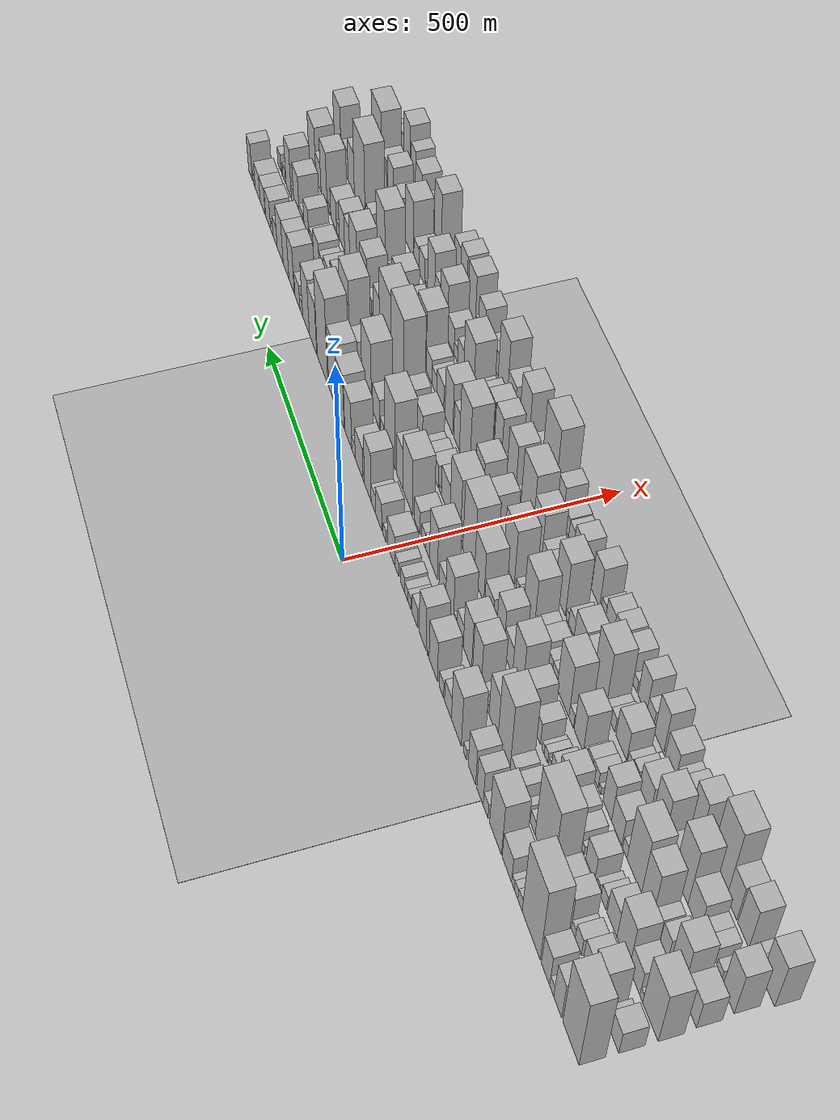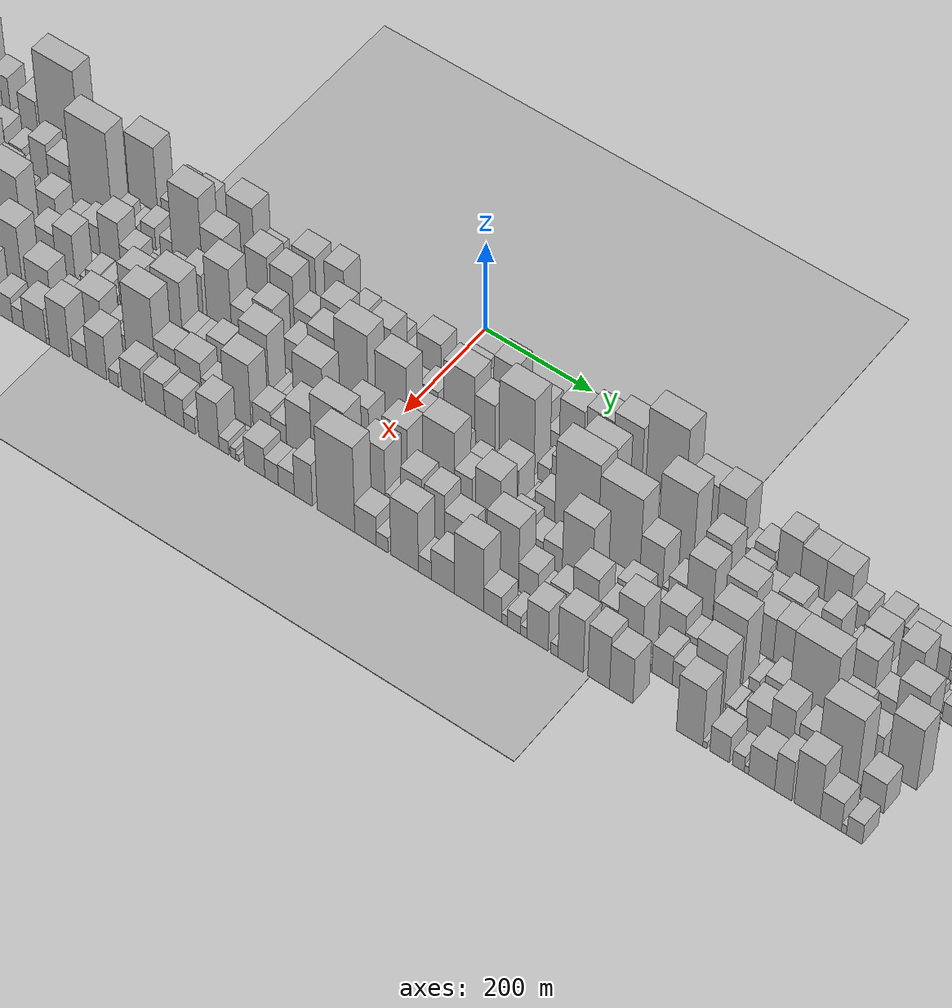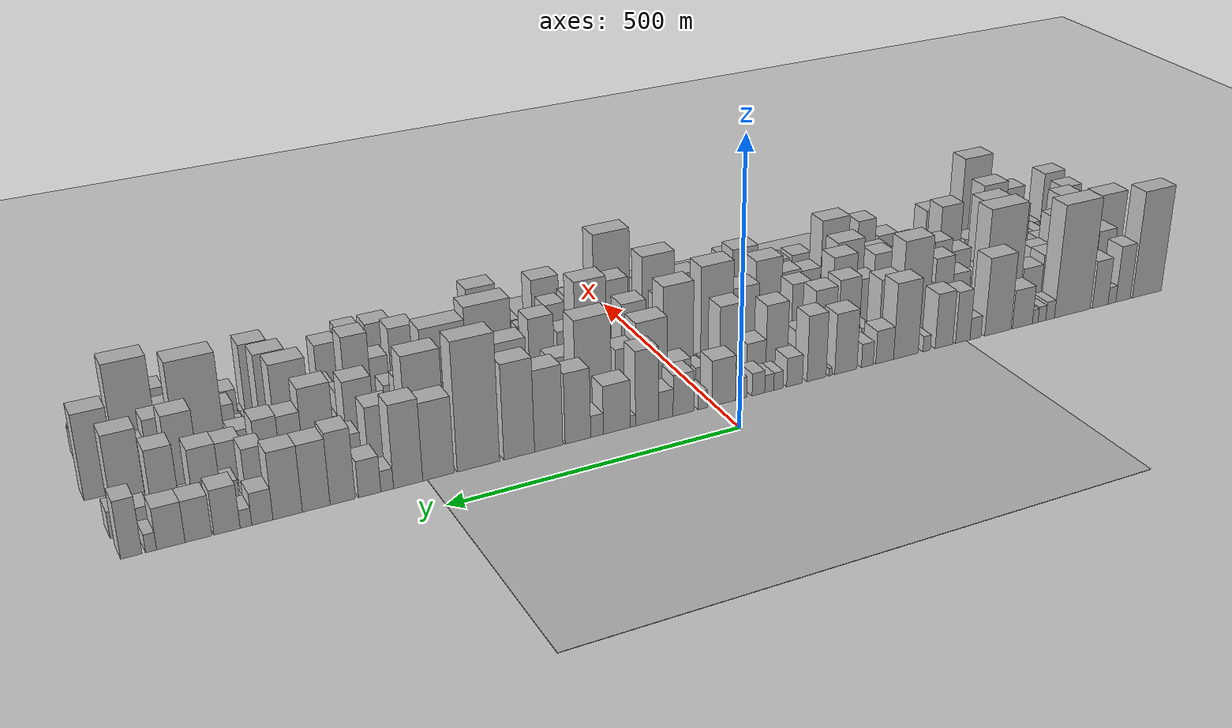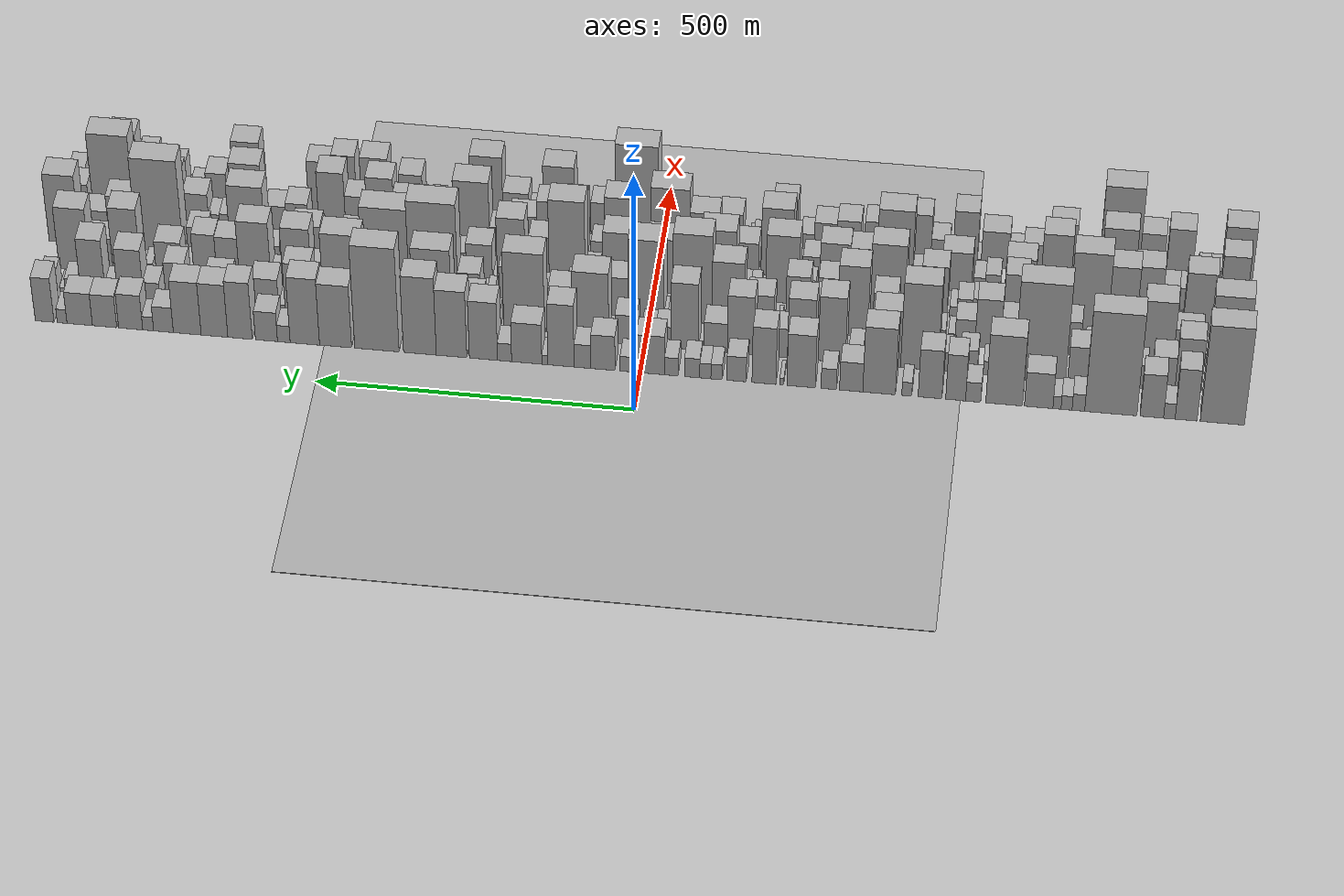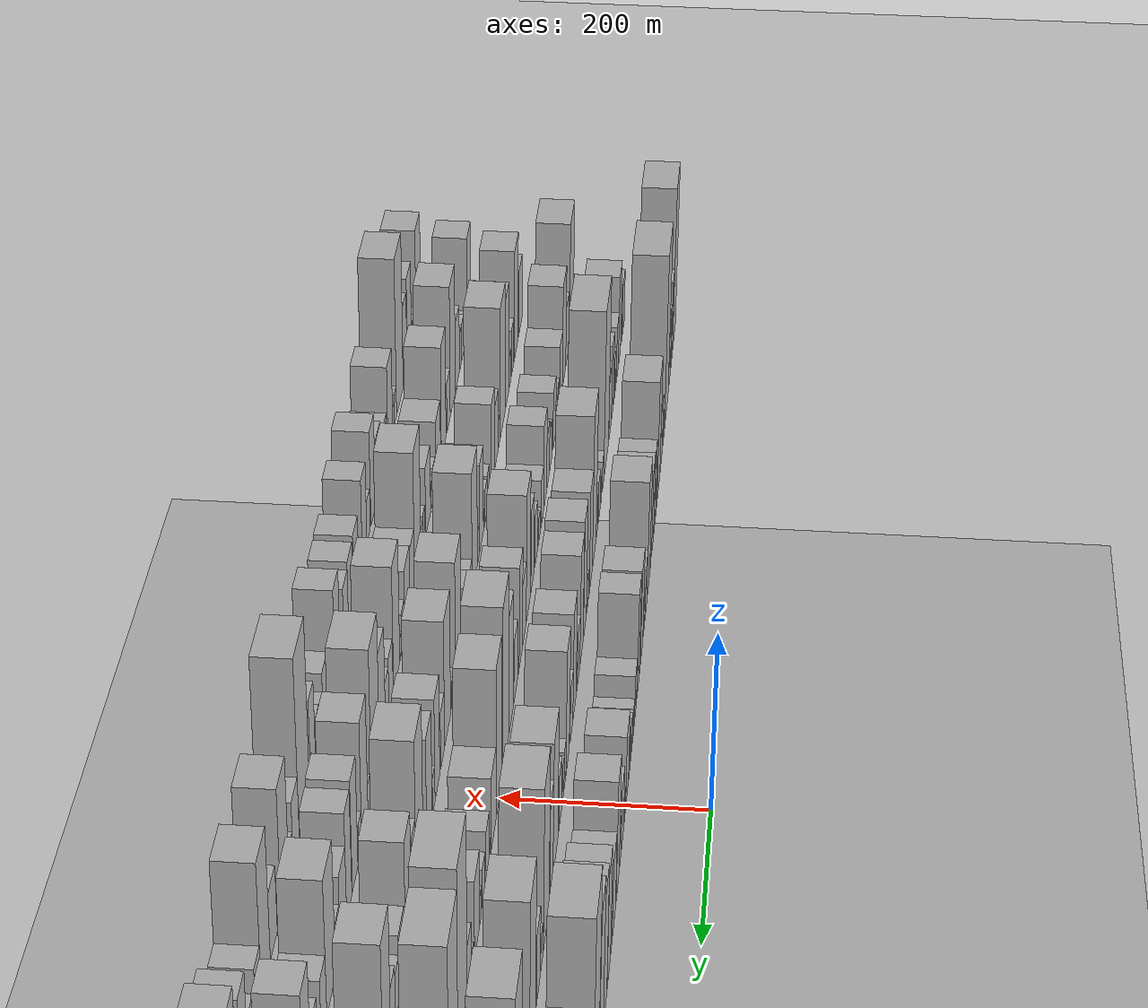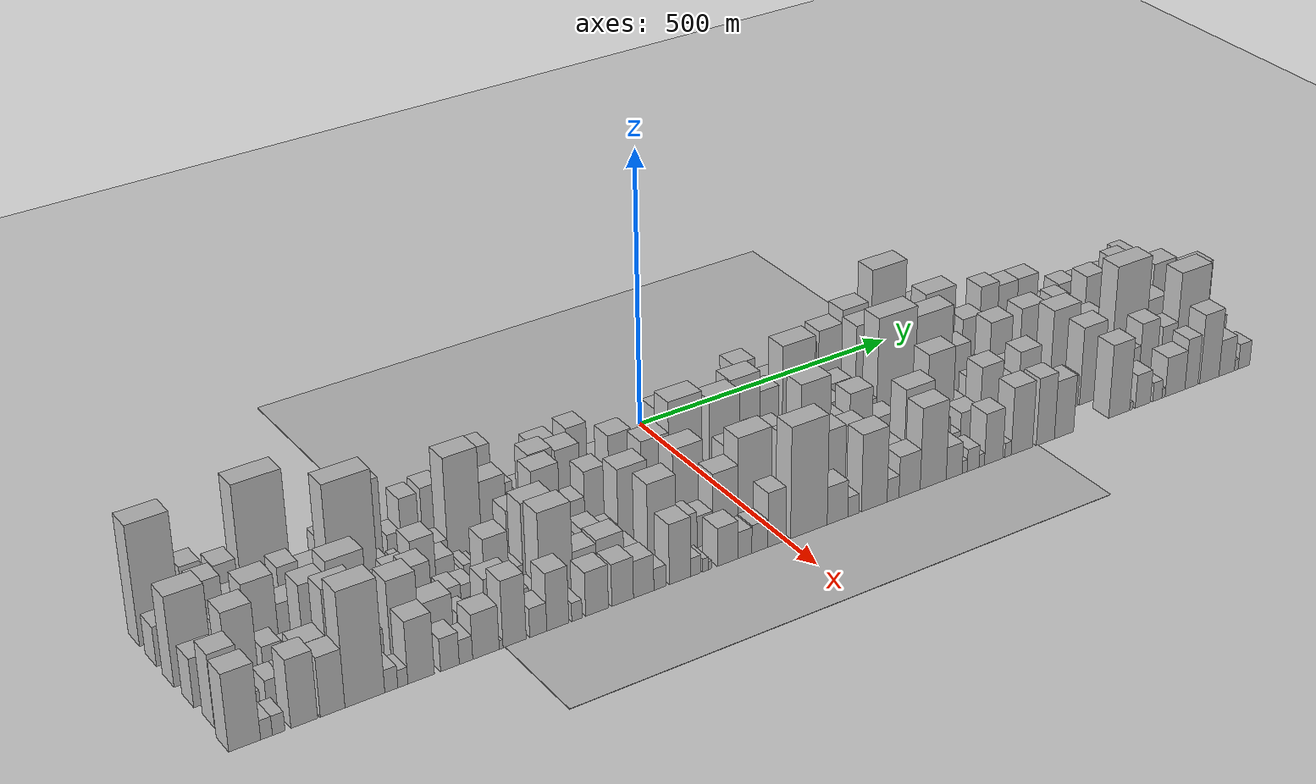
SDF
<?xml version="1.0" encoding="utf-8"?>

<sdf version="1.6">

   <world name="default">

      <gui fullscreen="0">

         <camera name="user_camera">

            <pose>-15 0 4.57585 0 0 0</pose>

            <view_controller>orbit</view_controller>

         </camera>

      </gui>

      <scene>

         <sky>

           <clouds>

             <speed>12</speed>

           </clouds>

         </sky>

         <ambient>0.4 0.4 0.4 1</ambient>

         <background>0.7 0.7 0.7 1</background>

         <shadows>1</shadows>

      </scene>

      <gravity>0 0 -9.8066</gravity>

      <magnetic_field>6e-06 2.3e-05 -4.2e-05</magnetic_field>

      <physics default="0" name="default_physics" type="ode">

         <ode>

            <solver>

               <type>quick</type>

               <iters>10</iters>

               <sor>1.0</sor>

               <use_dynamic_moi_rescaling>0</use_dynamic_moi_rescaling>

            </solver>

            <constraints>

               <cfm>0</cfm>

               <erp>0.2</erp>

               <contact_max_correcting_vel>100</contact_max_correcting_vel>

               <contact_surface_layer>0.001</contact_surface_layer>

            </constraints>

         </ode>

         <max_step_size>0.004</max_step_size>

         <real_time_factor>1</real_time_factor>

         <real_time_update_rate>250</real_time_update_rate>

      </physics>

      <light name="sun" type="directional">

         <cast_shadows>1</cast_shadows>

         <pose>0 0 10 0 0 0</pose>

         <diffuse>0.8 0.8 0.8 1</diffuse>

         <specular>0.2 0.2 0.2 1</specular>

         <attenuation>

            <range>1000</range>

            <constant>0.9</constant>

            <linear>0.01</linear>

            <quadratic>0.001</quadratic>

         </attenuation>

         <direction>-0.5 0.1 -0.9</direction>

      </light>

      <include>

         <name>ground_plane_1</name>

         <uri>model://HANNAS_ground_plane</uri>

         <pose>0 0 0  0 0 0</pose>

      </include>

      <include>

         <name>ground_plane_2</name>

         <uri>model://HANNAS_ground_plane</uri>

         <pose>100 0 0  0 0 0</pose>

      </include>

      <model name="building_1">

         <static>1</static>

         <pose frame="">100.0000 -905.9487 0 0.000000 0.000000 0.000000</pose>

         <link name="link">

            <pose frame="">0 0 105.00 0 0 0</pose>

            <collision name="collision">

               <geometry>

                  <box>

                     <size>40.0000 68.1026 210.0000</size>

                  </box>

               </geometry>

               <max_contacts>10</max_contacts>

               <surface>

                  <contact>

                     <ode/>

                  </contact>

                  <bounce/>

                  <friction>

                     <torsional>

                        <ode/>

                     </torsional>

                     <ode/>

                  </friction>

               </surface>

            </collision>

            <visual name="visual">

               <cast_shadows>0</cast_shadows>

               <geometry>

                  <box>

                     <size>40.0000 68.1026 210.0000</size>

                  </box>

               </geometry>

               <material>

                  <script>

                     <uri>model://HANNAS_wall/materials/scripts</uri>

                     <uri>model://HANNAS_wall/materials/textures</uri>

                     <name>vrc/HANNAS_wall</name>

                  </script>

               </material>

            </visual>

            <self_collide>0</self_collide>

            <enable_wind>0</enable_wind>

            <kinematic>0</kinematic>

         </link>

      </model>

      <model name="building_2">

         <static>1</static>

         <pose frame="">100.0000 -850.0106 0 0.000000 0.000000 0.000000</pose>

         <link name="link">

            <pose frame="">0 0 55.50 0 0 0</pose>

            <collision name="collision">

               <geometry>

                  <box>

                     <size>40.0000 33.7737 111.0000</size>

                  </box>

               </geometry>

               <max_contacts>10</max_contacts>

               <surface>

                  <contact>

                     <ode/>

                  </contact>

                  <bounce/>

                  <friction>

                     <torsional>

                        <ode/>

                     </torsional>

                     <ode/>

                  </friction>

               </surface>

            </collision>

            <visual name="visual">

               <cast_shadows>0</cast_shadows>

               <geometry>

                  <box>

                     <size>40.0000 33.7737 111.0000</size>

                  </box>

               </geometry>

               <material>

                  <script>

                     <uri>model://HANNAS_wall/materials/scripts</uri>

                     <uri>model://HANNAS_wall/materials/textures</uri>

                     <name>vrc/HANNAS_wall</name>

                  </script>

               </material>

            </visual>

            <self_collide>0</self_collide>

            <enable_wind>0</enable_wind>

            <kinematic>0</kinematic>

         </link>

      </model>

      <model name="building_3">

         <static>1</static>

         <pose frame="">100.0000 -824.1714 0 0.000000 0.000000 0.000000</pose>

         <link name="link">

            <pose frame="">0 0 16.50 0 0 0</pose>

            <collision name="collision">

               <geometry>

                  <box>

                     <size>40.0000 17.9045 33.0000</size>

                  </box>

               </geometry>

               <max_contacts>10</max_contacts>

               <surface>

                  <contact>

                     <ode/>

                  </contact>

                  <bounce/>

                  <friction>

                     <torsional>

                        <ode/>

                     </torsional>

                     <ode/>

                  </friction>

               </surface>

            </collision>

            <visual name="visual">

               <cast_shadows>0</cast_shadows>

               <geometry>

                  <box>

                     <size>40.0000 17.9045 33.0000</size>

                  </box>

               </geometry>

               <material>

                  <script>

                     <uri>model://HANNAS_wall/materials/scripts</uri>

                     <uri>model://HANNAS_wall/materials/textures</uri>

                     <name>vrc/HANNAS_wall</name>

                  </script>

               </material>

            </visual>

            <self_collide>0</self_collide>

            <enable_wind>0</enable_wind>

            <kinematic>0</kinematic>

         </link>

      </model>

      <model name="building_4">

         <static>1</static>

         <pose frame="">100.0000 -797.0768 0 0.000000 0.000000 0.000000</pose>

         <link name="link">

            <pose frame="">0 0 46.50 0 0 0</pose>

            <collision name="collision">

               <geometry>

                  <box>

                     <size>40.0000 36.2848 93.0000</size>

                  </box>

               </geometry>

               <max_contacts>10</max_contacts>

               <surface>

                  <contact>

                     <ode/>

                  </contact>

                  <bounce/>

                  <friction>

                     <torsional>

                        <ode/>

                     </torsional>

                     <ode/>

                  </friction>

               </surface>

            </collision>

            <visual name="visual">

               <cast_shadows>0</cast_shadows>

               <geometry>

                  <box>

                     <size>40.0000 36.2848 93.0000</size>

                  </box>

               </geometry>

               <material>

                  <script>

                     <uri>model://HANNAS_wall/materials/scripts</uri>

                     <uri>model://HANNAS_wall/materials/textures</uri>

                     <name>vrc/HANNAS_wall</name>

                  </script>

               </material>

            </visual>

            <self_collide>0</self_collide>

            <enable_wind>0</enable_wind>

            <kinematic>0</kinematic>

         </link>

      </model>

      <model name="building_5">

         <static>1</static>

         <pose frame="">100.0000 -733.5648 0 0.000000 0.000000 0.000000</pose>

         <link name="link">

            <pose frame="">0 0 109.50 0 0 0</pose>

            <collision name="collision">

               <geometry>

                  <box>

                     <size>40.0000 80.7393 219.0000</size>

                  </box>

               </geometry>

               <max_contacts>10</max_contacts>

               <surface>

                  <contact>

                     <ode/>

                  </contact>

                  <bounce/>

                  <friction>

                     <torsional>

                        <ode/>

                     </torsional>

                     <ode/>

                  </friction>

               </surface>

            </collision>

            <visual name="visual">

               <cast_shadows>0</cast_shadows>

               <geometry>

                  <box>

                     <size>40.0000 80.7393 219.0000</size>

                  </box>

               </geometry>

               <material>

                  <script>

                     <uri>model://HANNAS_wall/materials/scripts</uri>

                     <uri>model://HANNAS_wall/materials/textures</uri>

                     <name>vrc/HANNAS_wall</name>

                  </script>

               </material>

            </visual>

            <self_collide>0</self_collide>

            <enable_wind>0</enable_wind>

            <kinematic>0</kinematic>

         </link>

      </model>

      <model name="building_6">

         <static>1</static>

         <pose frame="">100.0000 -683.4348 0 0.000000 0.000000 0.000000</pose>

         <link name="link">

            <pose frame="">0 0 18.00 0 0 0</pose>

            <collision name="collision">

               <geometry>

                  <box>

                     <size>40.0000 19.5208 36.0000</size>

                  </box>

               </geometry>

               <max_contacts>10</max_contacts>

               <surface>

                  <contact>

                     <ode/>

                  </contact>

                  <bounce/>

                  <friction>

                     <torsional>

                        <ode/>

                     </torsional>

                     <ode/>

                  </friction>

               </surface>

            </collision>

            <visual name="visual">

               <cast_shadows>0</cast_shadows>

               <geometry>

                  <box>

                     <size>40.0000 19.5208 36.0000</size>

                  </box>

               </geometry>

               <material>

                  <script>

                     <uri>model://HANNAS_wall/materials/scripts</uri>

                     <uri>model://HANNAS_wall/materials/textures</uri>

                     <name>vrc/HANNAS_wall</name>

                  </script>

               </material>

            </visual>

            <self_collide>0</self_collide>

            <enable_wind>0</enable_wind>

            <kinematic>0</kinematic>

         </link>

      </model>

      <model name="building_7">

         <static>1</static>

         <pose frame="">100.0000 -665.0878 0 0.000000 0.000000 0.000000</pose>

         <link name="link">

            <pose frame="">0 0 15.00 0 0 0</pose>

            <collision name="collision">

               <geometry>

                  <box>

                     <size>40.0000 17.1732 30.0000</size>

                  </box>

               </geometry>

               <max_contacts>10</max_contacts>

               <surface>

                  <contact>

                     <ode/>

                  </contact>

                  <bounce/>

                  <friction>

                     <torsional>

                        <ode/>

                     </torsional>

                     <ode/>

                  </friction>

               </surface>

            </collision>

            <visual name="visual">

               <cast_shadows>0</cast_shadows>

               <geometry>

                  <box>

                     <size>40.0000 17.1732 30.0000</size>

                  </box>

               </geometry>

               <material>

                  <script>

                     <uri>model://HANNAS_wall/materials/scripts</uri>

                     <uri>model://HANNAS_wall/materials/textures</uri>

                     <name>vrc/HANNAS_wall</name>

                  </script>

               </material>

            </visual>

            <self_collide>0</self_collide>

            <enable_wind>0</enable_wind>

            <kinematic>0</kinematic>

         </link>

      </model>

      <model name="building_8">

         <static>1</static>

         <pose frame="">100.0000 -650.2125 0 0.000000 0.000000 0.000000</pose>

         <link name="link">

            <pose frame="">0 0 13.50 0 0 0</pose>

            <collision name="collision">

               <geometry>

                  <box>

                     <size>40.0000 12.5774 27.0000</size>

                  </box>

               </geometry>

               <max_contacts>10</max_contacts>

               <surface>

                  <contact>

                     <ode/>

                  </contact>

                  <bounce/>

                  <friction>

                     <torsional>

                        <ode/>

                     </torsional>

                     <ode/>

                  </friction>

               </surface>

            </collision>

            <visual name="visual">

               <cast_shadows>0</cast_shadows>

               <geometry>

                  <box>

                     <size>40.0000 12.5774 27.0000</size>

                  </box>

               </geometry>

               <material>

                  <script>

                     <uri>model://HANNAS_wall/materials/scripts</uri>

                     <uri>model://HANNAS_wall/materials/textures</uri>

                     <name>vrc/HANNAS_wall</name>

                  </script>

               </material>

            </visual>

            <self_collide>0</self_collide>

            <enable_wind>0</enable_wind>

            <kinematic>0</kinematic>

         </link>

      </model>

      <model name="building_9">

         <static>1</static>

         <pose frame="">100.0000 -621.8262 0 0.000000 0.000000 0.000000</pose>

         <link name="link">

            <pose frame="">0 0 37.50 0 0 0</pose>

            <collision name="collision">

               <geometry>

                  <box>

                     <size>40.0000 44.1953 75.0000</size>

                  </box>

               </geometry>

               <max_contacts>10</max_contacts>

               <surface>

                  <contact>

                     <ode/>

                  </contact>

                  <bounce/>

                  <friction>

                     <torsional>

                        <ode/>

                     </torsional>

                     <ode/>

                  </friction>

               </surface>

            </collision>

            <visual name="visual">

               <cast_shadows>0</cast_shadows>

               <geometry>

                  <box>

                     <size>40.0000 44.1953 75.0000</size>

                  </box>

               </geometry>

               <material>

                  <script>

                     <uri>model://HANNAS_wall/materials/scripts</uri>

                     <uri>model://HANNAS_wall/materials/textures</uri>

                     <name>vrc/HANNAS_wall</name>

                  </script>

               </material>

            </visual>

            <self_collide>0</self_collide>

            <enable_wind>0</enable_wind>

            <kinematic>0</kinematic>

         </link>

      </model>

      <model name="building_10">

         <static>1</static>

         <pose frame="">100.0000 -568.2450 0 0.000000 0.000000 0.000000</pose>

         <link name="link">

            <pose frame="">0 0 75.00 0 0 0</pose>

            <collision name="collision">

               <geometry>

                  <box>

                     <size>40.0000 56.9672 150.0000</size>

                  </box>

               </geometry>

               <max_contacts>10</max_contacts>

               <surface>

                  <contact>

                     <ode/>

                  </contact>

                  <bounce/>

                  <friction>

                     <torsional>

                        <ode/>

                     </torsional>

                     <ode/>

                  </friction>

               </surface>

            </collision>

            <visual name="visual">

               <cast_shadows>0</cast_shadows>

               <geometry>

                  <box>

                     <size>40.0000 56.9672 150.0000</size>

                  </box>

               </geometry>

               <material>

                  <script>

                     <uri>model://HANNAS_wall/materials/scripts</uri>

                     <uri>model://HANNAS_wall/materials/textures</uri>

                     <name>vrc/HANNAS_wall</name>

                  </script>

               </material>

            </visual>

            <self_collide>0</self_collide>

            <enable_wind>0</enable_wind>

            <kinematic>0</kinematic>

         </link>

      </model>

      <model name="building_11">

         <static>1</static>

         <pose frame="">100.0000 -520.0015 0 0.000000 0.000000 0.000000</pose>

         <link name="link">

            <pose frame="">0 0 21.00 0 0 0</pose>

            <collision name="collision">

               <geometry>

                  <box>

                     <size>40.0000 23.5197 42.0000</size>

                  </box>

               </geometry>

               <max_contacts>10</max_contacts>

               <surface>

                  <contact>

                     <ode/>

                  </contact>

                  <bounce/>

                  <friction>

                     <torsional>

                        <ode/>

                     </torsional>

                     <ode/>

                  </friction>

               </surface>

            </collision>

            <visual name="visual">

               <cast_shadows>0</cast_shadows>

               <geometry>

                  <box>

                     <size>40.0000 23.5197 42.0000</size>

                  </box>

               </geometry>

               <material>

                  <script>

                     <uri>model://HANNAS_wall/materials/scripts</uri>

                     <uri>model://HANNAS_wall/materials/textures</uri>

                     <name>vrc/HANNAS_wall</name>

                  </script>

               </material>

            </visual>

            <self_collide>0</self_collide>

            <enable_wind>0</enable_wind>

            <kinematic>0</kinematic>

         </link>

      </model>

      <model name="building_12">

         <static>1</static>

         <pose frame="">100.0000 -492.8149 0 0.000000 0.000000 0.000000</pose>

         <link name="link">

            <pose frame="">0 0 49.50 0 0 0</pose>

            <collision name="collision">

               <geometry>

                  <box>

                     <size>40.0000 30.8535 99.0000</size>

                  </box>

               </geometry>

               <max_contacts>10</max_contacts>

               <surface>

                  <contact>

                     <ode/>

                  </contact>

                  <bounce/>

                  <friction>

                     <torsional>

                        <ode/>

                     </torsional>

                     <ode/>

                  </friction>

               </surface>

            </collision>

            <visual name="visual">

               <cast_shadows>0</cast_shadows>

               <geometry>

                  <box>

                     <size>40.0000 30.8535 99.0000</size>

                  </box>

               </geometry>

               <material>

                  <script>

                     <uri>model://HANNAS_wall/materials/scripts</uri>

                     <uri>model://HANNAS_wall/materials/textures</uri>

                     <name>vrc/HANNAS_wall</name>

                  </script>

               </material>

            </visual>

            <self_collide>0</self_collide>

            <enable_wind>0</enable_wind>

            <kinematic>0</kinematic>

         </link>

      </model>

      <model name="building_13">

         <static>1</static>

         <pose frame="">100.0000 -452.9335 0 0.000000 0.000000 0.000000</pose>

         <link name="link">

            <pose frame="">0 0 52.50 0 0 0</pose>

            <collision name="collision">

               <geometry>

                  <box>

                     <size>40.0000 36.9093 105.0000</size>

                  </box>

               </geometry>

               <max_contacts>10</max_contacts>

               <surface>

                  <contact>

                     <ode/>

                  </contact>

                  <bounce/>

                  <friction>

                     <torsional>

                        <ode/>

                     </torsional>

                     <ode/>

                  </friction>

               </surface>

            </collision>

            <visual name="visual">

               <cast_shadows>0</cast_shadows>

               <geometry>

                  <box>

                     <size>40.0000 36.9093 105.0000</size>

                  </box>

               </geometry>

               <material>

                  <script>

                     <uri>model://HANNAS_wall/materials/scripts</uri>

                     <uri>model://HANNAS_wall/materials/textures</uri>

                     <name>vrc/HANNAS_wall</name>

                  </script>

               </material>

            </visual>

            <self_collide>0</self_collide>

            <enable_wind>0</enable_wind>

            <kinematic>0</kinematic>

         </link>

      </model>

      <model name="building_14">

         <static>1</static>

         <pose frame="">100.0000 -416.7307 0 0.000000 0.000000 0.000000</pose>

         <link name="link">

            <pose frame="">0 0 15.00 0 0 0</pose>

            <collision name="collision">

               <geometry>

                  <box>

                     <size>40.0000 15.4963 30.0000</size>

                  </box>

               </geometry>

               <max_contacts>10</max_contacts>

               <surface>

                  <contact>

                     <ode/>

                  </contact>

                  <bounce/>

                  <friction>

                     <torsional>

                        <ode/>

                     </torsional>

                     <ode/>

                  </friction>

               </surface>

            </collision>

            <visual name="visual">

               <cast_shadows>0</cast_shadows>

               <geometry>

                  <box>

                     <size>40.0000 15.4963 30.0000</size>

                  </box>

               </geometry>

               <material>

                  <script>

                     <uri>model://HANNAS_wall/materials/scripts</uri>

                     <uri>model://HANNAS_wall/materials/textures</uri>

                     <name>vrc/HANNAS_wall</name>

                  </script>

               </material>

            </visual>

            <self_collide>0</self_collide>

            <enable_wind>0</enable_wind>

            <kinematic>0</kinematic>

         </link>

      </model>

      <model name="building_15">

         <static>1</static>

         <pose frame="">100.0000 -373.5978 0 0.000000 0.000000 0.000000</pose>

         <link name="link">

            <pose frame="">0 0 72.00 0 0 0</pose>

            <collision name="collision">

               <geometry>

                  <box>

                     <size>40.0000 50.7695 144.0000</size>

                  </box>

               </geometry>

               <max_contacts>10</max_contacts>

               <surface>

                  <contact>

                     <ode/>

                  </contact>

                  <bounce/>

                  <friction>

                     <torsional>

                        <ode/>

                     </torsional>

                     <ode/>

                  </friction>

               </surface>

            </collision>

            <visual name="visual">

               <cast_shadows>0</cast_shadows>

               <geometry>

                  <box>

                     <size>40.0000 50.7695 144.0000</size>

                  </box>

               </geometry>

               <material>

                  <script>

                     <uri>model://HANNAS_wall/materials/scripts</uri>

                     <uri>model://HANNAS_wall/materials/textures</uri>

                     <name>vrc/HANNAS_wall</name>

                  </script>

               </material>

            </visual>

            <self_collide>0</self_collide>

            <enable_wind>0</enable_wind>

            <kinematic>0</kinematic>

         </link>

      </model>

      <model name="building_16">

         <static>1</static>

         <pose frame="">100.0000 -330.0383 0 0.000000 0.000000 0.000000</pose>

         <link name="link">

            <pose frame="">0 0 31.50 0 0 0</pose>

            <collision name="collision">

               <geometry>

                  <box>

                     <size>40.0000 36.3495 63.0000</size>

                  </box>

               </geometry>

               <max_contacts>10</max_contacts>

               <surface>

                  <contact>

                     <ode/>

                  </contact>

                  <bounce/>

                  <friction>

                     <torsional>

                        <ode/>

                     </torsional>

                     <ode/>

                  </friction>

               </surface>

            </collision>

            <visual name="visual">

               <cast_shadows>0</cast_shadows>

               <geometry>

                  <box>

                     <size>40.0000 36.3495 63.0000</size>

                  </box>

               </geometry>

               <material>

                  <script>

                     <uri>model://HANNAS_wall/materials/scripts</uri>

                     <uri>model://HANNAS_wall/materials/textures</uri>

                     <name>vrc/HANNAS_wall</name>

                  </script>

               </material>

            </visual>

            <self_collide>0</self_collide>

            <enable_wind>0</enable_wind>

            <kinematic>0</kinematic>

         </link>

      </model>

      <model name="building_17">

         <static>1</static>

         <pose frame="">100.0000 -294.9003 0 0.000000 0.000000 0.000000</pose>

         <link name="link">

            <pose frame="">0 0 22.50 0 0 0</pose>

            <collision name="collision">

               <geometry>

                  <box>

                     <size>40.0000 23.9264 45.0000</size>

                  </box>

               </geometry>

               <max_contacts>10</max_contacts>

               <surface>

                  <contact>

                     <ode/>

                  </contact>

                  <bounce/>

                  <friction>

                     <torsional>

                        <ode/>

                     </torsional>

                     <ode/>

                  </friction>

               </surface>

            </collision>

            <visual name="visual">

               <cast_shadows>0</cast_shadows>

               <geometry>

                  <box>

                     <size>40.0000 23.9264 45.0000</size>

                  </box>

               </geometry>

               <material>

                  <script>

                     <uri>model://HANNAS_wall/materials/scripts</uri>

                     <uri>model://HANNAS_wall/materials/textures</uri>

                     <name>vrc/HANNAS_wall</name>

                  </script>

               </material>

            </visual>

            <self_collide>0</self_collide>

            <enable_wind>0</enable_wind>

            <kinematic>0</kinematic>

         </link>

      </model>

      <model name="building_18">

         <static>1</static>

         <pose frame="">100.0000 -251.7441 0 0.000000 0.000000 0.000000</pose>

         <link name="link">

            <pose frame="">0 0 57.00 0 0 0</pose>

            <collision name="collision">

               <geometry>

                  <box>

                     <size>40.0000 44.3859 114.0000</size>

                  </box>

               </geometry>

               <max_contacts>10</max_contacts>

               <surface>

                  <contact>

                     <ode/>

                  </contact>

                  <bounce/>

                  <friction>

                     <torsional>

                        <ode/>

                     </torsional>

                     <ode/>

                  </friction>

               </surface>

            </collision>

            <visual name="visual">

               <cast_shadows>0</cast_shadows>

               <geometry>

                  <box>

                     <size>40.0000 44.3859 114.0000</size>

                  </box>

               </geometry>

               <material>

                  <script>

                     <uri>model://HANNAS_wall/materials/scripts</uri>

                     <uri>model://HANNAS_wall/materials/textures</uri>

                     <name>vrc/HANNAS_wall</name>

                  </script>

               </material>

            </visual>

            <self_collide>0</self_collide>

            <enable_wind>0</enable_wind>

            <kinematic>0</kinematic>

         </link>

      </model>

      <model name="building_19">

         <static>1</static>

         <pose frame="">100.0000 -221.4187 0 0.000000 0.000000 0.000000</pose>

         <link name="link">

            <pose frame="">0 0 7.50 0 0 0</pose>

            <collision name="collision">

               <geometry>

                  <box>

                     <size>40.0000 6.2650 15.0000</size>

                  </box>

               </geometry>

               <max_contacts>10</max_contacts>

               <surface>

                  <contact>

                     <ode/>

                  </contact>

                  <bounce/>

                  <friction>

                     <torsional>

                        <ode/>

                     </torsional>

                     <ode/>

                  </friction>

               </surface>

            </collision>

            <visual name="visual">

               <cast_shadows>0</cast_shadows>

               <geometry>

                  <box>

                     <size>40.0000 6.2650 15.0000</size>

                  </box>

               </geometry>

               <material>

                  <script>

                     <uri>model://HANNAS_wall/materials/scripts</uri>

                     <uri>model://HANNAS_wall/materials/textures</uri>

                     <name>vrc/HANNAS_wall</name>

                  </script>

               </material>

            </visual>

            <self_collide>0</self_collide>

            <enable_wind>0</enable_wind>

            <kinematic>0</kinematic>

         </link>

      </model>

      <model name="building_20">

         <static>1</static>

         <pose frame="">100.0000 -193.5699 0 0.000000 0.000000 0.000000</pose>

         <link name="link">

            <pose frame="">0 0 61.50 0 0 0</pose>

            <collision name="collision">

               <geometry>

                  <box>

                     <size>40.0000 37.4325 123.0000</size>

                  </box>

               </geometry>

               <max_contacts>10</max_contacts>

               <surface>

                  <contact>

                     <ode/>

                  </contact>

                  <bounce/>

                  <friction>

                     <torsional>

                        <ode/>

                     </torsional>

                     <ode/>

                  </friction>

               </surface>

            </collision>

            <visual name="visual">

               <cast_shadows>0</cast_shadows>

               <geometry>

                  <box>

                     <size>40.0000 37.4325 123.0000</size>

                  </box>

               </geometry>

               <material>

                  <script>

                     <uri>model://HANNAS_wall/materials/scripts</uri>

                     <uri>model://HANNAS_wall/materials/textures</uri>

                     <name>vrc/HANNAS_wall</name>

                  </script>

               </material>

            </visual>

            <self_collide>0</self_collide>

            <enable_wind>0</enable_wind>

            <kinematic>0</kinematic>

         </link>

      </model>

      <model name="building_21">

         <static>1</static>

         <pose frame="">100.0000 -150.5944 0 0.000000 0.000000 0.000000</pose>

         <link name="link">

            <pose frame="">0 0 27.00 0 0 0</pose>

            <collision name="collision">

               <geometry>

                  <box>

                     <size>40.0000 30.5184 54.0000</size>

                  </box>

               </geometry>

               <max_contacts>10</max_contacts>

               <surface>

                  <contact>

                     <ode/>

                  </contact>

                  <bounce/>

                  <friction>

                     <torsional>

                        <ode/>

                     </torsional>

                     <ode/>

                  </friction>

               </surface>

            </collision>

            <visual name="visual">

               <cast_shadows>0</cast_shadows>

               <geometry>

                  <box>

                     <size>40.0000 30.5184 54.0000</size>

                  </box>

               </geometry>

               <material>

                  <script>

                     <uri>model://HANNAS_wall/materials/scripts</uri>

                     <uri>model://HANNAS_wall/materials/textures</uri>

                     <name>vrc/HANNAS_wall</name>

                  </script>

               </material>

            </visual>

            <self_collide>0</self_collide>

            <enable_wind>0</enable_wind>

            <kinematic>0</kinematic>

         </link>

      </model>

      <model name="building_22">

         <static>1</static>

         <pose frame="">100.0000 -119.3798 0 0.000000 0.000000 0.000000</pose>

         <link name="link">

            <pose frame="">0 0 16.50 0 0 0</pose>

            <collision name="collision">

               <geometry>

                  <box>

                     <size>40.0000 17.9109 33.0000</size>

                  </box>

               </geometry>

               <max_contacts>10</max_contacts>

               <surface>

                  <contact>

                     <ode/>

                  </contact>

                  <bounce/>

                  <friction>

                     <torsional>

                        <ode/>

                     </torsional>

                     <ode/>

                  </friction>

               </surface>

            </collision>

            <visual name="visual">

               <cast_shadows>0</cast_shadows>

               <geometry>

                  <box>

                     <size>40.0000 17.9109 33.0000</size>

                  </box>

               </geometry>

               <material>

                  <script>

                     <uri>model://HANNAS_wall/materials/scripts</uri>

                     <uri>model://HANNAS_wall/materials/textures</uri>

                     <name>vrc/HANNAS_wall</name>

                  </script>

               </material>

            </visual>

            <self_collide>0</self_collide>

            <enable_wind>0</enable_wind>

            <kinematic>0</kinematic>

         </link>

      </model>

      <model name="building_23">

         <static>1</static>

         <pose frame="">100.0000 -101.7180 0 0.000000 0.000000 0.000000</pose>

         <link name="link">

            <pose frame="">0 0 16.50 0 0 0</pose>

            <collision name="collision">

               <geometry>

                  <box>

                     <size>40.0000 17.4126 33.0000</size>

                  </box>

               </geometry>

               <max_contacts>10</max_contacts>

               <surface>

                  <contact>

                     <ode/>

                  </contact>

                  <bounce/>

                  <friction>

                     <torsional>

                        <ode/>

                     </torsional>

                     <ode/>

                  </friction>

               </surface>

            </collision>

            <visual name="visual">

               <cast_shadows>0</cast_shadows>

               <geometry>

                  <box>

                     <size>40.0000 17.4126 33.0000</size>

                  </box>

               </geometry>

               <material>

                  <script>

                     <uri>model://HANNAS_wall/materials/scripts</uri>

                     <uri>model://HANNAS_wall/materials/textures</uri>

                     <name>vrc/HANNAS_wall</name>

                  </script>

               </material>

            </visual>

            <self_collide>0</self_collide>

            <enable_wind>0</enable_wind>

            <kinematic>0</kinematic>

         </link>

      </model>

      <model name="building_24">

         <static>1</static>

         <pose frame="">100.0000 -80.9346 0 0.000000 0.000000 0.000000</pose>

         <link name="link">

            <pose frame="">0 0 21.00 0 0 0</pose>

            <collision name="collision">

               <geometry>

                  <box>

                     <size>40.0000 24.1541 42.0000</size>

                  </box>

               </geometry>

               <max_contacts>10</max_contacts>

               <surface>

                  <contact>

                     <ode/>

                  </contact>

                  <bounce/>

                  <friction>

                     <torsional>

                        <ode/>

                     </torsional>

                     <ode/>

                  </friction>

               </surface>

            </collision>

            <visual name="visual">

               <cast_shadows>0</cast_shadows>

               <geometry>

                  <box>

                     <size>40.0000 24.1541 42.0000</size>

                  </box>

               </geometry>

               <material>

                  <script>

                     <uri>model://HANNAS_wall/materials/scripts</uri>

                     <uri>model://HANNAS_wall/materials/textures</uri>

                     <name>vrc/HANNAS_wall</name>

                  </script>

               </material>

            </visual>

            <self_collide>0</self_collide>

            <enable_wind>0</enable_wind>

            <kinematic>0</kinematic>

         </link>

      </model>

      <model name="building_25">

         <static>1</static>

         <pose frame="">100.0000 -48.1983 0 0.000000 0.000000 0.000000</pose>

         <link name="link">

            <pose frame="">0 0 19.50 0 0 0</pose>

            <collision name="collision">

               <geometry>

                  <box>

                     <size>40.0000 21.3186 39.0000</size>

                  </box>

               </geometry>

               <max_contacts>10</max_contacts>

               <surface>

                  <contact>

                     <ode/>

                  </contact>

                  <bounce/>

                  <friction>

                     <torsional>

                        <ode/>

                     </torsional>

                     <ode/>

                  </friction>

               </surface>

            </collision>

            <visual name="visual">

               <cast_shadows>0</cast_shadows>

               <geometry>

                  <box>

                     <size>40.0000 21.3186 39.0000</size>

                  </box>

               </geometry>

               <material>

                  <script>

                     <uri>model://HANNAS_wall/materials/scripts</uri>

                     <uri>model://HANNAS_wall/materials/textures</uri>

                     <name>vrc/HANNAS_wall</name>

                  </script>

               </material>

            </visual>

            <self_collide>0</self_collide>

            <enable_wind>0</enable_wind>

            <kinematic>0</kinematic>

         </link>

      </model>

      <model name="building_26">

         <static>1</static>

         <pose frame="">100.0000 -15.3454 0 0.000000 0.000000 0.000000</pose>

         <link name="link">

            <pose frame="">0 0 42.00 0 0 0</pose>

            <collision name="collision">

               <geometry>

                  <box>

                     <size>40.0000 44.3872 84.0000</size>

                  </box>

               </geometry>

               <max_contacts>10</max_contacts>

               <surface>

                  <contact>

                     <ode/>

                  </contact>

                  <bounce/>

                  <friction>

                     <torsional>

                        <ode/>

                     </torsional>

                     <ode/>

                  </friction>

               </surface>

            </collision>

            <visual name="visual">

               <cast_shadows>0</cast_shadows>

               <geometry>

                  <box>

                     <size>40.0000 44.3872 84.0000</size>

                  </box>

               </geometry>

               <material>

                  <script>

                     <uri>model://HANNAS_wall/materials/scripts</uri>

                     <uri>model://HANNAS_wall/materials/textures</uri>

                     <name>vrc/HANNAS_wall</name>

                  </script>

               </material>

            </visual>

            <self_collide>0</self_collide>

            <enable_wind>0</enable_wind>

            <kinematic>0</kinematic>

         </link>

      </model>

      <model name="building_27">

         <static>1</static>

         <pose frame="">100.0000 23.5425 0 0.000000 0.000000 0.000000</pose>

         <link name="link">

            <pose frame="">0 0 16.50 0 0 0</pose>

            <collision name="collision">

               <geometry>

                  <box>

                     <size>40.0000 17.3886 33.0000</size>

                  </box>

               </geometry>

               <max_contacts>10</max_contacts>

               <surface>

                  <contact>

                     <ode/>

                  </contact>

                  <bounce/>

                  <friction>

                     <torsional>

                        <ode/>

                     </torsional>

                     <ode/>

                  </friction>

               </surface>

            </collision>

            <visual name="visual">

               <cast_shadows>0</cast_shadows>

               <geometry>

                  <box>

                     <size>40.0000 17.3886 33.0000</size>

                  </box>

               </geometry>

               <material>

                  <script>

                     <uri>model://HANNAS_wall/materials/scripts</uri>

                     <uri>model://HANNAS_wall/materials/textures</uri>

                     <name>vrc/HANNAS_wall</name>

                  </script>

               </material>

            </visual>

            <self_collide>0</self_collide>

            <enable_wind>0</enable_wind>

            <kinematic>0</kinematic>

         </link>

      </model>

      <model name="building_28">

         <static>1</static>

         <pose frame="">100.0000 59.1614 0 0.000000 0.000000 0.000000</pose>

         <link name="link">

            <pose frame="">0 0 37.50 0 0 0</pose>

            <collision name="collision">

               <geometry>

                  <box>

                     <size>40.0000 37.8491 75.0000</size>

                  </box>

               </geometry>

               <max_contacts>10</max_contacts>

               <surface>

                  <contact>

                     <ode/>

                  </contact>

                  <bounce/>

                  <friction>

                     <torsional>

                        <ode/>

                     </torsional>

                     <ode/>

                  </friction>

               </surface>

            </collision>

            <visual name="visual">

               <cast_shadows>0</cast_shadows>

               <geometry>

                  <box>

                     <size>40.0000 37.8491 75.0000</size>

                  </box>

               </geometry>

               <material>

                  <script>

                     <uri>model://HANNAS_wall/materials/scripts</uri>

                     <uri>model://HANNAS_wall/materials/textures</uri>

                     <name>vrc/HANNAS_wall</name>

                  </script>

               </material>

            </visual>

            <self_collide>0</self_collide>

            <enable_wind>0</enable_wind>

            <kinematic>0</kinematic>

         </link>

      </model>

      <model name="building_29">

         <static>1</static>

         <pose frame="">100.0000 91.3784 0 0.000000 0.000000 0.000000</pose>

         <link name="link">

            <pose frame="">0 0 25.50 0 0 0</pose>

            <collision name="collision">

               <geometry>

                  <box>

                     <size>40.0000 26.5849 51.0000</size>

                  </box>

               </geometry>

               <max_contacts>10</max_contacts>

               <surface>

                  <contact>

                     <ode/>

                  </contact>

                  <bounce/>

                  <friction>

                     <torsional>

                        <ode/>

                     </torsional>

                     <ode/>

                  </friction>

               </surface>

            </collision>

            <visual name="visual">

               <cast_shadows>0</cast_shadows>

               <geometry>

                  <box>

                     <size>40.0000 26.5849 51.0000</size>

                  </box>

               </geometry>

               <material>

                  <script>

                     <uri>model://HANNAS_wall/materials/scripts</uri>

                     <uri>model://HANNAS_wall/materials/textures</uri>

                     <name>vrc/HANNAS_wall</name>

                  </script>

               </material>

            </visual>

            <self_collide>0</self_collide>

            <enable_wind>0</enable_wind>

            <kinematic>0</kinematic>

         </link>

      </model>

      <model name="building_30">

         <static>1</static>

         <pose frame="">100.0000 125.3945 0 0.000000 0.000000 0.000000</pose>

         <link name="link">

            <pose frame="">0 0 67.50 0 0 0</pose>

            <collision name="collision">

               <geometry>

                  <box>

                     <size>40.0000 41.4472 135.0000</size>

                  </box>

               </geometry>

               <max_contacts>10</max_contacts>

               <surface>

                  <contact>

                     <ode/>

                  </contact>

                  <bounce/>

                  <friction>

                     <torsional>

                        <ode/>

                     </torsional>

                     <ode/>

                  </friction>

               </surface>

            </collision>

            <visual name="visual">

               <cast_shadows>0</cast_shadows>

               <geometry>

                  <box>

                     <size>40.0000 41.4472 135.0000</size>

                  </box>

               </geometry>

               <material>

                  <script>

                     <uri>model://HANNAS_wall/materials/scripts</uri>

                     <uri>model://HANNAS_wall/materials/textures</uri>

                     <name>vrc/HANNAS_wall</name>

                  </script>

               </material>

            </visual>

            <self_collide>0</self_collide>

            <enable_wind>0</enable_wind>

            <kinematic>0</kinematic>

         </link>

      </model>

      <model name="building_31">

         <static>1</static>

         <pose frame="">100.0000 150.7980 0 0.000000 0.000000 0.000000</pose>

         <link name="link">

            <pose frame="">0 0 10.50 0 0 0</pose>

            <collision name="collision">

               <geometry>

                  <box>

                     <size>40.0000 9.3599 21.0000</size>

                  </box>

               </geometry>

               <max_contacts>10</max_contacts>

               <surface>

                  <contact>

                     <ode/>

                  </contact>

                  <bounce/>

                  <friction>

                     <torsional>

                        <ode/>

                     </torsional>

                     <ode/>

                  </friction>

               </surface>

            </collision>

            <visual name="visual">

               <cast_shadows>0</cast_shadows>

               <geometry>

                  <box>

                     <size>40.0000 9.3599 21.0000</size>

                  </box>

               </geometry>

               <material>

                  <script>

                     <uri>model://HANNAS_wall/materials/scripts</uri>

                     <uri>model://HANNAS_wall/materials/textures</uri>

                     <name>vrc/HANNAS_wall</name>

                  </script>

               </material>

            </visual>

            <self_collide>0</self_collide>

            <enable_wind>0</enable_wind>

            <kinematic>0</kinematic>

         </link>

      </model>

      <model name="building_32">

         <static>1</static>

         <pose frame="">100.0000 179.3233 0 0.000000 0.000000 0.000000</pose>

         <link name="link">

            <pose frame="">0 0 43.50 0 0 0</pose>

            <collision name="collision">

               <geometry>

                  <box>

                     <size>40.0000 47.6907 87.0000</size>

                  </box>

               </geometry>

               <max_contacts>10</max_contacts>

               <surface>

                  <contact>

                     <ode/>

                  </contact>

                  <bounce/>

                  <friction>

                     <torsional>

                        <ode/>

                     </torsional>

                     <ode/>

                  </friction>

               </surface>

            </collision>

            <visual name="visual">

               <cast_shadows>0</cast_shadows>

               <geometry>

                  <box>

                     <size>40.0000 47.6907 87.0000</size>

                  </box>

               </geometry>

               <material>

                  <script>

                     <uri>model://HANNAS_wall/materials/scripts</uri>

                     <uri>model://HANNAS_wall/materials/textures</uri>

                     <name>vrc/HANNAS_wall</name>

                  </script>

               </material>

            </visual>

            <self_collide>0</self_collide>

            <enable_wind>0</enable_wind>

            <kinematic>0</kinematic>

         </link>

      </model>

      <model name="building_33">

         <static>1</static>

         <pose frame="">100.0000 214.2500 0 0.000000 0.000000 0.000000</pose>

         <link name="link">

            <pose frame="">0 0 19.50 0 0 0</pose>

            <collision name="collision">

               <geometry>

                  <box>

                     <size>40.0000 22.1627 39.0000</size>

                  </box>

               </geometry>

               <max_contacts>10</max_contacts>

               <surface>

                  <contact>

                     <ode/>

                  </contact>

                  <bounce/>

                  <friction>

                     <torsional>

                        <ode/>

                     </torsional>

                     <ode/>

                  </friction>

               </surface>

            </collision>

            <visual name="visual">

               <cast_shadows>0</cast_shadows>

               <geometry>

                  <box>

                     <size>40.0000 22.1627 39.0000</size>

                  </box>

               </geometry>

               <material>

                  <script>

                     <uri>model://HANNAS_wall/materials/scripts</uri>

                     <uri>model://HANNAS_wall/materials/textures</uri>

                     <name>vrc/HANNAS_wall</name>

                  </script>

               </material>

            </visual>

            <self_collide>0</self_collide>

            <enable_wind>0</enable_wind>

            <kinematic>0</kinematic>

         </link>

      </model>

      <model name="building_34">

         <static>1</static>

         <pose frame="">100.0000 247.6200 0 0.000000 0.000000 0.000000</pose>

         <link name="link">

            <pose frame="">0 0 63.00 0 0 0</pose>

            <collision name="collision">

               <geometry>

                  <box>

                     <size>40.0000 44.5773 126.0000</size>

                  </box>

               </geometry>

               <max_contacts>10</max_contacts>

               <surface>

                  <contact>

                     <ode/>

                  </contact>

                  <bounce/>

                  <friction>

                     <torsional>

                        <ode/>

                     </torsional>

                     <ode/>

                  </friction>

               </surface>

            </collision>

            <visual name="visual">

               <cast_shadows>0</cast_shadows>

               <geometry>

                  <box>

                     <size>40.0000 44.5773 126.0000</size>

                  </box>

               </geometry>

               <material>

                  <script>

                     <uri>model://HANNAS_wall/materials/scripts</uri>

                     <uri>model://HANNAS_wall/materials/textures</uri>

                     <name>vrc/HANNAS_wall</name>

                  </script>

               </material>

            </visual>

            <self_collide>0</self_collide>

            <enable_wind>0</enable_wind>

            <kinematic>0</kinematic>

         </link>

      </model>

      <model name="building_35">

         <static>1</static>

         <pose frame="">100.0000 298.0514 0 0.000000 0.000000 0.000000</pose>

         <link name="link">

            <pose frame="">0 0 72.00 0 0 0</pose>

            <collision name="collision">

               <geometry>

                  <box>

                     <size>40.0000 48.2853 144.0000</size>

                  </box>

               </geometry>

               <max_contacts>10</max_contacts>

               <surface>

                  <contact>

                     <ode/>

                  </contact>

                  <bounce/>

                  <friction>

                     <torsional>

                        <ode/>

                     </torsional>

                     <ode/>

                  </friction>

               </surface>

            </collision>

            <visual name="visual">

               <cast_shadows>0</cast_shadows>

               <geometry>

                  <box>

                     <size>40.0000 48.2853 144.0000</size>

                  </box>

               </geometry>

               <material>

                  <script>

                     <uri>model://HANNAS_wall/materials/scripts</uri>

                     <uri>model://HANNAS_wall/materials/textures</uri>

                     <name>vrc/HANNAS_wall</name>

                  </script>

               </material>

            </visual>

            <self_collide>0</self_collide>

            <enable_wind>0</enable_wind>

            <kinematic>0</kinematic>

         </link>

      </model>

      <model name="building_36">

         <static>1</static>

         <pose frame="">100.0000 348.1888 0 0.000000 0.000000 0.000000</pose>

         <link name="link">

            <pose frame="">0 0 84.00 0 0 0</pose>

            <collision name="collision">

               <geometry>

                  <box>

                     <size>40.0000 51.9896 168.0000</size>

                  </box>

               </geometry>

               <max_contacts>10</max_contacts>

               <surface>

                  <contact>

                     <ode/>

                  </contact>

                  <bounce/>

                  <friction>

                     <torsional>

                        <ode/>

                     </torsional>

                     <ode/>

                  </friction>

               </surface>

            </collision>

            <visual name="visual">

               <cast_shadows>0</cast_shadows>

               <geometry>

                  <box>

                     <size>40.0000 51.9896 168.0000</size>

                  </box>

               </geometry>

               <material>

                  <script>

                     <uri>model://HANNAS_wall/materials/scripts</uri>

                     <uri>model://HANNAS_wall/materials/textures</uri>

                     <name>vrc/HANNAS_wall</name>

                  </script>

               </material>

            </visual>

            <self_collide>0</self_collide>

            <enable_wind>0</enable_wind>

            <kinematic>0</kinematic>

         </link>

      </model>

      <model name="building_37">

         <static>1</static>

         <pose frame="">100.0000 416.3659 0 0.000000 0.000000 0.000000</pose>

         <link name="link">

            <pose frame="">0 0 112.50 0 0 0</pose>

            <collision name="collision">

               <geometry>

                  <box>

                     <size>40.0000 70.3645 225.0000</size>

                  </box>

               </geometry>

               <max_contacts>10</max_contacts>

               <surface>

                  <contact>

                     <ode/>

                  </contact>

                  <bounce/>

                  <friction>

                     <torsional>

                        <ode/>

                     </torsional>

                     <ode/>

                  </friction>

               </surface>

            </collision>

            <visual name="visual">

               <cast_shadows>0</cast_shadows>

               <geometry>

                  <box>

                     <size>40.0000 70.3645 225.0000</size>

                  </box>

               </geometry>

               <material>

                  <script>

                     <uri>model://HANNAS_wall/materials/scripts</uri>

                     <uri>model://HANNAS_wall/materials/textures</uri>

                     <name>vrc/HANNAS_wall</name>

                  </script>

               </material>

            </visual>

            <self_collide>0</self_collide>

            <enable_wind>0</enable_wind>

            <kinematic>0</kinematic>

         </link>

      </model>

      <model name="building_38">

         <static>1</static>

         <pose frame="">100.0000 482.0148 0 0.000000 0.000000 0.000000</pose>

         <link name="link">

            <pose frame="">0 0 67.50 0 0 0</pose>

            <collision name="collision">

               <geometry>

                  <box>

                     <size>40.0000 50.9333 135.0000</size>

                  </box>

               </geometry>

               <max_contacts>10</max_contacts>

               <surface>

                  <contact>

                     <ode/>

                  </contact>

                  <bounce/>

                  <friction>

                     <torsional>

                        <ode/>

                     </torsional>

                     <ode/>

                  </friction>

               </surface>

            </collision>

            <visual name="visual">

               <cast_shadows>0</cast_shadows>

               <geometry>

                  <box>

                     <size>40.0000 50.9333 135.0000</size>

                  </box>

               </geometry>

               <material>

                  <script>

                     <uri>model://HANNAS_wall/materials/scripts</uri>

                     <uri>model://HANNAS_wall/materials/textures</uri>

                     <name>vrc/HANNAS_wall</name>

                  </script>

               </material>

            </visual>

            <self_collide>0</self_collide>

            <enable_wind>0</enable_wind>

            <kinematic>0</kinematic>

         </link>

      </model>

      <model name="building_39">

         <static>1</static>

         <pose frame="">100.0000 530.8722 0 0.000000 0.000000 0.000000</pose>

         <link name="link">

            <pose frame="">0 0 72.00 0 0 0</pose>

            <collision name="collision">

               <geometry>

                  <box>

                     <size>40.0000 46.7815 144.0000</size>

                  </box>

               </geometry>

               <max_contacts>10</max_contacts>

               <surface>

                  <contact>

                     <ode/>

                  </contact>

                  <bounce/>

                  <friction>

                     <torsional>

                        <ode/>

                     </torsional>

                     <ode/>

                  </friction>

               </surface>

            </collision>

            <visual name="visual">

               <cast_shadows>0</cast_shadows>

               <geometry>

                  <box>

                     <size>40.0000 46.7815 144.0000</size>

                  </box>

               </geometry>

               <material>

                  <script>

                     <uri>model://HANNAS_wall/materials/scripts</uri>

                     <uri>model://HANNAS_wall/materials/textures</uri>

                     <name>vrc/HANNAS_wall</name>

                  </script>

               </material>

            </visual>

            <self_collide>0</self_collide>

            <enable_wind>0</enable_wind>

            <kinematic>0</kinematic>

         </link>

      </model>

      <model name="building_40">

         <static>1</static>

         <pose frame="">100.0000 564.3408 0 0.000000 0.000000 0.000000</pose>

         <link name="link">

            <pose frame="">0 0 18.00 0 0 0</pose>

            <collision name="collision">

               <geometry>

                  <box>

                     <size>40.0000 20.1557 36.0000</size>

                  </box>

               </geometry>

               <max_contacts>10</max_contacts>

               <surface>

                  <contact>

                     <ode/>

                  </contact>

                  <bounce/>

                  <friction>

                     <torsional>

                        <ode/>

                     </torsional>

                     <ode/>

                  </friction>

               </surface>

            </collision>

            <visual name="visual">

               <cast_shadows>0</cast_shadows>

               <geometry>

                  <box>

                     <size>40.0000 20.1557 36.0000</size>

                  </box>

               </geometry>

               <material>

                  <script>

                     <uri>model://HANNAS_wall/materials/scripts</uri>

                     <uri>model://HANNAS_wall/materials/textures</uri>

                     <name>vrc/HANNAS_wall</name>

                  </script>

               </material>

            </visual>

            <self_collide>0</self_collide>

            <enable_wind>0</enable_wind>

            <kinematic>0</kinematic>

         </link>

      </model>

      <model name="building_41">

         <static>1</static>

         <pose frame="">100.0000 591.9832 0 0.000000 0.000000 0.000000</pose>

         <link name="link">

            <pose frame="">0 0 31.50 0 0 0</pose>

            <collision name="collision">

               <geometry>

                  <box>

                     <size>40.0000 35.1292 63.0000</size>

                  </box>

               </geometry>

               <max_contacts>10</max_contacts>

               <surface>

                  <contact>

                     <ode/>

                  </contact>

                  <bounce/>

                  <friction>

                     <torsional>

                        <ode/>

                     </torsional>

                     <ode/>

                  </friction>

               </surface>

            </collision>

            <visual name="visual">

               <cast_shadows>0</cast_shadows>

               <geometry>

                  <box>

                     <size>40.0000 35.1292 63.0000</size>

                  </box>

               </geometry>

               <material>

                  <script>

                     <uri>model://HANNAS_wall/materials/scripts</uri>

                     <uri>model://HANNAS_wall/materials/textures</uri>

                     <name>vrc/HANNAS_wall</name>

                  </script>

               </material>

            </visual>

            <self_collide>0</self_collide>

            <enable_wind>0</enable_wind>

            <kinematic>0</kinematic>

         </link>

      </model>

      <model name="building_42">

         <static>1</static>

         <pose frame="">100.0000 634.0240 0 0.000000 0.000000 0.000000</pose>

         <link name="link">

            <pose frame="">0 0 61.50 0 0 0</pose>

            <collision name="collision">

               <geometry>

                  <box>

                     <size>40.0000 38.9524 123.0000</size>

                  </box>

               </geometry>

               <max_contacts>10</max_contacts>

               <surface>

                  <contact>

                     <ode/>

                  </contact>

                  <bounce/>

                  <friction>

                     <torsional>

                        <ode/>

                     </torsional>

                     <ode/>

                  </friction>

               </surface>

            </collision>

            <visual name="visual">

               <cast_shadows>0</cast_shadows>

               <geometry>

                  <box>

                     <size>40.0000 38.9524 123.0000</size>

                  </box>

               </geometry>

               <material>

                  <script>

                     <uri>model://HANNAS_wall/materials/scripts</uri>

                     <uri>model://HANNAS_wall/materials/textures</uri>

                     <name>vrc/HANNAS_wall</name>

                  </script>

               </material>

            </visual>

            <self_collide>0</self_collide>

            <enable_wind>0</enable_wind>

            <kinematic>0</kinematic>

         </link>

      </model>

      <model name="building_43">

         <static>1</static>

         <pose frame="">100.0000 674.8013 0 0.000000 0.000000 0.000000</pose>

         <link name="link">

            <pose frame="">0 0 57.00 0 0 0</pose>

            <collision name="collision">

               <geometry>

                  <box>

                     <size>40.0000 42.6022 114.0000</size>

                  </box>

               </geometry>

               <max_contacts>10</max_contacts>

               <surface>

                  <contact>

                     <ode/>

                  </contact>

                  <bounce/>

                  <friction>

                     <torsional>

                        <ode/>

                     </torsional>

                     <ode/>

                  </friction>

               </surface>

            </collision>

            <visual name="visual">

               <cast_shadows>0</cast_shadows>

               <geometry>

                  <box>

                     <size>40.0000 42.6022 114.0000</size>

                  </box>

               </geometry>

               <material>

                  <script>

                     <uri>model://HANNAS_wall/materials/scripts</uri>

                     <uri>model://HANNAS_wall/materials/textures</uri>

                     <name>vrc/HANNAS_wall</name>

                  </script>

               </material>

            </visual>

            <self_collide>0</self_collide>

            <enable_wind>0</enable_wind>

            <kinematic>0</kinematic>

         </link>

      </model>

      <model name="building_44">

         <static>1</static>

         <pose frame="">100.0000 718.3085 0 0.000000 0.000000 0.000000</pose>

         <link name="link">

            <pose frame="">0 0 57.00 0 0 0</pose>

            <collision name="collision">

               <geometry>

                  <box>

                     <size>40.0000 44.4120 114.0000</size>

                  </box>

               </geometry>

               <max_contacts>10</max_contacts>

               <surface>

                  <contact>

                     <ode/>

                  </contact>

                  <bounce/>

                  <friction>

                     <torsional>

                        <ode/>

                     </torsional>

                     <ode/>

                  </friction>

               </surface>

            </collision>

            <visual name="visual">

               <cast_shadows>0</cast_shadows>

               <geometry>

                  <box>

                     <size>40.0000 44.4120 114.0000</size>

                  </box>

               </geometry>

               <material>

                  <script>

                     <uri>model://HANNAS_wall/materials/scripts</uri>

                     <uri>model://HANNAS_wall/materials/textures</uri>

                     <name>vrc/HANNAS_wall</name>

                  </script>

               </material>

            </visual>

            <self_collide>0</self_collide>

            <enable_wind>0</enable_wind>

            <kinematic>0</kinematic>

         </link>

      </model>

      <model name="building_45">

         <static>1</static>

         <pose frame="">100.0000 756.2886 0 0.000000 0.000000 0.000000</pose>

         <link name="link">

            <pose frame="">0 0 27.00 0 0 0</pose>

            <collision name="collision">

               <geometry>

                  <box>

                     <size>40.0000 31.5482 54.0000</size>

                  </box>

               </geometry>

               <max_contacts>10</max_contacts>

               <surface>

                  <contact>

                     <ode/>

                  </contact>

                  <bounce/>

                  <friction>

                     <torsional>

                        <ode/>

                     </torsional>

                     <ode/>

                  </friction>

               </surface>

            </collision>

            <visual name="visual">

               <cast_shadows>0</cast_shadows>

               <geometry>

                  <box>

                     <size>40.0000 31.5482 54.0000</size>

                  </box>

               </geometry>

               <material>

                  <script>

                     <uri>model://HANNAS_wall/materials/scripts</uri>

                     <uri>model://HANNAS_wall/materials/textures</uri>

                     <name>vrc/HANNAS_wall</name>

                  </script>

               </material>

            </visual>

            <self_collide>0</self_collide>

            <enable_wind>0</enable_wind>

            <kinematic>0</kinematic>

         </link>

      </model>

      <model name="building_46">

         <static>1</static>

         <pose frame="">100.0000 780.7602 0 0.000000 0.000000 0.000000</pose>

         <link name="link">

            <pose frame="">0 0 15.00 0 0 0</pose>

            <collision name="collision">

               <geometry>

                  <box>

                     <size>40.0000 17.3951 30.0000</size>

                  </box>

               </geometry>

               <max_contacts>10</max_contacts>

               <surface>

                  <contact>

                     <ode/>

                  </contact>

                  <bounce/>

                  <friction>

                     <torsional>

                        <ode/>

                     </torsional>

                     <ode/>

                  </friction>

               </surface>

            </collision>

            <visual name="visual">

               <cast_shadows>0</cast_shadows>

               <geometry>

                  <box>

                     <size>40.0000 17.3951 30.0000</size>

                  </box>

               </geometry>

               <material>

                  <script>

                     <uri>model://HANNAS_wall/materials/scripts</uri>

                     <uri>model://HANNAS_wall/materials/textures</uri>

                     <name>vrc/HANNAS_wall</name>

                  </script>

               </material>

            </visual>

            <self_collide>0</self_collide>

            <enable_wind>0</enable_wind>

            <kinematic>0</kinematic>

         </link>

      </model>

      <model name="building_47">

         <static>1</static>

         <pose frame="">100.0000 808.7402 0 0.000000 0.000000 0.000000</pose>

         <link name="link">

            <pose frame="">0 0 37.50 0 0 0</pose>

            <collision name="collision">

               <geometry>

                  <box>

                     <size>40.0000 38.5649 75.0000</size>

                  </box>

               </geometry>

               <max_contacts>10</max_contacts>

               <surface>

                  <contact>

                     <ode/>

                  </contact>

                  <bounce/>

                  <friction>

                     <torsional>

                        <ode/>

                     </torsional>

                     <ode/>

                  </friction>

               </surface>

            </collision>

            <visual name="visual">

               <cast_shadows>0</cast_shadows>

               <geometry>

                  <box>

                     <size>40.0000 38.5649 75.0000</size>

                  </box>

               </geometry>

               <material>

                  <script>

                     <uri>model://HANNAS_wall/materials/scripts</uri>

                     <uri>model://HANNAS_wall/materials/textures</uri>

                     <name>vrc/HANNAS_wall</name>

                  </script>

               </material>

            </visual>

            <self_collide>0</self_collide>

            <enable_wind>0</enable_wind>

            <kinematic>0</kinematic>

         </link>

      </model>

      <model name="building_48">

         <static>1</static>

         <pose frame="">100.0000 850.4560 0 0.000000 0.000000 0.000000</pose>

         <link name="link">

            <pose frame="">0 0 34.50 0 0 0</pose>

            <collision name="collision">

               <geometry>

                  <box>

                     <size>40.0000 38.8666 69.0000</size>

                  </box>

               </geometry>

               <max_contacts>10</max_contacts>

               <surface>

                  <contact>

                     <ode/>

                  </contact>

                  <bounce/>

                  <friction>

                     <torsional>

                        <ode/>

                     </torsional>

                     <ode/>

                  </friction>

               </surface>

            </collision>

            <visual name="visual">

               <cast_shadows>0</cast_shadows>

               <geometry>

                  <box>

                     <size>40.0000 38.8666 69.0000</size>

                  </box>

               </geometry>

               <material>

                  <script>

                     <uri>model://HANNAS_wall/materials/scripts</uri>

                     <uri>model://HANNAS_wall/materials/textures</uri>

                     <name>vrc/HANNAS_wall</name>

                  </script>

               </material>

            </visual>

            <self_collide>0</self_collide>

            <enable_wind>0</enable_wind>

            <kinematic>0</kinematic>

         </link>

      </model>

      <model name="building_49">

         <static>1</static>

         <pose frame="">100.0000 890.3059 0 0.000000 0.000000 0.000000</pose>

         <link name="link">

            <pose frame="">0 0 34.50 0 0 0</pose>

            <collision name="collision">

               <geometry>

                  <box>

                     <size>40.0000 40.8333 69.0000</size>

                  </box>

               </geometry>

               <max_contacts>10</max_contacts>

               <surface>

                  <contact>

                     <ode/>

                  </contact>

                  <bounce/>

                  <friction>

                     <torsional>

                        <ode/>

                     </torsional>

                     <ode/>

                  </friction>

               </surface>

            </collision>

            <visual name="visual">

               <cast_shadows>0</cast_shadows>

               <geometry>

                  <box>

                     <size>40.0000 40.8333 69.0000</size>

                  </box>

               </geometry>

               <material>

                  <script>

                     <uri>model://HANNAS_wall/materials/scripts</uri>

                     <uri>model://HANNAS_wall/materials/textures</uri>

                     <name>vrc/HANNAS_wall</name>

                  </script>

               </material>

            </visual>

            <self_collide>0</self_collide>

            <enable_wind>0</enable_wind>

            <kinematic>0</kinematic>

         </link>

      </model>

      <model name="building_50">

         <static>1</static>

         <pose frame="">100.0000 918.5866 0 0.000000 0.000000 0.000000</pose>

         <link name="link">

            <pose frame="">0 0 15.00 0 0 0</pose>

            <collision name="collision">

               <geometry>

                  <box>

                     <size>40.0000 15.7281 30.0000</size>

                  </box>

               </geometry>

               <max_contacts>10</max_contacts>

               <surface>

                  <contact>

                     <ode/>

                  </contact>

                  <bounce/>

                  <friction>

                     <torsional>

                        <ode/>

                     </torsional>

                     <ode/>

                  </friction>

               </surface>

            </collision>

            <visual name="visual">

               <cast_shadows>0</cast_shadows>

               <geometry>

                  <box>

                     <size>40.0000 15.7281 30.0000</size>

                  </box>

               </geometry>

               <material>

                  <script>

                     <uri>model://HANNAS_wall/materials/scripts</uri>

                     <uri>model://HANNAS_wall/materials/textures</uri>

                     <name>vrc/HANNAS_wall</name>

                  </script>

               </material>

            </visual>

            <self_collide>0</self_collide>

            <enable_wind>0</enable_wind>

            <kinematic>0</kinematic>

         </link>

      </model>

      <model name="building_51">

         <static>1</static>

         <pose frame="">100.0000 946.5398 0 0.000000 0.000000 0.000000</pose>

         <link name="link">

            <pose frame="">0 0 48.00 0 0 0</pose>

            <collision name="collision">

               <geometry>

                  <box>

                     <size>40.0000 30.1782 96.0000</size>

                  </box>

               </geometry>

               <max_contacts>10</max_contacts>

               <surface>

                  <contact>

                     <ode/>

                  </contact>

                  <bounce/>

                  <friction>

                     <torsional>

                        <ode/>

                     </torsional>

                     <ode/>

                  </friction>

               </surface>

            </collision>

            <visual name="visual">

               <cast_shadows>0</cast_shadows>

               <geometry>

                  <box>

                     <size>40.0000 30.1782 96.0000</size>

                  </box>

               </geometry>

               <material>

                  <script>

                     <uri>model://HANNAS_wall/materials/scripts</uri>

                     <uri>model://HANNAS_wall/materials/textures</uri>

                     <name>vrc/HANNAS_wall</name>

                  </script>

               </material>

            </visual>

            <self_collide>0</self_collide>

            <enable_wind>0</enable_wind>

            <kinematic>0</kinematic>

         </link>

      </model>

      <model name="building_52">

         <static>1</static>

         <pose frame="">160.0000 -921.2641 0 0.000000 0.000000 0.000000</pose>

         <link name="link">

            <pose frame="">0 0 34.50 0 0 0</pose>

            <collision name="collision">

               <geometry>

                  <box>

                     <size>40.0000 37.4718 69.0000</size>

                  </box>

               </geometry>

               <max_contacts>10</max_contacts>

               <surface>

                  <contact>

                     <ode/>

                  </contact>

                  <bounce/>

                  <friction>

                     <torsional>

                        <ode/>

                     </torsional>

                     <ode/>

                  </friction>

               </surface>

            </collision>

            <visual name="visual">

               <cast_shadows>0</cast_shadows>

               <geometry>

                  <box>

                     <size>40.0000 37.4718 69.0000</size>

                  </box>

               </geometry>

               <material>

                  <script>

                     <uri>model://HANNAS_wall/materials/scripts</uri>

                     <uri>model://HANNAS_wall/materials/textures</uri>

                     <name>vrc/HANNAS_wall</name>

                  </script>

               </material>

            </visual>

            <self_collide>0</self_collide>

            <enable_wind>0</enable_wind>

            <kinematic>0</kinematic>

         </link>

      </model>

      <model name="building_53">

         <static>1</static>

         <pose frame="">160.0000 -889.0243 0 0.000000 0.000000 0.000000</pose>

         <link name="link">

            <pose frame="">0 0 16.50 0 0 0</pose>

            <collision name="collision">

               <geometry>

                  <box>

                     <size>40.0000 17.0077 33.0000</size>

                  </box>

               </geometry>

               <max_contacts>10</max_contacts>

               <surface>

                  <contact>

                     <ode/>

                  </contact>

                  <bounce/>

                  <friction>

                     <torsional>

                        <ode/>

                     </torsional>

                     <ode/>

                  </friction>

               </surface>

            </collision>

            <visual name="visual">

               <cast_shadows>0</cast_shadows>

               <geometry>

                  <box>

                     <size>40.0000 17.0077 33.0000</size>

                  </box>

               </geometry>

               <material>

                  <script>

                     <uri>model://HANNAS_wall/materials/scripts</uri>

                     <uri>model://HANNAS_wall/materials/textures</uri>

                     <name>vrc/HANNAS_wall</name>

                  </script>

               </material>

            </visual>

            <self_collide>0</self_collide>

            <enable_wind>0</enable_wind>

            <kinematic>0</kinematic>

         </link>

      </model>

      <model name="building_54">

         <static>1</static>

         <pose frame="">160.0000 -850.0451 0 0.000000 0.000000 0.000000</pose>

         <link name="link">

            <pose frame="">0 0 58.50 0 0 0</pose>

            <collision name="collision">

               <geometry>

                  <box>

                     <size>40.0000 40.9506 117.0000</size>

                  </box>

               </geometry>

               <max_contacts>10</max_contacts>

               <surface>

                  <contact>

                     <ode/>

                  </contact>

                  <bounce/>

                  <friction>

                     <torsional>

                        <ode/>

                     </torsional>

                     <ode/>

                  </friction>

               </surface>

            </collision>

            <visual name="visual">

               <cast_shadows>0</cast_shadows>

               <geometry>

                  <box>

                     <size>40.0000 40.9506 117.0000</size>

                  </box>

               </geometry>

               <material>

                  <script>

                     <uri>model://HANNAS_wall/materials/scripts</uri>

                     <uri>model://HANNAS_wall/materials/textures</uri>

                     <name>vrc/HANNAS_wall</name>

                  </script>

               </material>

            </visual>

            <self_collide>0</self_collide>

            <enable_wind>0</enable_wind>

            <kinematic>0</kinematic>

         </link>

      </model>

      <model name="building_55">

         <static>1</static>

         <pose frame="">160.0000 -811.3277 0 0.000000 0.000000 0.000000</pose>

         <link name="link">

            <pose frame="">0 0 36.00 0 0 0</pose>

            <collision name="collision">

               <geometry>

                  <box>

                     <size>40.0000 36.4842 72.0000</size>

                  </box>

               </geometry>

               <max_contacts>10</max_contacts>

               <surface>

                  <contact>

                     <ode/>

                  </contact>

                  <bounce/>

                  <friction>

                     <torsional>

                        <ode/>

                     </torsional>

                     <ode/>

                  </friction>

               </surface>

            </collision>

            <visual name="visual">

               <cast_shadows>0</cast_shadows>

               <geometry>

                  <box>

                     <size>40.0000 36.4842 72.0000</size>

                  </box>

               </geometry>

               <material>

                  <script>

                     <uri>model://HANNAS_wall/materials/scripts</uri>

                     <uri>model://HANNAS_wall/materials/textures</uri>

                     <name>vrc/HANNAS_wall</name>

                  </script>

               </material>

            </visual>

            <self_collide>0</self_collide>

            <enable_wind>0</enable_wind>

            <kinematic>0</kinematic>

         </link>

      </model>

      <model name="building_56">

         <static>1</static>

         <pose frame="">160.0000 -771.5439 0 0.000000 0.000000 0.000000</pose>

         <link name="link">

            <pose frame="">0 0 25.50 0 0 0</pose>

            <collision name="collision">

               <geometry>

                  <box>

                     <size>40.0000 27.0834 51.0000</size>

                  </box>

               </geometry>

               <max_contacts>10</max_contacts>

               <surface>

                  <contact>

                     <ode/>

                  </contact>

                  <bounce/>

                  <friction>

                     <torsional>

                        <ode/>

                     </torsional>

                     <ode/>

                  </friction>

               </surface>

            </collision>

            <visual name="visual">

               <cast_shadows>0</cast_shadows>

               <geometry>

                  <box>

                     <size>40.0000 27.0834 51.0000</size>

                  </box>

               </geometry>

               <material>

                  <script>

                     <uri>model://HANNAS_wall/materials/scripts</uri>

                     <uri>model://HANNAS_wall/materials/textures</uri>

                     <name>vrc/HANNAS_wall</name>

                  </script>

               </material>

            </visual>

            <self_collide>0</self_collide>

            <enable_wind>0</enable_wind>

            <kinematic>0</kinematic>

         </link>

      </model>

      <model name="building_57">

         <static>1</static>

         <pose frame="">160.0000 -749.5987 0 0.000000 0.000000 0.000000</pose>

         <link name="link">

            <pose frame="">0 0 15.00 0 0 0</pose>

            <collision name="collision">

               <geometry>

                  <box>

                     <size>40.0000 16.8070 30.0000</size>

                  </box>

               </geometry>

               <max_contacts>10</max_contacts>

               <surface>

                  <contact>

                     <ode/>

                  </contact>

                  <bounce/>

                  <friction>

                     <torsional>

                        <ode/>

                     </torsional>

                     <ode/>

                  </friction>

               </surface>

            </collision>

            <visual name="visual">

               <cast_shadows>0</cast_shadows>

               <geometry>

                  <box>

                     <size>40.0000 16.8070 30.0000</size>

                  </box>

               </geometry>

               <material>

                  <script>

                     <uri>model://HANNAS_wall/materials/scripts</uri>

                     <uri>model://HANNAS_wall/materials/textures</uri>

                     <name>vrc/HANNAS_wall</name>

                  </script>

               </material>

            </visual>

            <self_collide>0</self_collide>

            <enable_wind>0</enable_wind>

            <kinematic>0</kinematic>

         </link>

      </model>

      <model name="building_58">

         <static>1</static>

         <pose frame="">160.0000 -724.1548 0 0.000000 0.000000 0.000000</pose>

         <link name="link">

            <pose frame="">0 0 48.00 0 0 0</pose>

            <collision name="collision">

               <geometry>

                  <box>

                     <size>40.0000 34.0807 96.0000</size>

                  </box>

               </geometry>

               <max_contacts>10</max_contacts>

               <surface>

                  <contact>

                     <ode/>

                  </contact>

                  <bounce/>

                  <friction>

                     <torsional>

                        <ode/>

                     </torsional>

                     <ode/>

                  </friction>

               </surface>

            </collision>

            <visual name="visual">

               <cast_shadows>0</cast_shadows>

               <geometry>

                  <box>

                     <size>40.0000 34.0807 96.0000</size>

                  </box>

               </geometry>

               <material>

                  <script>

                     <uri>model://HANNAS_wall/materials/scripts</uri>

                     <uri>model://HANNAS_wall/materials/textures</uri>

                     <name>vrc/HANNAS_wall</name>

                  </script>

               </material>

            </visual>

            <self_collide>0</self_collide>

            <enable_wind>0</enable_wind>

            <kinematic>0</kinematic>

         </link>

      </model>

      <model name="building_59">

         <static>1</static>

         <pose frame="">160.0000 -684.9821 0 0.000000 0.000000 0.000000</pose>

         <link name="link">

            <pose frame="">0 0 39.00 0 0 0</pose>

            <collision name="collision">

               <geometry>

                  <box>

                     <size>40.0000 44.2648 78.0000</size>

                  </box>

               </geometry>

               <max_contacts>10</max_contacts>

               <surface>

                  <contact>

                     <ode/>

                  </contact>

                  <bounce/>

                  <friction>

                     <torsional>

                        <ode/>

                     </torsional>

                     <ode/>

                  </friction>

               </surface>

            </collision>

            <visual name="visual">

               <cast_shadows>0</cast_shadows>

               <geometry>

                  <box>

                     <size>40.0000 44.2648 78.0000</size>

                  </box>

               </geometry>

               <material>

                  <script>

                     <uri>model://HANNAS_wall/materials/scripts</uri>

                     <uri>model://HANNAS_wall/materials/textures</uri>

                     <name>vrc/HANNAS_wall</name>

                  </script>

               </material>

            </visual>

            <self_collide>0</self_collide>

            <enable_wind>0</enable_wind>

            <kinematic>0</kinematic>

         </link>

      </model>

      <model name="building_60">

         <static>1</static>

         <pose frame="">160.0000 -619.7478 0 0.000000 0.000000 0.000000</pose>

         <link name="link">

            <pose frame="">0 0 105.00 0 0 0</pose>

            <collision name="collision">

               <geometry>

                  <box>

                     <size>40.0000 80.2037 210.0000</size>

                  </box>

               </geometry>

               <max_contacts>10</max_contacts>

               <surface>

                  <contact>

                     <ode/>

                  </contact>

                  <bounce/>

                  <friction>

                     <torsional>

                        <ode/>

                     </torsional>

                     <ode/>

                  </friction>

               </surface>

            </collision>

            <visual name="visual">

               <cast_shadows>0</cast_shadows>

               <geometry>

                  <box>

                     <size>40.0000 80.2037 210.0000</size>

                  </box>

               </geometry>

               <material>

                  <script>

                     <uri>model://HANNAS_wall/materials/scripts</uri>

                     <uri>model://HANNAS_wall/materials/textures</uri>

                     <name>vrc/HANNAS_wall</name>

                  </script>

               </material>

            </visual>

            <self_collide>0</self_collide>

            <enable_wind>0</enable_wind>

            <kinematic>0</kinematic>

         </link>

      </model>

      <model name="building_61">

         <static>1</static>

         <pose frame="">160.0000 -567.9980 0 0.000000 0.000000 0.000000</pose>

         <link name="link">

            <pose frame="">0 0 19.50 0 0 0</pose>

            <collision name="collision">

               <geometry>

                  <box>

                     <size>40.0000 23.2958 39.0000</size>

                  </box>

               </geometry>

               <max_contacts>10</max_contacts>

               <surface>

                  <contact>

                     <ode/>

                  </contact>

                  <bounce/>

                  <friction>

                     <torsional>

                        <ode/>

                     </torsional>

                     <ode/>

                  </friction>

               </surface>

            </collision>

            <visual name="visual">

               <cast_shadows>0</cast_shadows>

               <geometry>

                  <box>

                     <size>40.0000 23.2958 39.0000</size>

                  </box>

               </geometry>

               <material>

                  <script>

                     <uri>model://HANNAS_wall/materials/scripts</uri>

                     <uri>model://HANNAS_wall/materials/textures</uri>

                     <name>vrc/HANNAS_wall</name>

                  </script>

               </material>

            </visual>

            <self_collide>0</self_collide>

            <enable_wind>0</enable_wind>

            <kinematic>0</kinematic>

         </link>

      </model>

      <model name="building_62">

         <static>1</static>

         <pose frame="">160.0000 -538.5792 0 0.000000 0.000000 0.000000</pose>

         <link name="link">

            <pose frame="">0 0 15.00 0 0 0</pose>

            <collision name="collision">

               <geometry>

                  <box>

                     <size>40.0000 15.5419 30.0000</size>

                  </box>

               </geometry>

               <max_contacts>10</max_contacts>

               <surface>

                  <contact>

                     <ode/>

                  </contact>

                  <bounce/>

                  <friction>

                     <torsional>

                        <ode/>

                     </torsional>

                     <ode/>

                  </friction>

               </surface>

            </collision>

            <visual name="visual">

               <cast_shadows>0</cast_shadows>

               <geometry>

                  <box>

                     <size>40.0000 15.5419 30.0000</size>

                  </box>

               </geometry>

               <material>

                  <script>

                     <uri>model://HANNAS_wall/materials/scripts</uri>

                     <uri>model://HANNAS_wall/materials/textures</uri>

                     <name>vrc/HANNAS_wall</name>

                  </script>

               </material>

            </visual>

            <self_collide>0</self_collide>

            <enable_wind>0</enable_wind>

            <kinematic>0</kinematic>

         </link>

      </model>

      <model name="building_63">

         <static>1</static>

         <pose frame="">160.0000 -507.8582 0 0.000000 0.000000 0.000000</pose>

         <link name="link">

            <pose frame="">0 0 25.50 0 0 0</pose>

            <collision name="collision">

               <geometry>

                  <box>

                     <size>40.0000 27.9001 51.0000</size>

                  </box>

               </geometry>

               <max_contacts>10</max_contacts>

               <surface>

                  <contact>

                     <ode/>

                  </contact>

                  <bounce/>

                  <friction>

                     <torsional>

                        <ode/>

                     </torsional>

                     <ode/>

                  </friction>

               </surface>

            </collision>

            <visual name="visual">

               <cast_shadows>0</cast_shadows>

               <geometry>

                  <box>

                     <size>40.0000 27.9001 51.0000</size>

                  </box>

               </geometry>

               <material>

                  <script>

                     <uri>model://HANNAS_wall/materials/scripts</uri>

                     <uri>model://HANNAS_wall/materials/textures</uri>

                     <name>vrc/HANNAS_wall</name>

                  </script>

               </material>

            </visual>

            <self_collide>0</self_collide>

            <enable_wind>0</enable_wind>

            <kinematic>0</kinematic>

         </link>

      </model>

      <model name="building_64">

         <static>1</static>

         <pose frame="">160.0000 -472.8060 0 0.000000 0.000000 0.000000</pose>

         <link name="link">

            <pose frame="">0 0 21.00 0 0 0</pose>

            <collision name="collision">

               <geometry>

                  <box>

                     <size>40.0000 24.2043 42.0000</size>

                  </box>

               </geometry>

               <max_contacts>10</max_contacts>

               <surface>

                  <contact>

                     <ode/>

                  </contact>

                  <bounce/>

                  <friction>

                     <torsional>

                        <ode/>

                     </torsional>

                     <ode/>

                  </friction>

               </surface>

            </collision>

            <visual name="visual">

               <cast_shadows>0</cast_shadows>

               <geometry>

                  <box>

                     <size>40.0000 24.2043 42.0000</size>

                  </box>

               </geometry>

               <material>

                  <script>

                     <uri>model://HANNAS_wall/materials/scripts</uri>

                     <uri>model://HANNAS_wall/materials/textures</uri>

                     <name>vrc/HANNAS_wall</name>

                  </script>

               </material>

            </visual>

            <self_collide>0</self_collide>

            <enable_wind>0</enable_wind>

            <kinematic>0</kinematic>

         </link>

      </model>

      <model name="building_65">

         <static>1</static>

         <pose frame="">160.0000 -431.2736 0 0.000000 0.000000 0.000000</pose>

         <link name="link">

            <pose frame="">0 0 93.00 0 0 0</pose>

            <collision name="collision">

               <geometry>

                  <box>

                     <size>40.0000 58.8605 186.0000</size>

                  </box>

               </geometry>

               <max_contacts>10</max_contacts>

               <surface>

                  <contact>

                     <ode/>

                  </contact>

                  <bounce/>

                  <friction>

                     <torsional>

                        <ode/>

                     </torsional>

                     <ode/>

                  </friction>

               </surface>

            </collision>

            <visual name="visual">

               <cast_shadows>0</cast_shadows>

               <geometry>

                  <box>

                     <size>40.0000 58.8605 186.0000</size>

                  </box>

               </geometry>

               <material>

                  <script>

                     <uri>model://HANNAS_wall/materials/scripts</uri>

                     <uri>model://HANNAS_wall/materials/textures</uri>

                     <name>vrc/HANNAS_wall</name>

                  </script>

               </material>

            </visual>

            <self_collide>0</self_collide>

            <enable_wind>0</enable_wind>

            <kinematic>0</kinematic>

         </link>

      </model>

      <model name="building_66">

         <static>1</static>

         <pose frame="">160.0000 -379.3905 0 0.000000 0.000000 0.000000</pose>

         <link name="link">

            <pose frame="">0 0 61.50 0 0 0</pose>

            <collision name="collision">

               <geometry>

                  <box>

                     <size>40.0000 44.9057 123.0000</size>

                  </box>

               </geometry>

               <max_contacts>10</max_contacts>

               <surface>

                  <contact>

                     <ode/>

                  </contact>

                  <bounce/>

                  <friction>

                     <torsional>

                        <ode/>

                     </torsional>

                     <ode/>

                  </friction>

               </surface>

            </collision>

            <visual name="visual">

               <cast_shadows>0</cast_shadows>

               <geometry>

                  <box>

                     <size>40.0000 44.9057 123.0000</size>

                  </box>

               </geometry>

               <material>

                  <script>

                     <uri>model://HANNAS_wall/materials/scripts</uri>

                     <uri>model://HANNAS_wall/materials/textures</uri>

                     <name>vrc/HANNAS_wall</name>

                  </script>

               </material>

            </visual>

            <self_collide>0</self_collide>

            <enable_wind>0</enable_wind>

            <kinematic>0</kinematic>

         </link>

      </model>

      <model name="building_67">

         <static>1</static>

         <pose frame="">160.0000 -352.0863 0 0.000000 0.000000 0.000000</pose>

         <link name="link">

            <pose frame="">0 0 12.00 0 0 0</pose>

            <collision name="collision">

               <geometry>

                  <box>

                     <size>40.0000 9.7026 24.0000</size>

                  </box>

               </geometry>

               <max_contacts>10</max_contacts>

               <surface>

                  <contact>

                     <ode/>

                  </contact>

                  <bounce/>

                  <friction>

                     <torsional>

                        <ode/>

                     </torsional>

                     <ode/>

                  </friction>

               </surface>

            </collision>

            <visual name="visual">

               <cast_shadows>0</cast_shadows>

               <geometry>

                  <box>

                     <size>40.0000 9.7026 24.0000</size>

                  </box>

               </geometry>

               <material>

                  <script>

                     <uri>model://HANNAS_wall/materials/scripts</uri>

                     <uri>model://HANNAS_wall/materials/textures</uri>

                     <name>vrc/HANNAS_wall</name>

                  </script>

               </material>

            </visual>

            <self_collide>0</self_collide>

            <enable_wind>0</enable_wind>

            <kinematic>0</kinematic>

         </link>

      </model>

      <model name="building_68">

         <static>1</static>

         <pose frame="">160.0000 -331.8195 0 0.000000 0.000000 0.000000</pose>

         <link name="link">

            <pose frame="">0 0 19.50 0 0 0</pose>

            <collision name="collision">

               <geometry>

                  <box>

                     <size>40.0000 22.8311 39.0000</size>

                  </box>

               </geometry>

               <max_contacts>10</max_contacts>

               <surface>

                  <contact>

                     <ode/>

                  </contact>

                  <bounce/>

                  <friction>

                     <torsional>

                        <ode/>

                     </torsional>

                     <ode/>

                  </friction>

               </surface>

            </collision>

            <visual name="visual">

               <cast_shadows>0</cast_shadows>

               <geometry>

                  <box>

                     <size>40.0000 22.8311 39.0000</size>

                  </box>

               </geometry>

               <material>

                  <script>

                     <uri>model://HANNAS_wall/materials/scripts</uri>

                     <uri>model://HANNAS_wall/materials/textures</uri>

                     <name>vrc/HANNAS_wall</name>

                  </script>

               </material>

            </visual>

            <self_collide>0</self_collide>

            <enable_wind>0</enable_wind>

            <kinematic>0</kinematic>

         </link>

      </model>

      <model name="building_69">

         <static>1</static>

         <pose frame="">160.0000 -294.0380 0 0.000000 0.000000 0.000000</pose>

         <link name="link">

            <pose frame="">0 0 70.50 0 0 0</pose>

            <collision name="collision">

               <geometry>

                  <box>

                     <size>40.0000 42.7319 141.0000</size>

                  </box>

               </geometry>

               <max_contacts>10</max_contacts>

               <surface>

                  <contact>

                     <ode/>

                  </contact>

                  <bounce/>

                  <friction>

                     <torsional>

                        <ode/>

                     </torsional>

                     <ode/>

                  </friction>

               </surface>

            </collision>

            <visual name="visual">

               <cast_shadows>0</cast_shadows>

               <geometry>

                  <box>

                     <size>40.0000 42.7319 141.0000</size>

                  </box>

               </geometry>

               <material>

                  <script>

                     <uri>model://HANNAS_wall/materials/scripts</uri>

                     <uri>model://HANNAS_wall/materials/textures</uri>

                     <name>vrc/HANNAS_wall</name>

                  </script>

               </material>

            </visual>

            <self_collide>0</self_collide>

            <enable_wind>0</enable_wind>

            <kinematic>0</kinematic>

         </link>

      </model>

      <model name="building_70">

         <static>1</static>

         <pose frame="">160.0000 -246.0291 0 0.000000 0.000000 0.000000</pose>

         <link name="link">

            <pose frame="">0 0 66.00 0 0 0</pose>

            <collision name="collision">

               <geometry>

                  <box>

                     <size>40.0000 43.2858 132.0000</size>

                  </box>

               </geometry>

               <max_contacts>10</max_contacts>

               <surface>

                  <contact>

                     <ode/>

                  </contact>

                  <bounce/>

                  <friction>

                     <torsional>

                        <ode/>

                     </torsional>

                     <ode/>

                  </friction>

               </surface>

            </collision>

            <visual name="visual">

               <cast_shadows>0</cast_shadows>

               <geometry>

                  <box>

                     <size>40.0000 43.2858 132.0000</size>

                  </box>

               </geometry>

               <material>

                  <script>

                     <uri>model://HANNAS_wall/materials/scripts</uri>

                     <uri>model://HANNAS_wall/materials/textures</uri>

                     <name>vrc/HANNAS_wall</name>

                  </script>

               </material>

            </visual>

            <self_collide>0</self_collide>

            <enable_wind>0</enable_wind>

            <kinematic>0</kinematic>

         </link>

      </model>

      <model name="building_71">

         <static>1</static>

         <pose frame="">160.0000 -207.0474 0 0.000000 0.000000 0.000000</pose>

         <link name="link">

            <pose frame="">0 0 31.50 0 0 0</pose>

            <collision name="collision">

               <geometry>

                  <box>

                     <size>40.0000 34.6776 63.0000</size>

                  </box>

               </geometry>

               <max_contacts>10</max_contacts>

               <surface>

                  <contact>

                     <ode/>

                  </contact>

                  <bounce/>

                  <friction>

                     <torsional>

                        <ode/>

                     </torsional>

                     <ode/>

                  </friction>

               </surface>

            </collision>

            <visual name="visual">

               <cast_shadows>0</cast_shadows>

               <geometry>

                  <box>

                     <size>40.0000 34.6776 63.0000</size>

                  </box>

               </geometry>

               <material>

                  <script>

                     <uri>model://HANNAS_wall/materials/scripts</uri>

                     <uri>model://HANNAS_wall/materials/textures</uri>

                     <name>vrc/HANNAS_wall</name>

                  </script>

               </material>

            </visual>

            <self_collide>0</self_collide>

            <enable_wind>0</enable_wind>

            <kinematic>0</kinematic>

         </link>

      </model>

      <model name="building_72">

         <static>1</static>

         <pose frame="">160.0000 -180.8252 0 0.000000 0.000000 0.000000</pose>

         <link name="link">

            <pose frame="">0 0 15.00 0 0 0</pose>

            <collision name="collision">

               <geometry>

                  <box>

                     <size>40.0000 17.7668 30.0000</size>

                  </box>

               </geometry>

               <max_contacts>10</max_contacts>

               <surface>

                  <contact>

                     <ode/>

                  </contact>

                  <bounce/>

                  <friction>

                     <torsional>

                        <ode/>

                     </torsional>

                     <ode/>

                  </friction>

               </surface>

            </collision>

            <visual name="visual">

               <cast_shadows>0</cast_shadows>

               <geometry>

                  <box>

                     <size>40.0000 17.7668 30.0000</size>

                  </box>

               </geometry>

               <material>

                  <script>

                     <uri>model://HANNAS_wall/materials/scripts</uri>

                     <uri>model://HANNAS_wall/materials/textures</uri>

                     <name>vrc/HANNAS_wall</name>

                  </script>

               </material>

            </visual>

            <self_collide>0</self_collide>

            <enable_wind>0</enable_wind>

            <kinematic>0</kinematic>

         </link>

      </model>

      <model name="building_73">

         <static>1</static>

         <pose frame="">160.0000 -150.7894 0 0.000000 0.000000 0.000000</pose>

         <link name="link">

            <pose frame="">0 0 63.00 0 0 0</pose>

            <collision name="collision">

               <geometry>

                  <box>

                     <size>40.0000 42.3049 126.0000</size>

                  </box>

               </geometry>

               <max_contacts>10</max_contacts>

               <surface>

                  <contact>

                     <ode/>

                  </contact>

                  <bounce/>

                  <friction>

                     <torsional>

                        <ode/>

                     </torsional>

                     <ode/>

                  </friction>

               </surface>

            </collision>

            <visual name="visual">

               <cast_shadows>0</cast_shadows>

               <geometry>

                  <box>

                     <size>40.0000 42.3049 126.0000</size>

                  </box>

               </geometry>

               <material>

                  <script>

                     <uri>model://HANNAS_wall/materials/scripts</uri>

                     <uri>model://HANNAS_wall/materials/textures</uri>

                     <name>vrc/HANNAS_wall</name>

                  </script>

               </material>

            </visual>

            <self_collide>0</self_collide>

            <enable_wind>0</enable_wind>

            <kinematic>0</kinematic>

         </link>

      </model>

      <model name="building_74">

         <static>1</static>

         <pose frame="">160.0000 -111.1979 0 0.000000 0.000000 0.000000</pose>

         <link name="link">

            <pose frame="">0 0 31.50 0 0 0</pose>

            <collision name="collision">

               <geometry>

                  <box>

                     <size>40.0000 36.8780 63.0000</size>

                  </box>

               </geometry>

               <max_contacts>10</max_contacts>

               <surface>

                  <contact>

                     <ode/>

                  </contact>

                  <bounce/>

                  <friction>

                     <torsional>

                        <ode/>

                     </torsional>

                     <ode/>

                  </friction>

               </surface>

            </collision>

            <visual name="visual">

               <cast_shadows>0</cast_shadows>

               <geometry>

                  <box>

                     <size>40.0000 36.8780 63.0000</size>

                  </box>

               </geometry>

               <material>

                  <script>

                     <uri>model://HANNAS_wall/materials/scripts</uri>

                     <uri>model://HANNAS_wall/materials/textures</uri>

                     <name>vrc/HANNAS_wall</name>

                  </script>

               </material>

            </visual>

            <self_collide>0</self_collide>

            <enable_wind>0</enable_wind>

            <kinematic>0</kinematic>

         </link>

      </model>

      <model name="building_75">

         <static>1</static>

         <pose frame="">160.0000 -62.0169 0 0.000000 0.000000 0.000000</pose>

         <link name="link">

            <pose frame="">0 0 72.00 0 0 0</pose>

            <collision name="collision">

               <geometry>

                  <box>

                     <size>40.0000 43.4841 144.0000</size>

                  </box>

               </geometry>

               <max_contacts>10</max_contacts>

               <surface>

                  <contact>

                     <ode/>

                  </contact>

                  <bounce/>

                  <friction>

                     <torsional>

                        <ode/>

                     </torsional>

                     <ode/>

                  </friction>

               </surface>

            </collision>

            <visual name="visual">

               <cast_shadows>0</cast_shadows>

               <geometry>

                  <box>

                     <size>40.0000 43.4841 144.0000</size>

                  </box>

               </geometry>

               <material>

                  <script>

                     <uri>model://HANNAS_wall/materials/scripts</uri>

                     <uri>model://HANNAS_wall/materials/textures</uri>

                     <name>vrc/HANNAS_wall</name>

                  </script>

               </material>

            </visual>

            <self_collide>0</self_collide>

            <enable_wind>0</enable_wind>

            <kinematic>0</kinematic>

         </link>

      </model>

      <model name="building_76">

         <static>1</static>

         <pose frame="">160.0000 -28.5484 0 0.000000 0.000000 0.000000</pose>

         <link name="link">

            <pose frame="">0 0 22.50 0 0 0</pose>

            <collision name="collision">

               <geometry>

                  <box>

                     <size>40.0000 23.4530 45.0000</size>

                  </box>

               </geometry>

               <max_contacts>10</max_contacts>

               <surface>

                  <contact>

                     <ode/>

                  </contact>

                  <bounce/>

                  <friction>

                     <torsional>

                        <ode/>

                     </torsional>

                     <ode/>

                  </friction>

               </surface>

            </collision>

            <visual name="visual">

               <cast_shadows>0</cast_shadows>

               <geometry>

                  <box>

                     <size>40.0000 23.4530 45.0000</size>

                  </box>

               </geometry>

               <material>

                  <script>

                     <uri>model://HANNAS_wall/materials/scripts</uri>

                     <uri>model://HANNAS_wall/materials/textures</uri>

                     <name>vrc/HANNAS_wall</name>

                  </script>

               </material>

            </visual>

            <self_collide>0</self_collide>

            <enable_wind>0</enable_wind>

            <kinematic>0</kinematic>

         </link>

      </model>

      <model name="building_77">

         <static>1</static>

         <pose frame="">160.0000 -5.6875 0 0.000000 0.000000 0.000000</pose>

         <link name="link">

            <pose frame="">0 0 21.00 0 0 0</pose>

            <collision name="collision">

               <geometry>

                  <box>

                     <size>40.0000 22.2687 42.0000</size>

                  </box>

               </geometry>

               <max_contacts>10</max_contacts>

               <surface>

                  <contact>

                     <ode/>

                  </contact>

                  <bounce/>

                  <friction>

                     <torsional>

                        <ode/>

                     </torsional>

                     <ode/>

                  </friction>

               </surface>

            </collision>

            <visual name="visual">

               <cast_shadows>0</cast_shadows>

               <geometry>

                  <box>

                     <size>40.0000 22.2687 42.0000</size>

                  </box>

               </geometry>

               <material>

                  <script>

                     <uri>model://HANNAS_wall/materials/scripts</uri>

                     <uri>model://HANNAS_wall/materials/textures</uri>

                     <name>vrc/HANNAS_wall</name>

                  </script>

               </material>

            </visual>

            <self_collide>0</self_collide>

            <enable_wind>0</enable_wind>

            <kinematic>0</kinematic>

         </link>

      </model>

      <model name="building_78">

         <static>1</static>

         <pose frame="">160.0000 30.5514 0 0.000000 0.000000 0.000000</pose>

         <link name="link">

            <pose frame="">0 0 31.50 0 0 0</pose>

            <collision name="collision">

               <geometry>

                  <box>

                     <size>40.0000 34.2091 63.0000</size>

                  </box>

               </geometry>

               <max_contacts>10</max_contacts>

               <surface>

                  <contact>

                     <ode/>

                  </contact>

                  <bounce/>

                  <friction>

                     <torsional>

                        <ode/>

                     </torsional>

                     <ode/>

                  </friction>

               </surface>

            </collision>

            <visual name="visual">

               <cast_shadows>0</cast_shadows>

               <geometry>

                  <box>

                     <size>40.0000 34.2091 63.0000</size>

                  </box>

               </geometry>

               <material>

                  <script>

                     <uri>model://HANNAS_wall/materials/scripts</uri>

                     <uri>model://HANNAS_wall/materials/textures</uri>

                     <name>vrc/HANNAS_wall</name>

                  </script>

               </material>

            </visual>

            <self_collide>0</self_collide>

            <enable_wind>0</enable_wind>

            <kinematic>0</kinematic>

         </link>

      </model>

      <model name="building_79">

         <static>1</static>

         <pose frame="">160.0000 86.2601 0 0.000000 0.000000 0.000000</pose>

         <link name="link">

            <pose frame="">0 0 75.00 0 0 0</pose>

            <collision name="collision">

               <geometry>

                  <box>

                     <size>40.0000 57.2084 150.0000</size>

                  </box>

               </geometry>

               <max_contacts>10</max_contacts>

               <surface>

                  <contact>

                     <ode/>

                  </contact>

                  <bounce/>

                  <friction>

                     <torsional>

                        <ode/>

                     </torsional>

                     <ode/>

                  </friction>

               </surface>

            </collision>

            <visual name="visual">

               <cast_shadows>0</cast_shadows>

               <geometry>

                  <box>

                     <size>40.0000 57.2084 150.0000</size>

                  </box>

               </geometry>

               <material>

                  <script>

                     <uri>model://HANNAS_wall/materials/scripts</uri>

                     <uri>model://HANNAS_wall/materials/textures</uri>

                     <name>vrc/HANNAS_wall</name>

                  </script>

               </material>

            </visual>

            <self_collide>0</self_collide>

            <enable_wind>0</enable_wind>

            <kinematic>0</kinematic>

         </link>

      </model>

      <model name="building_80">

         <static>1</static>

         <pose frame="">160.0000 133.6153 0 0.000000 0.000000 0.000000</pose>

         <link name="link">

            <pose frame="">0 0 55.50 0 0 0</pose>

            <collision name="collision">

               <geometry>

                  <box>

                     <size>40.0000 37.5018 111.0000</size>

                  </box>

               </geometry>

               <max_contacts>10</max_contacts>

               <surface>

                  <contact>

                     <ode/>

                  </contact>

                  <bounce/>

                  <friction>

                     <torsional>

                        <ode/>

                     </torsional>

                     <ode/>

                  </friction>

               </surface>

            </collision>

            <visual name="visual">

               <cast_shadows>0</cast_shadows>

               <geometry>

                  <box>

                     <size>40.0000 37.5018 111.0000</size>

                  </box>

               </geometry>

               <material>

                  <script>

                     <uri>model://HANNAS_wall/materials/scripts</uri>

                     <uri>model://HANNAS_wall/materials/textures</uri>

                     <name>vrc/HANNAS_wall</name>

                  </script>

               </material>

            </visual>

            <self_collide>0</self_collide>

            <enable_wind>0</enable_wind>

            <kinematic>0</kinematic>

         </link>

      </model>

      <model name="building_81">

         <static>1</static>

         <pose frame="">160.0000 191.4903 0 0.000000 0.000000 0.000000</pose>

         <link name="link">

            <pose frame="">0 0 90.00 0 0 0</pose>

            <collision name="collision">

               <geometry>

                  <box>

                     <size>40.0000 64.2482 180.0000</size>

                  </box>

               </geometry>

               <max_contacts>10</max_contacts>

               <surface>

                  <contact>

                     <ode/>

                  </contact>

                  <bounce/>

                  <friction>

                     <torsional>

                        <ode/>

                     </torsional>

                     <ode/>

                  </friction>

               </surface>

            </collision>

            <visual name="visual">

               <cast_shadows>0</cast_shadows>

               <geometry>

                  <box>

                     <size>40.0000 64.2482 180.0000</size>

                  </box>

               </geometry>

               <material>

                  <script>

                     <uri>model://HANNAS_wall/materials/scripts</uri>

                     <uri>model://HANNAS_wall/materials/textures</uri>

                     <name>vrc/HANNAS_wall</name>

                  </script>

               </material>

            </visual>

            <self_collide>0</self_collide>

            <enable_wind>0</enable_wind>

            <kinematic>0</kinematic>

         </link>

      </model>

      <model name="building_82">

         <static>1</static>

         <pose frame="">160.0000 241.6156 0 0.000000 0.000000 0.000000</pose>

         <link name="link">

            <pose frame="">0 0 19.50 0 0 0</pose>

            <collision name="collision">

               <geometry>

                  <box>

                     <size>40.0000 22.0024 39.0000</size>

                  </box>

               </geometry>

               <max_contacts>10</max_contacts>

               <surface>

                  <contact>

                     <ode/>

                  </contact>

                  <bounce/>

                  <friction>

                     <torsional>

                        <ode/>

                     </torsional>

                     <ode/>

                  </friction>

               </surface>

            </collision>

            <visual name="visual">

               <cast_shadows>0</cast_shadows>

               <geometry>

                  <box>

                     <size>40.0000 22.0024 39.0000</size>

                  </box>

               </geometry>

               <material>

                  <script>

                     <uri>model://HANNAS_wall/materials/scripts</uri>

                     <uri>model://HANNAS_wall/materials/textures</uri>

                     <name>vrc/HANNAS_wall</name>

                  </script>

               </material>

            </visual>

            <self_collide>0</self_collide>

            <enable_wind>0</enable_wind>

            <kinematic>0</kinematic>

         </link>

      </model>

      <model name="building_83">

         <static>1</static>

         <pose frame="">160.0000 276.8935 0 0.000000 0.000000 0.000000</pose>

         <link name="link">

            <pose frame="">0 0 39.00 0 0 0</pose>

            <collision name="collision">

               <geometry>

                  <box>

                     <size>40.0000 42.5533 78.0000</size>

                  </box>

               </geometry>

               <max_contacts>10</max_contacts>

               <surface>

                  <contact>

                     <ode/>

                  </contact>

                  <bounce/>

                  <friction>

                     <torsional>

                        <ode/>

                     </torsional>

                     <ode/>

                  </friction>

               </surface>

            </collision>

            <visual name="visual">

               <cast_shadows>0</cast_shadows>

               <geometry>

                  <box>

                     <size>40.0000 42.5533 78.0000</size>

                  </box>

               </geometry>

               <material>

                  <script>

                     <uri>model://HANNAS_wall/materials/scripts</uri>

                     <uri>model://HANNAS_wall/materials/textures</uri>

                     <name>vrc/HANNAS_wall</name>

                  </script>

               </material>

            </visual>

            <self_collide>0</self_collide>

            <enable_wind>0</enable_wind>

            <kinematic>0</kinematic>

         </link>

      </model>

      <model name="building_84">

         <static>1</static>

         <pose frame="">160.0000 337.0586 0 0.000000 0.000000 0.000000</pose>

         <link name="link">

            <pose frame="">0 0 85.50 0 0 0</pose>

            <collision name="collision">

               <geometry>

                  <box>

                     <size>40.0000 61.7770 171.0000</size>

                  </box>

               </geometry>

               <max_contacts>10</max_contacts>

               <surface>

                  <contact>

                     <ode/>

                  </contact>

                  <bounce/>

                  <friction>

                     <torsional>

                        <ode/>

                     </torsional>

                     <ode/>

                  </friction>

               </surface>

            </collision>

            <visual name="visual">

               <cast_shadows>0</cast_shadows>

               <geometry>

                  <box>

                     <size>40.0000 61.7770 171.0000</size>

                  </box>

               </geometry>

               <material>

                  <script>

                     <uri>model://HANNAS_wall/materials/scripts</uri>

                     <uri>model://HANNAS_wall/materials/textures</uri>

                     <name>vrc/HANNAS_wall</name>

                  </script>

               </material>

            </visual>

            <self_collide>0</self_collide>

            <enable_wind>0</enable_wind>

            <kinematic>0</kinematic>

         </link>

      </model>

      <model name="building_85">

         <static>1</static>

         <pose frame="">160.0000 380.3761 0 0.000000 0.000000 0.000000</pose>

         <link name="link">

            <pose frame="">0 0 24.00 0 0 0</pose>

            <collision name="collision">

               <geometry>

                  <box>

                     <size>40.0000 24.8579 48.0000</size>

                  </box>

               </geometry>

               <max_contacts>10</max_contacts>

               <surface>

                  <contact>

                     <ode/>

                  </contact>

                  <bounce/>

                  <friction>

                     <torsional>

                        <ode/>

                     </torsional>

                     <ode/>

                  </friction>

               </surface>

            </collision>

            <visual name="visual">

               <cast_shadows>0</cast_shadows>

               <geometry>

                  <box>

                     <size>40.0000 24.8579 48.0000</size>

                  </box>

               </geometry>

               <material>

                  <script>

                     <uri>model://HANNAS_wall/materials/scripts</uri>

                     <uri>model://HANNAS_wall/materials/textures</uri>

                     <name>vrc/HANNAS_wall</name>

                  </script>

               </material>

            </visual>

            <self_collide>0</self_collide>

            <enable_wind>0</enable_wind>

            <kinematic>0</kinematic>

         </link>

      </model>

      <model name="building_86">

         <static>1</static>

         <pose frame="">160.0000 422.4481 0 0.000000 0.000000 0.000000</pose>

         <link name="link">

            <pose frame="">0 0 36.00 0 0 0</pose>

            <collision name="collision">

               <geometry>

                  <box>

                     <size>40.0000 41.2861 72.0000</size>

                  </box>

               </geometry>

               <max_contacts>10</max_contacts>

               <surface>

                  <contact>

                     <ode/>

                  </contact>

                  <bounce/>

                  <friction>

                     <torsional>

                        <ode/>

                     </torsional>

                     <ode/>

                  </friction>

               </surface>

            </collision>

            <visual name="visual">

               <cast_shadows>0</cast_shadows>

               <geometry>

                  <box>

                     <size>40.0000 41.2861 72.0000</size>

                  </box>

               </geometry>

               <material>

                  <script>

                     <uri>model://HANNAS_wall/materials/scripts</uri>

                     <uri>model://HANNAS_wall/materials/textures</uri>

                     <name>vrc/HANNAS_wall</name>

                  </script>

               </material>

            </visual>

            <self_collide>0</self_collide>

            <enable_wind>0</enable_wind>

            <kinematic>0</kinematic>

         </link>

      </model>

      <model name="building_87">

         <static>1</static>

         <pose frame="">160.0000 478.3333 0 0.000000 0.000000 0.000000</pose>

         <link name="link">

            <pose frame="">0 0 93.00 0 0 0</pose>

            <collision name="collision">

               <geometry>

                  <box>

                     <size>40.0000 62.4844 186.0000</size>

                  </box>

               </geometry>

               <max_contacts>10</max_contacts>

               <surface>

                  <contact>

                     <ode/>

                  </contact>

                  <bounce/>

                  <friction>

                     <torsional>

                        <ode/>

                     </torsional>

                     <ode/>

                  </friction>

               </surface>

            </collision>

            <visual name="visual">

               <cast_shadows>0</cast_shadows>

               <geometry>

                  <box>

                     <size>40.0000 62.4844 186.0000</size>

                  </box>

               </geometry>

               <material>

                  <script>

                     <uri>model://HANNAS_wall/materials/scripts</uri>

                     <uri>model://HANNAS_wall/materials/textures</uri>

                     <name>vrc/HANNAS_wall</name>

                  </script>

               </material>

            </visual>

            <self_collide>0</self_collide>

            <enable_wind>0</enable_wind>

            <kinematic>0</kinematic>

         </link>

      </model>

      <model name="building_88">

         <static>1</static>

         <pose frame="">160.0000 518.9085 0 0.000000 0.000000 0.000000</pose>

         <link name="link">

            <pose frame="">0 0 18.00 0 0 0</pose>

            <collision name="collision">

               <geometry>

                  <box>

                     <size>40.0000 18.6660 36.0000</size>

                  </box>

               </geometry>

               <max_contacts>10</max_contacts>

               <surface>

                  <contact>

                     <ode/>

                  </contact>

                  <bounce/>

                  <friction>

                     <torsional>

                        <ode/>

                     </torsional>

                     <ode/>

                  </friction>

               </surface>

            </collision>

            <visual name="visual">

               <cast_shadows>0</cast_shadows>

               <geometry>

                  <box>

                     <size>40.0000 18.6660 36.0000</size>

                  </box>

               </geometry>

               <material>

                  <script>

                     <uri>model://HANNAS_wall/materials/scripts</uri>

                     <uri>model://HANNAS_wall/materials/textures</uri>

                     <name>vrc/HANNAS_wall</name>

                  </script>

               </material>

            </visual>

            <self_collide>0</self_collide>

            <enable_wind>0</enable_wind>

            <kinematic>0</kinematic>

         </link>

      </model>

      <model name="building_89">

         <static>1</static>

         <pose frame="">160.0000 550.0271 0 0.000000 0.000000 0.000000</pose>

         <link name="link">

            <pose frame="">0 0 57.00 0 0 0</pose>

            <collision name="collision">

               <geometry>

                  <box>

                     <size>40.0000 43.5712 114.0000</size>

                  </box>

               </geometry>

               <max_contacts>10</max_contacts>

               <surface>

                  <contact>

                     <ode/>

                  </contact>

                  <bounce/>

                  <friction>

                     <torsional>

                        <ode/>

                     </torsional>

                     <ode/>

                  </friction>

               </surface>

            </collision>

            <visual name="visual">

               <cast_shadows>0</cast_shadows>

               <geometry>

                  <box>

                     <size>40.0000 43.5712 114.0000</size>

                  </box>

               </geometry>

               <material>

                  <script>

                     <uri>model://HANNAS_wall/materials/scripts</uri>

                     <uri>model://HANNAS_wall/materials/textures</uri>

                     <name>vrc/HANNAS_wall</name>

                  </script>

               </material>

            </visual>

            <self_collide>0</self_collide>

            <enable_wind>0</enable_wind>

            <kinematic>0</kinematic>

         </link>

      </model>

      <model name="building_90">

         <static>1</static>

         <pose frame="">160.0000 576.9958 0 0.000000 0.000000 0.000000</pose>

         <link name="link">

            <pose frame="">0 0 10.50 0 0 0</pose>

            <collision name="collision">

               <geometry>

                  <box>

                     <size>40.0000 10.3662 21.0000</size>

                  </box>

               </geometry>

               <max_contacts>10</max_contacts>

               <surface>

                  <contact>

                     <ode/>

                  </contact>

                  <bounce/>

                  <friction>

                     <torsional>

                        <ode/>

                     </torsional>

                     <ode/>

                  </friction>

               </surface>

            </collision>

            <visual name="visual">

               <cast_shadows>0</cast_shadows>

               <geometry>

                  <box>

                     <size>40.0000 10.3662 21.0000</size>

                  </box>

               </geometry>

               <material>

                  <script>

                     <uri>model://HANNAS_wall/materials/scripts</uri>

                     <uri>model://HANNAS_wall/materials/textures</uri>

                     <name>vrc/HANNAS_wall</name>

                  </script>

               </material>

            </visual>

            <self_collide>0</self_collide>

            <enable_wind>0</enable_wind>

            <kinematic>0</kinematic>

         </link>

      </model>

      <model name="building_91">

         <static>1</static>

         <pose frame="">160.0000 603.2558 0 0.000000 0.000000 0.000000</pose>

         <link name="link">

            <pose frame="">0 0 37.50 0 0 0</pose>

            <collision name="collision">

               <geometry>

                  <box>

                     <size>40.0000 42.1537 75.0000</size>

                  </box>

               </geometry>

               <max_contacts>10</max_contacts>

               <surface>

                  <contact>

                     <ode/>

                  </contact>

                  <bounce/>

                  <friction>

                     <torsional>

                        <ode/>

                     </torsional>

                     <ode/>

                  </friction>

               </surface>

            </collision>

            <visual name="visual">

               <cast_shadows>0</cast_shadows>

               <geometry>

                  <box>

                     <size>40.0000 42.1537 75.0000</size>

                  </box>

               </geometry>

               <material>

                  <script>

                     <uri>model://HANNAS_wall/materials/scripts</uri>

                     <uri>model://HANNAS_wall/materials/textures</uri>

                     <name>vrc/HANNAS_wall</name>

                  </script>

               </material>

            </visual>

            <self_collide>0</self_collide>

            <enable_wind>0</enable_wind>

            <kinematic>0</kinematic>

         </link>

      </model>

      <model name="building_92">

         <static>1</static>

         <pose frame="">160.0000 640.0746 0 0.000000 0.000000 0.000000</pose>

         <link name="link">

            <pose frame="">0 0 28.50 0 0 0</pose>

            <collision name="collision">

               <geometry>

                  <box>

                     <size>40.0000 31.4838 57.0000</size>

                  </box>

               </geometry>

               <max_contacts>10</max_contacts>

               <surface>

                  <contact>

                     <ode/>

                  </contact>

                  <bounce/>

                  <friction>

                     <torsional>

                        <ode/>

                     </torsional>

                     <ode/>

                  </friction>

               </surface>

            </collision>

            <visual name="visual">

               <cast_shadows>0</cast_shadows>

               <geometry>

                  <box>

                     <size>40.0000 31.4838 57.0000</size>

                  </box>

               </geometry>

               <material>

                  <script>

                     <uri>model://HANNAS_wall/materials/scripts</uri>

                     <uri>model://HANNAS_wall/materials/textures</uri>

                     <name>vrc/HANNAS_wall</name>

                  </script>

               </material>

            </visual>

            <self_collide>0</self_collide>

            <enable_wind>0</enable_wind>

            <kinematic>0</kinematic>

         </link>

      </model>

      <model name="building_93">

         <static>1</static>

         <pose frame="">160.0000 676.7219 0 0.000000 0.000000 0.000000</pose>

         <link name="link">

            <pose frame="">0 0 37.50 0 0 0</pose>

            <collision name="collision">

               <geometry>

                  <box>

                     <size>40.0000 41.8107 75.0000</size>

                  </box>

               </geometry>

               <max_contacts>10</max_contacts>

               <surface>

                  <contact>

                     <ode/>

                  </contact>

                  <bounce/>

                  <friction>

                     <torsional>

                        <ode/>

                     </torsional>

                     <ode/>

                  </friction>

               </surface>

            </collision>

            <visual name="visual">

               <cast_shadows>0</cast_shadows>

               <geometry>

                  <box>

                     <size>40.0000 41.8107 75.0000</size>

                  </box>

               </geometry>

               <material>

                  <script>

                     <uri>model://HANNAS_wall/materials/scripts</uri>

                     <uri>model://HANNAS_wall/materials/textures</uri>

                     <name>vrc/HANNAS_wall</name>

                  </script>

               </material>

            </visual>

            <self_collide>0</self_collide>

            <enable_wind>0</enable_wind>

            <kinematic>0</kinematic>

         </link>

      </model>

      <model name="building_94">

         <static>1</static>

         <pose frame="">160.0000 711.8376 0 0.000000 0.000000 0.000000</pose>

         <link name="link">

            <pose frame="">0 0 25.50 0 0 0</pose>

            <collision name="collision">

               <geometry>

                  <box>

                     <size>40.0000 28.4207 51.0000</size>

                  </box>

               </geometry>

               <max_contacts>10</max_contacts>

               <surface>

                  <contact>

                     <ode/>

                  </contact>

                  <bounce/>

                  <friction>

                     <torsional>

                        <ode/>

                     </torsional>

                     <ode/>

                  </friction>

               </surface>

            </collision>

            <visual name="visual">

               <cast_shadows>0</cast_shadows>

               <geometry>

                  <box>

                     <size>40.0000 28.4207 51.0000</size>

                  </box>

               </geometry>

               <material>

                  <script>

                     <uri>model://HANNAS_wall/materials/scripts</uri>

                     <uri>model://HANNAS_wall/materials/textures</uri>

                     <name>vrc/HANNAS_wall</name>

                  </script>

               </material>

            </visual>

            <self_collide>0</self_collide>

            <enable_wind>0</enable_wind>

            <kinematic>0</kinematic>

         </link>

      </model>

      <model name="building_95">

         <static>1</static>

         <pose frame="">160.0000 745.7822 0 0.000000 0.000000 0.000000</pose>

         <link name="link">

            <pose frame="">0 0 46.50 0 0 0</pose>

            <collision name="collision">

               <geometry>

                  <box>

                     <size>40.0000 33.4684 93.0000</size>

                  </box>

               </geometry>

               <max_contacts>10</max_contacts>

               <surface>

                  <contact>

                     <ode/>

                  </contact>

                  <bounce/>

                  <friction>

                     <torsional>

                        <ode/>

                     </torsional>

                     <ode/>

                  </friction>

               </surface>

            </collision>

            <visual name="visual">

               <cast_shadows>0</cast_shadows>

               <geometry>

                  <box>

                     <size>40.0000 33.4684 93.0000</size>

                  </box>

               </geometry>

               <material>

                  <script>

                     <uri>model://HANNAS_wall/materials/scripts</uri>

                     <uri>model://HANNAS_wall/materials/textures</uri>

                     <name>vrc/HANNAS_wall</name>

                  </script>

               </material>

            </visual>

            <self_collide>0</self_collide>

            <enable_wind>0</enable_wind>

            <kinematic>0</kinematic>

         </link>

      </model>

      <model name="building_96">

         <static>1</static>

         <pose frame="">160.0000 785.6526 0 0.000000 0.000000 0.000000</pose>

         <link name="link">

            <pose frame="">0 0 22.50 0 0 0</pose>

            <collision name="collision">

               <geometry>

                  <box>

                     <size>40.0000 26.2726 45.0000</size>

                  </box>

               </geometry>

               <max_contacts>10</max_contacts>

               <surface>

                  <contact>

                     <ode/>

                  </contact>

                  <bounce/>

                  <friction>

                     <torsional>

                        <ode/>

                     </torsional>

                     <ode/>

                  </friction>

               </surface>

            </collision>

            <visual name="visual">

               <cast_shadows>0</cast_shadows>

               <geometry>

                  <box>

                     <size>40.0000 26.2726 45.0000</size>

                  </box>

               </geometry>

               <material>

                  <script>

                     <uri>model://HANNAS_wall/materials/scripts</uri>

                     <uri>model://HANNAS_wall/materials/textures</uri>

                     <name>vrc/HANNAS_wall</name>

                  </script>

               </material>

            </visual>

            <self_collide>0</self_collide>

            <enable_wind>0</enable_wind>

            <kinematic>0</kinematic>

         </link>

      </model>

      <model name="building_97">

         <static>1</static>

         <pose frame="">160.0000 819.6085 0 0.000000 0.000000 0.000000</pose>

         <link name="link">

            <pose frame="">0 0 57.00 0 0 0</pose>

            <collision name="collision">

               <geometry>

                  <box>

                     <size>40.0000 41.6392 114.0000</size>

                  </box>

               </geometry>

               <max_contacts>10</max_contacts>

               <surface>

                  <contact>

                     <ode/>

                  </contact>

                  <bounce/>

                  <friction>

                     <torsional>

                        <ode/>

                     </torsional>

                     <ode/>

                  </friction>

               </surface>

            </collision>

            <visual name="visual">

               <cast_shadows>0</cast_shadows>

               <geometry>

                  <box>

                     <size>40.0000 41.6392 114.0000</size>

                  </box>

               </geometry>

               <material>

                  <script>

                     <uri>model://HANNAS_wall/materials/scripts</uri>

                     <uri>model://HANNAS_wall/materials/textures</uri>

                     <name>vrc/HANNAS_wall</name>

                  </script>

               </material>

            </visual>

            <self_collide>0</self_collide>

            <enable_wind>0</enable_wind>

            <kinematic>0</kinematic>

         </link>

      </model>

      <model name="building_98">

         <static>1</static>

         <pose frame="">160.0000 850.1388 0 0.000000 0.000000 0.000000</pose>

         <link name="link">

            <pose frame="">0 0 18.00 0 0 0</pose>

            <collision name="collision">

               <geometry>

                  <box>

                     <size>40.0000 19.4213 36.0000</size>

                  </box>

               </geometry>

               <max_contacts>10</max_contacts>

               <surface>

                  <contact>

                     <ode/>

                  </contact>

                  <bounce/>

                  <friction>

                     <torsional>

                        <ode/>

                     </torsional>

                     <ode/>

                  </friction>

               </surface>

            </collision>

            <visual name="visual">

               <cast_shadows>0</cast_shadows>

               <geometry>

                  <box>

                     <size>40.0000 19.4213 36.0000</size>

                  </box>

               </geometry>

               <material>

                  <script>

                     <uri>model://HANNAS_wall/materials/scripts</uri>

                     <uri>model://HANNAS_wall/materials/textures</uri>

                     <name>vrc/HANNAS_wall</name>

                  </script>

               </material>

            </visual>

            <self_collide>0</self_collide>

            <enable_wind>0</enable_wind>

            <kinematic>0</kinematic>

         </link>

      </model>

      <model name="building_99">

         <static>1</static>

         <pose frame="">160.0000 879.8297 0 0.000000 0.000000 0.000000</pose>

         <link name="link">

            <pose frame="">0 0 64.50 0 0 0</pose>

            <collision name="collision">

               <geometry>

                  <box>

                     <size>40.0000 39.9605 129.0000</size>

                  </box>

               </geometry>

               <max_contacts>10</max_contacts>

               <surface>

                  <contact>

                     <ode/>

                  </contact>

                  <bounce/>

                  <friction>

                     <torsional>

                        <ode/>

                     </torsional>

                     <ode/>

                  </friction>

               </surface>

            </collision>

            <visual name="visual">

               <cast_shadows>0</cast_shadows>

               <geometry>

                  <box>

                     <size>40.0000 39.9605 129.0000</size>

                  </box>

               </geometry>

               <material>

                  <script>

                     <uri>model://HANNAS_wall/materials/scripts</uri>

                     <uri>model://HANNAS_wall/materials/textures</uri>

                     <name>vrc/HANNAS_wall</name>

                  </script>

               </material>

            </visual>

            <self_collide>0</self_collide>

            <enable_wind>0</enable_wind>

            <kinematic>0</kinematic>

         </link>

      </model>

      <model name="building_100">

         <static>1</static>

         <pose frame="">160.0000 914.3203 0 0.000000 0.000000 0.000000</pose>

         <link name="link">

            <pose frame="">0 0 19.50 0 0 0</pose>

            <collision name="collision">

               <geometry>

                  <box>

                     <size>40.0000 21.0207 39.0000</size>

                  </box>

               </geometry>

               <max_contacts>10</max_contacts>

               <surface>

                  <contact>

                     <ode/>

                  </contact>

                  <bounce/>

                  <friction>

                     <torsional>

                        <ode/>

                     </torsional>

                     <ode/>

                  </friction>

               </surface>

            </collision>

            <visual name="visual">

               <cast_shadows>0</cast_shadows>

               <geometry>

                  <box>

                     <size>40.0000 21.0207 39.0000</size>

                  </box>

               </geometry>

               <material>

                  <script>

                     <uri>model://HANNAS_wall/materials/scripts</uri>

                     <uri>model://HANNAS_wall/materials/textures</uri>

                     <name>vrc/HANNAS_wall</name>

                  </script>

               </material>

            </visual>

            <self_collide>0</self_collide>

            <enable_wind>0</enable_wind>

            <kinematic>0</kinematic>

         </link>

      </model>

      <model name="building_101">

         <static>1</static>

         <pose frame="">160.0000 929.2761 0 0.000000 0.000000 0.000000</pose>

         <link name="link">

            <pose frame="">0 0 9.00 0 0 0</pose>

            <collision name="collision">

               <geometry>

                  <box>

                     <size>40.0000 8.8909 18.0000</size>

                  </box>

               </geometry>

               <max_contacts>10</max_contacts>

               <surface>

                  <contact>

                     <ode/>

                  </contact>

                  <bounce/>

                  <friction>

                     <torsional>

                        <ode/>

                     </torsional>

                     <ode/>

                  </friction>

               </surface>

            </collision>

            <visual name="visual">

               <cast_shadows>0</cast_shadows>

               <geometry>

                  <box>

                     <size>40.0000 8.8909 18.0000</size>

                  </box>

               </geometry>

               <material>

                  <script>

                     <uri>model://HANNAS_wall/materials/scripts</uri>

                     <uri>model://HANNAS_wall/materials/textures</uri>

                     <name>vrc/HANNAS_wall</name>

                  </script>

               </material>

            </visual>

            <self_collide>0</self_collide>

            <enable_wind>0</enable_wind>

            <kinematic>0</kinematic>

         </link>

      </model>

      <model name="building_102">

         <static>1</static>

         <pose frame="">160.0000 951.6958 0 0.000000 0.000000 0.000000</pose>

         <link name="link">

            <pose frame="">0 0 22.50 0 0 0</pose>

            <collision name="collision">

               <geometry>

                  <box>

                     <size>40.0000 23.9487 45.0000</size>

                  </box>

               </geometry>

               <max_contacts>10</max_contacts>

               <surface>

                  <contact>

                     <ode/>

                  </contact>

                  <bounce/>

                  <friction>

                     <torsional>

                        <ode/>

                     </torsional>

                     <ode/>

                  </friction>

               </surface>

            </collision>

            <visual name="visual">

               <cast_shadows>0</cast_shadows>

               <geometry>

                  <box>

                     <size>40.0000 23.9487 45.0000</size>

                  </box>

               </geometry>

               <material>

                  <script>

                     <uri>model://HANNAS_wall/materials/scripts</uri>

                     <uri>model://HANNAS_wall/materials/textures</uri>

                     <name>vrc/HANNAS_wall</name>

                  </script>

               </material>

            </visual>

            <self_collide>0</self_collide>

            <enable_wind>0</enable_wind>

            <kinematic>0</kinematic>

         </link>

      </model>

      <model name="building_103">

         <static>1</static>

         <pose frame="">220.0000 -909.3880 0 0.000000 0.000000 0.000000</pose>

         <link name="link">

            <pose frame="">0 0 78.00 0 0 0</pose>

            <collision name="collision">

               <geometry>

                  <box>

                     <size>40.0000 61.2240 156.0000</size>

                  </box>

               </geometry>

               <max_contacts>10</max_contacts>

               <surface>

                  <contact>

                     <ode/>

                  </contact>

                  <bounce/>

                  <friction>

                     <torsional>

                        <ode/>

                     </torsional>

                     <ode/>

                  </friction>

               </surface>

            </collision>

            <visual name="visual">

               <cast_shadows>0</cast_shadows>

               <geometry>

                  <box>

                     <size>40.0000 61.2240 156.0000</size>

                  </box>

               </geometry>

               <material>

                  <script>

                     <uri>model://HANNAS_wall/materials/scripts</uri>

                     <uri>model://HANNAS_wall/materials/textures</uri>

                     <name>vrc/HANNAS_wall</name>

                  </script>

               </material>

            </visual>

            <self_collide>0</self_collide>

            <enable_wind>0</enable_wind>

            <kinematic>0</kinematic>

         </link>

      </model>

      <model name="building_104">

         <static>1</static>

         <pose frame="">220.0000 -873.1271 0 0.000000 0.000000 0.000000</pose>

         <link name="link">

            <pose frame="">0 0 13.50 0 0 0</pose>

            <collision name="collision">

               <geometry>

                  <box>

                     <size>40.0000 11.2979 27.0000</size>

                  </box>

               </geometry>

               <max_contacts>10</max_contacts>

               <surface>

                  <contact>

                     <ode/>

                  </contact>

                  <bounce/>

                  <friction>

                     <torsional>

                        <ode/>

                     </torsional>

                     <ode/>

                  </friction>

               </surface>

            </collision>

            <visual name="visual">

               <cast_shadows>0</cast_shadows>

               <geometry>

                  <box>

                     <size>40.0000 11.2979 27.0000</size>

                  </box>

               </geometry>

               <material>

                  <script>

                     <uri>model://HANNAS_wall/materials/scripts</uri>

                     <uri>model://HANNAS_wall/materials/textures</uri>

                     <name>vrc/HANNAS_wall</name>

                  </script>

               </material>

            </visual>

            <self_collide>0</self_collide>

            <enable_wind>0</enable_wind>

            <kinematic>0</kinematic>

         </link>

      </model>

      <model name="building_105">

         <static>1</static>

         <pose frame="">220.0000 -845.8460 0 0.000000 0.000000 0.000000</pose>

         <link name="link">

            <pose frame="">0 0 37.50 0 0 0</pose>

            <collision name="collision">

               <geometry>

                  <box>

                     <size>40.0000 43.2644 75.0000</size>

                  </box>

               </geometry>

               <max_contacts>10</max_contacts>

               <surface>

                  <contact>

                     <ode/>

                  </contact>

                  <bounce/>

                  <friction>

                     <torsional>

                        <ode/>

                     </torsional>

                     <ode/>

                  </friction>

               </surface>

            </collision>

            <visual name="visual">

               <cast_shadows>0</cast_shadows>

               <geometry>

                  <box>

                     <size>40.0000 43.2644 75.0000</size>

                  </box>

               </geometry>

               <material>

                  <script>

                     <uri>model://HANNAS_wall/materials/scripts</uri>

                     <uri>model://HANNAS_wall/materials/textures</uri>

                     <name>vrc/HANNAS_wall</name>

                  </script>

               </material>

            </visual>

            <self_collide>0</self_collide>

            <enable_wind>0</enable_wind>

            <kinematic>0</kinematic>

         </link>

      </model>

      <model name="building_106">

         <static>1</static>

         <pose frame="">220.0000 -798.8529 0 0.000000 0.000000 0.000000</pose>

         <link name="link">

            <pose frame="">0 0 66.00 0 0 0</pose>

            <collision name="collision">

               <geometry>

                  <box>

                     <size>40.0000 50.7218 132.0000</size>

                  </box>

               </geometry>

               <max_contacts>10</max_contacts>

               <surface>

                  <contact>

                     <ode/>

                  </contact>

                  <bounce/>

                  <friction>

                     <torsional>

                        <ode/>

                     </torsional>

                     <ode/>

                  </friction>

               </surface>

            </collision>

            <visual name="visual">

               <cast_shadows>0</cast_shadows>

               <geometry>

                  <box>

                     <size>40.0000 50.7218 132.0000</size>

                  </box>

               </geometry>

               <material>

                  <script>

                     <uri>model://HANNAS_wall/materials/scripts</uri>

                     <uri>model://HANNAS_wall/materials/textures</uri>

                     <name>vrc/HANNAS_wall</name>

                  </script>

               </material>

            </visual>

            <self_collide>0</self_collide>

            <enable_wind>0</enable_wind>

            <kinematic>0</kinematic>

         </link>

      </model>

      <model name="building_107">

         <static>1</static>

         <pose frame="">220.0000 -752.6269 0 0.000000 0.000000 0.000000</pose>

         <link name="link">

            <pose frame="">0 0 39.00 0 0 0</pose>

            <collision name="collision">

               <geometry>

                  <box>

                     <size>40.0000 41.7302 78.0000</size>

                  </box>

               </geometry>

               <max_contacts>10</max_contacts>

               <surface>

                  <contact>

                     <ode/>

                  </contact>

                  <bounce/>

                  <friction>

                     <torsional>

                        <ode/>

                     </torsional>

                     <ode/>

                  </friction>

               </surface>

            </collision>

            <visual name="visual">

               <cast_shadows>0</cast_shadows>

               <geometry>

                  <box>

                     <size>40.0000 41.7302 78.0000</size>

                  </box>

               </geometry>

               <material>

                  <script>

                     <uri>model://HANNAS_wall/materials/scripts</uri>

                     <uri>model://HANNAS_wall/materials/textures</uri>

                     <name>vrc/HANNAS_wall</name>

                  </script>

               </material>

            </visual>

            <self_collide>0</self_collide>

            <enable_wind>0</enable_wind>

            <kinematic>0</kinematic>

         </link>

      </model>

      <model name="building_108">

         <static>1</static>

         <pose frame="">220.0000 -716.5032 0 0.000000 0.000000 0.000000</pose>

         <link name="link">

            <pose frame="">0 0 21.00 0 0 0</pose>

            <collision name="collision">

               <geometry>

                  <box>

                     <size>40.0000 22.5170 42.0000</size>

                  </box>

               </geometry>

               <max_contacts>10</max_contacts>

               <surface>

                  <contact>

                     <ode/>

                  </contact>

                  <bounce/>

                  <friction>

                     <torsional>

                        <ode/>

                     </torsional>

                     <ode/>

                  </friction>

               </surface>

            </collision>

            <visual name="visual">

               <cast_shadows>0</cast_shadows>

               <geometry>

                  <box>

                     <size>40.0000 22.5170 42.0000</size>

                  </box>

               </geometry>

               <material>

                  <script>

                     <uri>model://HANNAS_wall/materials/scripts</uri>

                     <uri>model://HANNAS_wall/materials/textures</uri>

                     <name>vrc/HANNAS_wall</name>

                  </script>

               </material>

            </visual>

            <self_collide>0</self_collide>

            <enable_wind>0</enable_wind>

            <kinematic>0</kinematic>

         </link>

      </model>

      <model name="building_109">

         <static>1</static>

         <pose frame="">220.0000 -692.6403 0 0.000000 0.000000 0.000000</pose>

         <link name="link">

            <pose frame="">0 0 13.50 0 0 0</pose>

            <collision name="collision">

               <geometry>

                  <box>

                     <size>40.0000 13.2088 27.0000</size>

                  </box>

               </geometry>

               <max_contacts>10</max_contacts>

               <surface>

                  <contact>

                     <ode/>

                  </contact>

                  <bounce/>

                  <friction>

                     <torsional>

                        <ode/>

                     </torsional>

                     <ode/>

                  </friction>

               </surface>

            </collision>

            <visual name="visual">

               <cast_shadows>0</cast_shadows>

               <geometry>

                  <box>

                     <size>40.0000 13.2088 27.0000</size>

                  </box>

               </geometry>

               <material>

                  <script>

                     <uri>model://HANNAS_wall/materials/scripts</uri>

                     <uri>model://HANNAS_wall/materials/textures</uri>

                     <name>vrc/HANNAS_wall</name>

                  </script>

               </material>

            </visual>

            <self_collide>0</self_collide>

            <enable_wind>0</enable_wind>

            <kinematic>0</kinematic>

         </link>

      </model>

      <model name="building_110">

         <static>1</static>

         <pose frame="">220.0000 -659.6676 0 0.000000 0.000000 0.000000</pose>

         <link name="link">

            <pose frame="">0 0 36.00 0 0 0</pose>

            <collision name="collision">

               <geometry>

                  <box>

                     <size>40.0000 38.7366 72.0000</size>

                  </box>

               </geometry>

               <max_contacts>10</max_contacts>

               <surface>

                  <contact>

                     <ode/>

                  </contact>

                  <bounce/>

                  <friction>

                     <torsional>

                        <ode/>

                     </torsional>

                     <ode/>

                  </friction>

               </surface>

            </collision>

            <visual name="visual">

               <cast_shadows>0</cast_shadows>

               <geometry>

                  <box>

                     <size>40.0000 38.7366 72.0000</size>

                  </box>

               </geometry>

               <material>

                  <script>

                     <uri>model://HANNAS_wall/materials/scripts</uri>

                     <uri>model://HANNAS_wall/materials/textures</uri>

                     <name>vrc/HANNAS_wall</name>

                  </script>

               </material>

            </visual>

            <self_collide>0</self_collide>

            <enable_wind>0</enable_wind>

            <kinematic>0</kinematic>

         </link>

      </model>

      <model name="building_111">

         <static>1</static>

         <pose frame="">220.0000 -626.9376 0 0.000000 0.000000 0.000000</pose>

         <link name="link">

            <pose frame="">0 0 12.00 0 0 0</pose>

            <collision name="collision">

               <geometry>

                  <box>

                     <size>40.0000 10.7232 24.0000</size>

                  </box>

               </geometry>

               <max_contacts>10</max_contacts>

               <surface>

                  <contact>

                     <ode/>

                  </contact>

                  <bounce/>

                  <friction>

                     <torsional>

                        <ode/>

                     </torsional>

                     <ode/>

                  </friction>

               </surface>

            </collision>

            <visual name="visual">

               <cast_shadows>0</cast_shadows>

               <geometry>

                  <box>

                     <size>40.0000 10.7232 24.0000</size>

                  </box>

               </geometry>

               <material>

                  <script>

                     <uri>model://HANNAS_wall/materials/scripts</uri>

                     <uri>model://HANNAS_wall/materials/textures</uri>

                     <name>vrc/HANNAS_wall</name>

                  </script>

               </material>

            </visual>

            <self_collide>0</self_collide>

            <enable_wind>0</enable_wind>

            <kinematic>0</kinematic>

         </link>

      </model>

      <model name="building_112">

         <static>1</static>

         <pose frame="">220.0000 -606.7172 0 0.000000 0.000000 0.000000</pose>

         <link name="link">

            <pose frame="">0 0 25.50 0 0 0</pose>

            <collision name="collision">

               <geometry>

                  <box>

                     <size>40.0000 29.7176 51.0000</size>

                  </box>

               </geometry>

               <max_contacts>10</max_contacts>

               <surface>

                  <contact>

                     <ode/>

                  </contact>

                  <bounce/>

                  <friction>

                     <torsional>

                        <ode/>

                     </torsional>

                     <ode/>

                  </friction>

               </surface>

            </collision>

            <visual name="visual">

               <cast_shadows>0</cast_shadows>

               <geometry>

                  <box>

                     <size>40.0000 29.7176 51.0000</size>

                  </box>

               </geometry>

               <material>

                  <script>

                     <uri>model://HANNAS_wall/materials/scripts</uri>

                     <uri>model://HANNAS_wall/materials/textures</uri>

                     <name>vrc/HANNAS_wall</name>

                  </script>

               </material>

            </visual>

            <self_collide>0</self_collide>

            <enable_wind>0</enable_wind>

            <kinematic>0</kinematic>

         </link>

      </model>

      <model name="building_113">

         <static>1</static>

         <pose frame="">220.0000 -573.0822 0 0.000000 0.000000 0.000000</pose>

         <link name="link">

            <pose frame="">0 0 33.00 0 0 0</pose>

            <collision name="collision">

               <geometry>

                  <box>

                     <size>40.0000 37.5525 66.0000</size>

                  </box>

               </geometry>

               <max_contacts>10</max_contacts>

               <surface>

                  <contact>

                     <ode/>

                  </contact>

                  <bounce/>

                  <friction>

                     <torsional>

                        <ode/>

                     </torsional>

                     <ode/>

                  </friction>

               </surface>

            </collision>

            <visual name="visual">

               <cast_shadows>0</cast_shadows>

               <geometry>

                  <box>

                     <size>40.0000 37.5525 66.0000</size>

                  </box>

               </geometry>

               <material>

                  <script>

                     <uri>model://HANNAS_wall/materials/scripts</uri>

                     <uri>model://HANNAS_wall/materials/textures</uri>

                     <name>vrc/HANNAS_wall</name>

                  </script>

               </material>

            </visual>

            <self_collide>0</self_collide>

            <enable_wind>0</enable_wind>

            <kinematic>0</kinematic>

         </link>

      </model>

      <model name="building_114">

         <static>1</static>

         <pose frame="">220.0000 -534.1044 0 0.000000 0.000000 0.000000</pose>

         <link name="link">

            <pose frame="">0 0 52.50 0 0 0</pose>

            <collision name="collision">

               <geometry>

                  <box>

                     <size>40.0000 40.4031 105.0000</size>

                  </box>

               </geometry>

               <max_contacts>10</max_contacts>

               <surface>

                  <contact>

                     <ode/>

                  </contact>

                  <bounce/>

                  <friction>

                     <torsional>

                        <ode/>

                     </torsional>

                     <ode/>

                  </friction>

               </surface>

            </collision>

            <visual name="visual">

               <cast_shadows>0</cast_shadows>

               <geometry>

                  <box>

                     <size>40.0000 40.4031 105.0000</size>

                  </box>

               </geometry>

               <material>

                  <script>

                     <uri>model://HANNAS_wall/materials/scripts</uri>

                     <uri>model://HANNAS_wall/materials/textures</uri>

                     <name>vrc/HANNAS_wall</name>

                  </script>

               </material>

            </visual>

            <self_collide>0</self_collide>

            <enable_wind>0</enable_wind>

            <kinematic>0</kinematic>

         </link>

      </model>

      <model name="building_115">

         <static>1</static>

         <pose frame="">220.0000 -498.0451 0 0.000000 0.000000 0.000000</pose>

         <link name="link">

            <pose frame="">0 0 28.50 0 0 0</pose>

            <collision name="collision">

               <geometry>

                  <box>

                     <size>40.0000 31.7157 57.0000</size>

                  </box>

               </geometry>

               <max_contacts>10</max_contacts>

               <surface>

                  <contact>

                     <ode/>

                  </contact>

                  <bounce/>

                  <friction>

                     <torsional>

                        <ode/>

                     </torsional>

                     <ode/>

                  </friction>

               </surface>

            </collision>

            <visual name="visual">

               <cast_shadows>0</cast_shadows>

               <geometry>

                  <box>

                     <size>40.0000 31.7157 57.0000</size>

                  </box>

               </geometry>

               <material>

                  <script>

                     <uri>model://HANNAS_wall/materials/scripts</uri>

                     <uri>model://HANNAS_wall/materials/textures</uri>

                     <name>vrc/HANNAS_wall</name>

                  </script>

               </material>

            </visual>

            <self_collide>0</self_collide>

            <enable_wind>0</enable_wind>

            <kinematic>0</kinematic>

         </link>

      </model>

      <model name="building_116">

         <static>1</static>

         <pose frame="">220.0000 -476.6513 0 0.000000 0.000000 0.000000</pose>

         <link name="link">

            <pose frame="">0 0 12.00 0 0 0</pose>

            <collision name="collision">

               <geometry>

                  <box>

                     <size>40.0000 11.0718 24.0000</size>

                  </box>

               </geometry>

               <max_contacts>10</max_contacts>

               <surface>

                  <contact>

                     <ode/>

                  </contact>

                  <bounce/>

                  <friction>

                     <torsional>

                        <ode/>

                     </torsional>

                     <ode/>

                  </friction>

               </surface>

            </collision>

            <visual name="visual">

               <cast_shadows>0</cast_shadows>

               <geometry>

                  <box>

                     <size>40.0000 11.0718 24.0000</size>

                  </box>

               </geometry>

               <material>

                  <script>

                     <uri>model://HANNAS_wall/materials/scripts</uri>

                     <uri>model://HANNAS_wall/materials/textures</uri>

                     <name>vrc/HANNAS_wall</name>

                  </script>

               </material>

            </visual>

            <self_collide>0</self_collide>

            <enable_wind>0</enable_wind>

            <kinematic>0</kinematic>

         </link>

      </model>

      <model name="building_117">

         <static>1</static>

         <pose frame="">220.0000 -459.2094 0 0.000000 0.000000 0.000000</pose>

         <link name="link">

            <pose frame="">0 0 15.00 0 0 0</pose>

            <collision name="collision">

               <geometry>

                  <box>

                     <size>40.0000 15.8121 30.0000</size>

                  </box>

               </geometry>

               <max_contacts>10</max_contacts>

               <surface>

                  <contact>

                     <ode/>

                  </contact>

                  <bounce/>

                  <friction>

                     <torsional>

                        <ode/>

                     </torsional>

                     <ode/>

                  </friction>

               </surface>

            </collision>

            <visual name="visual">

               <cast_shadows>0</cast_shadows>

               <geometry>

                  <box>

                     <size>40.0000 15.8121 30.0000</size>

                  </box>

               </geometry>

               <material>

                  <script>

                     <uri>model://HANNAS_wall/materials/scripts</uri>

                     <uri>model://HANNAS_wall/materials/textures</uri>

                     <name>vrc/HANNAS_wall</name>

                  </script>

               </material>

            </visual>

            <self_collide>0</self_collide>

            <enable_wind>0</enable_wind>

            <kinematic>0</kinematic>

         </link>

      </model>

      <model name="building_118">

         <static>1</static>

         <pose frame="">220.0000 -445.6467 0 0.000000 0.000000 0.000000</pose>

         <link name="link">

            <pose frame="">0 0 12.00 0 0 0</pose>

            <collision name="collision">

               <geometry>

                  <box>

                     <size>40.0000 11.3134 24.0000</size>

                  </box>

               </geometry>

               <max_contacts>10</max_contacts>

               <surface>

                  <contact>

                     <ode/>

                  </contact>

                  <bounce/>

                  <friction>

                     <torsional>

                        <ode/>

                     </torsional>

                     <ode/>

                  </friction>

               </surface>

            </collision>

            <visual name="visual">

               <cast_shadows>0</cast_shadows>

               <geometry>

                  <box>

                     <size>40.0000 11.3134 24.0000</size>

                  </box>

               </geometry>

               <material>

                  <script>

                     <uri>model://HANNAS_wall/materials/scripts</uri>

                     <uri>model://HANNAS_wall/materials/textures</uri>

                     <name>vrc/HANNAS_wall</name>

                  </script>

               </material>

            </visual>

            <self_collide>0</self_collide>

            <enable_wind>0</enable_wind>

            <kinematic>0</kinematic>

         </link>

      </model>

      <model name="building_119">

         <static>1</static>

         <pose frame="">220.0000 -416.3813 0 0.000000 0.000000 0.000000</pose>

         <link name="link">

            <pose frame="">0 0 31.50 0 0 0</pose>

            <collision name="collision">

               <geometry>

                  <box>

                     <size>40.0000 33.2174 63.0000</size>

                  </box>

               </geometry>

               <max_contacts>10</max_contacts>

               <surface>

                  <contact>

                     <ode/>

                  </contact>

                  <bounce/>

                  <friction>

                     <torsional>

                        <ode/>

                     </torsional>

                     <ode/>

                  </friction>

               </surface>

            </collision>

            <visual name="visual">

               <cast_shadows>0</cast_shadows>

               <geometry>

                  <box>

                     <size>40.0000 33.2174 63.0000</size>

                  </box>

               </geometry>

               <material>

                  <script>

                     <uri>model://HANNAS_wall/materials/scripts</uri>

                     <uri>model://HANNAS_wall/materials/textures</uri>

                     <name>vrc/HANNAS_wall</name>

                  </script>

               </material>

            </visual>

            <self_collide>0</self_collide>

            <enable_wind>0</enable_wind>

            <kinematic>0</kinematic>

         </link>

      </model>

      <model name="building_120">

         <static>1</static>

         <pose frame="">220.0000 -371.4039 0 0.000000 0.000000 0.000000</pose>

         <link name="link">

            <pose frame="">0 0 49.50 0 0 0</pose>

            <collision name="collision">

               <geometry>

                  <box>

                     <size>40.0000 38.7374 99.0000</size>

                  </box>

               </geometry>

               <max_contacts>10</max_contacts>

               <surface>

                  <contact>

                     <ode/>

                  </contact>

                  <bounce/>

                  <friction>

                     <torsional>

                        <ode/>

                     </torsional>

                     <ode/>

                  </friction>

               </surface>

            </collision>

            <visual name="visual">

               <cast_shadows>0</cast_shadows>

               <geometry>

                  <box>

                     <size>40.0000 38.7374 99.0000</size>

                  </box>

               </geometry>

               <material>

                  <script>

                     <uri>model://HANNAS_wall/materials/scripts</uri>

                     <uri>model://HANNAS_wall/materials/textures</uri>

                     <name>vrc/HANNAS_wall</name>

                  </script>

               </material>

            </visual>

            <self_collide>0</self_collide>

            <enable_wind>0</enable_wind>

            <kinematic>0</kinematic>

         </link>

      </model>

      <model name="building_121">

         <static>1</static>

         <pose frame="">220.0000 -321.0143 0 0.000000 0.000000 0.000000</pose>

         <link name="link">

            <pose frame="">0 0 76.50 0 0 0</pose>

            <collision name="collision">

               <geometry>

                  <box>

                     <size>40.0000 48.0419 153.0000</size>

                  </box>

               </geometry>

               <max_contacts>10</max_contacts>

               <surface>

                  <contact>

                     <ode/>

                  </contact>

                  <bounce/>

                  <friction>

                     <torsional>

                        <ode/>

                     </torsional>

                     <ode/>

                  </friction>

               </surface>

            </collision>

            <visual name="visual">

               <cast_shadows>0</cast_shadows>

               <geometry>

                  <box>

                     <size>40.0000 48.0419 153.0000</size>

                  </box>

               </geometry>

               <material>

                  <script>

                     <uri>model://HANNAS_wall/materials/scripts</uri>

                     <uri>model://HANNAS_wall/materials/textures</uri>

                     <name>vrc/HANNAS_wall</name>

                  </script>

               </material>

            </visual>

            <self_collide>0</self_collide>

            <enable_wind>0</enable_wind>

            <kinematic>0</kinematic>

         </link>

      </model>

      <model name="building_122">

         <static>1</static>

         <pose frame="">220.0000 -274.9451 0 0.000000 0.000000 0.000000</pose>

         <link name="link">

            <pose frame="">0 0 37.50 0 0 0</pose>

            <collision name="collision">

               <geometry>

                  <box>

                     <size>40.0000 44.0965 75.0000</size>

                  </box>

               </geometry>

               <max_contacts>10</max_contacts>

               <surface>

                  <contact>

                     <ode/>

                  </contact>

                  <bounce/>

                  <friction>

                     <torsional>

                        <ode/>

                     </torsional>

                     <ode/>

                  </friction>

               </surface>

            </collision>

            <visual name="visual">

               <cast_shadows>0</cast_shadows>

               <geometry>

                  <box>

                     <size>40.0000 44.0965 75.0000</size>

                  </box>

               </geometry>

               <material>

                  <script>

                     <uri>model://HANNAS_wall/materials/scripts</uri>

                     <uri>model://HANNAS_wall/materials/textures</uri>

                     <name>vrc/HANNAS_wall</name>

                  </script>

               </material>

            </visual>

            <self_collide>0</self_collide>

            <enable_wind>0</enable_wind>

            <kinematic>0</kinematic>

         </link>

      </model>

      <model name="building_123">

         <static>1</static>

         <pose frame="">220.0000 -233.9600 0 0.000000 0.000000 0.000000</pose>

         <link name="link">

            <pose frame="">0 0 60.00 0 0 0</pose>

            <collision name="collision">

               <geometry>

                  <box>

                     <size>40.0000 37.8736 120.0000</size>

                  </box>

               </geometry>

               <max_contacts>10</max_contacts>

               <surface>

                  <contact>

                     <ode/>

                  </contact>

                  <bounce/>

                  <friction>

                     <torsional>

                        <ode/>

                     </torsional>

                     <ode/>

                  </friction>

               </surface>

            </collision>

            <visual name="visual">

               <cast_shadows>0</cast_shadows>

               <geometry>

                  <box>

                     <size>40.0000 37.8736 120.0000</size>

                  </box>

               </geometry>

               <material>

                  <script>

                     <uri>model://HANNAS_wall/materials/scripts</uri>

                     <uri>model://HANNAS_wall/materials/textures</uri>

                     <name>vrc/HANNAS_wall</name>

                  </script>

               </material>

            </visual>

            <self_collide>0</self_collide>

            <enable_wind>0</enable_wind>

            <kinematic>0</kinematic>

         </link>

      </model>

      <model name="building_124">

         <static>1</static>

         <pose frame="">220.0000 -205.8861 0 0.000000 0.000000 0.000000</pose>

         <link name="link">

            <pose frame="">0 0 7.50 0 0 0</pose>

            <collision name="collision">

               <geometry>

                  <box>

                     <size>40.0000 6.2743 15.0000</size>

                  </box>

               </geometry>

               <max_contacts>10</max_contacts>

               <surface>

                  <contact>

                     <ode/>

                  </contact>

                  <bounce/>

                  <friction>

                     <torsional>

                        <ode/>

                     </torsional>

                     <ode/>

                  </friction>

               </surface>

            </collision>

            <visual name="visual">

               <cast_shadows>0</cast_shadows>

               <geometry>

                  <box>

                     <size>40.0000 6.2743 15.0000</size>

                  </box>

               </geometry>

               <material>

                  <script>

                     <uri>model://HANNAS_wall/materials/scripts</uri>

                     <uri>model://HANNAS_wall/materials/textures</uri>

                     <name>vrc/HANNAS_wall</name>

                  </script>

               </material>

            </visual>

            <self_collide>0</self_collide>

            <enable_wind>0</enable_wind>

            <kinematic>0</kinematic>

         </link>

      </model>

      <model name="building_125">

         <static>1</static>

         <pose frame="">220.0000 -175.5153 0 0.000000 0.000000 0.000000</pose>

         <link name="link">

            <pose frame="">0 0 36.00 0 0 0</pose>

            <collision name="collision">

               <geometry>

                  <box>

                     <size>40.0000 42.4673 72.0000</size>

                  </box>

               </geometry>

               <max_contacts>10</max_contacts>

               <surface>

                  <contact>

                     <ode/>

                  </contact>

                  <bounce/>

                  <friction>

                     <torsional>

                        <ode/>

                     </torsional>

                     <ode/>

                  </friction>

               </surface>

            </collision>

            <visual name="visual">

               <cast_shadows>0</cast_shadows>

               <geometry>

                  <box>

                     <size>40.0000 42.4673 72.0000</size>

                  </box>

               </geometry>

               <material>

                  <script>

                     <uri>model://HANNAS_wall/materials/scripts</uri>

                     <uri>model://HANNAS_wall/materials/textures</uri>

                     <name>vrc/HANNAS_wall</name>

                  </script>

               </material>

            </visual>

            <self_collide>0</self_collide>

            <enable_wind>0</enable_wind>

            <kinematic>0</kinematic>

         </link>

      </model>

      <model name="building_126">

         <static>1</static>

         <pose frame="">220.0000 -123.9779 0 0.000000 0.000000 0.000000</pose>

         <link name="link">

            <pose frame="">0 0 69.00 0 0 0</pose>

            <collision name="collision">

               <geometry>

                  <box>

                     <size>40.0000 50.6076 138.0000</size>

                  </box>

               </geometry>

               <max_contacts>10</max_contacts>

               <surface>

                  <contact>

                     <ode/>

                  </contact>

                  <bounce/>

                  <friction>

                     <torsional>

                        <ode/>

                     </torsional>

                     <ode/>

                  </friction>

               </surface>

            </collision>

            <visual name="visual">

               <cast_shadows>0</cast_shadows>

               <geometry>

                  <box>

                     <size>40.0000 50.6076 138.0000</size>

                  </box>

               </geometry>

               <material>

                  <script>

                     <uri>model://HANNAS_wall/materials/scripts</uri>

                     <uri>model://HANNAS_wall/materials/textures</uri>

                     <name>vrc/HANNAS_wall</name>

                  </script>

               </material>

            </visual>

            <self_collide>0</self_collide>

            <enable_wind>0</enable_wind>

            <kinematic>0</kinematic>

         </link>

      </model>

      <model name="building_127">

         <static>1</static>

         <pose frame="">220.0000 -67.7562 0 0.000000 0.000000 0.000000</pose>

         <link name="link">

            <pose frame="">0 0 96.00 0 0 0</pose>

            <collision name="collision">

               <geometry>

                  <box>

                     <size>40.0000 61.8358 192.0000</size>

                  </box>

               </geometry>

               <max_contacts>10</max_contacts>

               <surface>

                  <contact>

                     <ode/>

                  </contact>

                  <bounce/>

                  <friction>

                     <torsional>

                        <ode/>

                     </torsional>

                     <ode/>

                  </friction>

               </surface>

            </collision>

            <visual name="visual">

               <cast_shadows>0</cast_shadows>

               <geometry>

                  <box>

                     <size>40.0000 61.8358 192.0000</size>

                  </box>

               </geometry>

               <material>

                  <script>

                     <uri>model://HANNAS_wall/materials/scripts</uri>

                     <uri>model://HANNAS_wall/materials/textures</uri>

                     <name>vrc/HANNAS_wall</name>

                  </script>

               </material>

            </visual>

            <self_collide>0</self_collide>

            <enable_wind>0</enable_wind>

            <kinematic>0</kinematic>

         </link>

      </model>

      <model name="building_128">

         <static>1</static>

         <pose frame="">220.0000 -33.0314 0 0.000000 0.000000 0.000000</pose>

         <link name="link">

            <pose frame="">0 0 9.00 0 0 0</pose>

            <collision name="collision">

               <geometry>

                  <box>

                     <size>40.0000 7.6139 18.0000</size>

                  </box>

               </geometry>

               <max_contacts>10</max_contacts>

               <surface>

                  <contact>

                     <ode/>

                  </contact>

                  <bounce/>

                  <friction>

                     <torsional>

                        <ode/>

                     </torsional>

                     <ode/>

                  </friction>

               </surface>

            </collision>

            <visual name="visual">

               <cast_shadows>0</cast_shadows>

               <geometry>

                  <box>

                     <size>40.0000 7.6139 18.0000</size>

                  </box>

               </geometry>

               <material>

                  <script>

                     <uri>model://HANNAS_wall/materials/scripts</uri>

                     <uri>model://HANNAS_wall/materials/textures</uri>

                     <name>vrc/HANNAS_wall</name>

                  </script>

               </material>

            </visual>

            <self_collide>0</self_collide>

            <enable_wind>0</enable_wind>

            <kinematic>0</kinematic>

         </link>

      </model>

      <model name="building_129">

         <static>1</static>

         <pose frame="">220.0000 -25.9562 0 0.000000 0.000000 0.000000</pose>

         <link name="link">

            <pose frame="">0 0 7.50 0 0 0</pose>

            <collision name="collision">

               <geometry>

                  <box>

                     <size>40.0000 6.5365 15.0000</size>

                  </box>

               </geometry>

               <max_contacts>10</max_contacts>

               <surface>

                  <contact>

                     <ode/>

                  </contact>

                  <bounce/>

                  <friction>

                     <torsional>

                        <ode/>

                     </torsional>

                     <ode/>

                  </friction>

               </surface>

            </collision>

            <visual name="visual">

               <cast_shadows>0</cast_shadows>

               <geometry>

                  <box>

                     <size>40.0000 6.5365 15.0000</size>

                  </box>

               </geometry>

               <material>

                  <script>

                     <uri>model://HANNAS_wall/materials/scripts</uri>

                     <uri>model://HANNAS_wall/materials/textures</uri>

                     <name>vrc/HANNAS_wall</name>

                  </script>

               </material>

            </visual>

            <self_collide>0</self_collide>

            <enable_wind>0</enable_wind>

            <kinematic>0</kinematic>

         </link>

      </model>

      <model name="building_130">

         <static>1</static>

         <pose frame="">220.0000 5.8965 0 0.000000 0.000000 0.000000</pose>

         <link name="link">

            <pose frame="">0 0 85.50 0 0 0</pose>

            <collision name="collision">

               <geometry>

                  <box>

                     <size>40.0000 57.1688 171.0000</size>

                  </box>

               </geometry>

               <max_contacts>10</max_contacts>

               <surface>

                  <contact>

                     <ode/>

                  </contact>

                  <bounce/>

                  <friction>

                     <torsional>

                        <ode/>

                     </torsional>

                     <ode/>

                  </friction>

               </surface>

            </collision>

            <visual name="visual">

               <cast_shadows>0</cast_shadows>

               <geometry>

                  <box>

                     <size>40.0000 57.1688 171.0000</size>

                  </box>

               </geometry>

               <material>

                  <script>

                     <uri>model://HANNAS_wall/materials/scripts</uri>

                     <uri>model://HANNAS_wall/materials/textures</uri>

                     <name>vrc/HANNAS_wall</name>

                  </script>

               </material>

            </visual>

            <self_collide>0</self_collide>

            <enable_wind>0</enable_wind>

            <kinematic>0</kinematic>

         </link>

      </model>

      <model name="building_131">

         <static>1</static>

         <pose frame="">220.0000 58.8284 0 0.000000 0.000000 0.000000</pose>

         <link name="link">

            <pose frame="">0 0 42.00 0 0 0</pose>

            <collision name="collision">

               <geometry>

                  <box>

                     <size>40.0000 48.6949 84.0000</size>

                  </box>

               </geometry>

               <max_contacts>10</max_contacts>

               <surface>

                  <contact>

                     <ode/>

                  </contact>

                  <bounce/>

                  <friction>

                     <torsional>

                        <ode/>

                     </torsional>

                     <ode/>

                  </friction>

               </surface>

            </collision>

            <visual name="visual">

               <cast_shadows>0</cast_shadows>

               <geometry>

                  <box>

                     <size>40.0000 48.6949 84.0000</size>

                  </box>

               </geometry>

               <material>

                  <script>

                     <uri>model://HANNAS_wall/materials/scripts</uri>

                     <uri>model://HANNAS_wall/materials/textures</uri>

                     <name>vrc/HANNAS_wall</name>

                  </script>

               </material>

            </visual>

            <self_collide>0</self_collide>

            <enable_wind>0</enable_wind>

            <kinematic>0</kinematic>

         </link>

      </model>

      <model name="building_132">

         <static>1</static>

         <pose frame="">220.0000 88.0562 0 0.000000 0.000000 0.000000</pose>

         <link name="link">

            <pose frame="">0 0 10.50 0 0 0</pose>

            <collision name="collision">

               <geometry>

                  <box>

                     <size>40.0000 9.7608 21.0000</size>

                  </box>

               </geometry>

               <max_contacts>10</max_contacts>

               <surface>

                  <contact>

                     <ode/>

                  </contact>

                  <bounce/>

                  <friction>

                     <torsional>

                        <ode/>

                     </torsional>

                     <ode/>

                  </friction>

               </surface>

            </collision>

            <visual name="visual">

               <cast_shadows>0</cast_shadows>

               <geometry>

                  <box>

                     <size>40.0000 9.7608 21.0000</size>

                  </box>

               </geometry>

               <material>

                  <script>

                     <uri>model://HANNAS_wall/materials/scripts</uri>

                     <uri>model://HANNAS_wall/materials/textures</uri>

                     <name>vrc/HANNAS_wall</name>

                  </script>

               </material>

            </visual>

            <self_collide>0</self_collide>

            <enable_wind>0</enable_wind>

            <kinematic>0</kinematic>

         </link>

      </model>

      <model name="building_133">

         <static>1</static>

         <pose frame="">220.0000 115.6216 0 0.000000 0.000000 0.000000</pose>

         <link name="link">

            <pose frame="">0 0 30.00 0 0 0</pose>

            <collision name="collision">

               <geometry>

                  <box>

                     <size>40.0000 31.3701 60.0000</size>

                  </box>

               </geometry>

               <max_contacts>10</max_contacts>

               <surface>

                  <contact>

                     <ode/>

                  </contact>

                  <bounce/>

                  <friction>

                     <torsional>

                        <ode/>

                     </torsional>

                     <ode/>

                  </friction>

               </surface>

            </collision>

            <visual name="visual">

               <cast_shadows>0</cast_shadows>

               <geometry>

                  <box>

                     <size>40.0000 31.3701 60.0000</size>

                  </box>

               </geometry>

               <material>

                  <script>

                     <uri>model://HANNAS_wall/materials/scripts</uri>

                     <uri>model://HANNAS_wall/materials/textures</uri>

                     <name>vrc/HANNAS_wall</name>

                  </script>

               </material>

            </visual>

            <self_collide>0</self_collide>

            <enable_wind>0</enable_wind>

            <kinematic>0</kinematic>

         </link>

      </model>

      <model name="building_134">

         <static>1</static>

         <pose frame="">220.0000 154.5088 0 0.000000 0.000000 0.000000</pose>

         <link name="link">

            <pose frame="">0 0 22.50 0 0 0</pose>

            <collision name="collision">

               <geometry>

                  <box>

                     <size>40.0000 26.4043 45.0000</size>

                  </box>

               </geometry>

               <max_contacts>10</max_contacts>

               <surface>

                  <contact>

                     <ode/>

                  </contact>

                  <bounce/>

                  <friction>

                     <torsional>

                        <ode/>

                     </torsional>

                     <ode/>

                  </friction>

               </surface>

            </collision>

            <visual name="visual">

               <cast_shadows>0</cast_shadows>

               <geometry>

                  <box>

                     <size>40.0000 26.4043 45.0000</size>

                  </box>

               </geometry>

               <material>

                  <script>

                     <uri>model://HANNAS_wall/materials/scripts</uri>

                     <uri>model://HANNAS_wall/materials/textures</uri>

                     <name>vrc/HANNAS_wall</name>

                  </script>

               </material>

            </visual>

            <self_collide>0</self_collide>

            <enable_wind>0</enable_wind>

            <kinematic>0</kinematic>

         </link>

      </model>

      <model name="building_135">

         <static>1</static>

         <pose frame="">220.0000 183.8431 0 0.000000 0.000000 0.000000</pose>

         <link name="link">

            <pose frame="">0 0 16.50 0 0 0</pose>

            <collision name="collision">

               <geometry>

                  <box>

                     <size>40.0000 18.2643 33.0000</size>

                  </box>

               </geometry>

               <max_contacts>10</max_contacts>

               <surface>

                  <contact>

                     <ode/>

                  </contact>

                  <bounce/>

                  <friction>

                     <torsional>

                        <ode/>

                     </torsional>

                     <ode/>

                  </friction>

               </surface>

            </collision>

            <visual name="visual">

               <cast_shadows>0</cast_shadows>

               <geometry>

                  <box>

                     <size>40.0000 18.2643 33.0000</size>

                  </box>

               </geometry>

               <material>

                  <script>

                     <uri>model://HANNAS_wall/materials/scripts</uri>

                     <uri>model://HANNAS_wall/materials/textures</uri>

                     <name>vrc/HANNAS_wall</name>

                  </script>

               </material>

            </visual>

            <self_collide>0</self_collide>

            <enable_wind>0</enable_wind>

            <kinematic>0</kinematic>

         </link>

      </model>

      <model name="building_136">

         <static>1</static>

         <pose frame="">220.0000 216.0808 0 0.000000 0.000000 0.000000</pose>

         <link name="link">

            <pose frame="">0 0 43.50 0 0 0</pose>

            <collision name="collision">

               <geometry>

                  <box>

                     <size>40.0000 46.2111 87.0000</size>

                  </box>

               </geometry>

               <max_contacts>10</max_contacts>

               <surface>

                  <contact>

                     <ode/>

                  </contact>

                  <bounce/>

                  <friction>

                     <torsional>

                        <ode/>

                     </torsional>

                     <ode/>

                  </friction>

               </surface>

            </collision>

            <visual name="visual">

               <cast_shadows>0</cast_shadows>

               <geometry>

                  <box>

                     <size>40.0000 46.2111 87.0000</size>

                  </box>

               </geometry>

               <material>

                  <script>

                     <uri>model://HANNAS_wall/materials/scripts</uri>

                     <uri>model://HANNAS_wall/materials/textures</uri>

                     <name>vrc/HANNAS_wall</name>

                  </script>

               </material>

            </visual>

            <self_collide>0</self_collide>

            <enable_wind>0</enable_wind>

            <kinematic>0</kinematic>

         </link>

      </model>

      <model name="building_137">

         <static>1</static>

         <pose frame="">220.0000 253.1906 0 0.000000 0.000000 0.000000</pose>

         <link name="link">

            <pose frame="">0 0 13.50 0 0 0</pose>

            <collision name="collision">

               <geometry>

                  <box>

                     <size>40.0000 12.0085 27.0000</size>

                  </box>

               </geometry>

               <max_contacts>10</max_contacts>

               <surface>

                  <contact>

                     <ode/>

                  </contact>

                  <bounce/>

                  <friction>

                     <torsional>

                        <ode/>

                     </torsional>

                     <ode/>

                  </friction>

               </surface>

            </collision>

            <visual name="visual">

               <cast_shadows>0</cast_shadows>

               <geometry>

                  <box>

                     <size>40.0000 12.0085 27.0000</size>

                  </box>

               </geometry>

               <material>

                  <script>

                     <uri>model://HANNAS_wall/materials/scripts</uri>

                     <uri>model://HANNAS_wall/materials/textures</uri>

                     <name>vrc/HANNAS_wall</name>

                  </script>

               </material>

            </visual>

            <self_collide>0</self_collide>

            <enable_wind>0</enable_wind>

            <kinematic>0</kinematic>

         </link>

      </model>

      <model name="building_138">

         <static>1</static>

         <pose frame="">220.0000 287.1813 0 0.000000 0.000000 0.000000</pose>

         <link name="link">

            <pose frame="">0 0 33.00 0 0 0</pose>

            <collision name="collision">

               <geometry>

                  <box>

                     <size>40.0000 35.9730 66.0000</size>

                  </box>

               </geometry>

               <max_contacts>10</max_contacts>

               <surface>

                  <contact>

                     <ode/>

                  </contact>

                  <bounce/>

                  <friction>

                     <torsional>

                        <ode/>

                     </torsional>

                     <ode/>

                  </friction>

               </surface>

            </collision>

            <visual name="visual">

               <cast_shadows>0</cast_shadows>

               <geometry>

                  <box>

                     <size>40.0000 35.9730 66.0000</size>

                  </box>

               </geometry>

               <material>

                  <script>

                     <uri>model://HANNAS_wall/materials/scripts</uri>

                     <uri>model://HANNAS_wall/materials/textures</uri>

                     <name>vrc/HANNAS_wall</name>

                  </script>

               </material>

            </visual>

            <self_collide>0</self_collide>

            <enable_wind>0</enable_wind>

            <kinematic>0</kinematic>

         </link>

      </model>

      <model name="building_139">

         <static>1</static>

         <pose frame="">220.0000 344.0933 0 0.000000 0.000000 0.000000</pose>

         <link name="link">

            <pose frame="">0 0 106.50 0 0 0</pose>

            <collision name="collision">

               <geometry>

                  <box>

                     <size>40.0000 77.8511 213.0000</size>

                  </box>

               </geometry>

               <max_contacts>10</max_contacts>

               <surface>

                  <contact>

                     <ode/>

                  </contact>

                  <bounce/>

                  <friction>

                     <torsional>

                        <ode/>

                     </torsional>

                     <ode/>

                  </friction>

               </surface>

            </collision>

            <visual name="visual">

               <cast_shadows>0</cast_shadows>

               <geometry>

                  <box>

                     <size>40.0000 77.8511 213.0000</size>

                  </box>

               </geometry>

               <material>

                  <script>

                     <uri>model://HANNAS_wall/materials/scripts</uri>

                     <uri>model://HANNAS_wall/materials/textures</uri>

                     <name>vrc/HANNAS_wall</name>

                  </script>

               </material>

            </visual>

            <self_collide>0</self_collide>

            <enable_wind>0</enable_wind>

            <kinematic>0</kinematic>

         </link>

      </model>

      <model name="building_140">

         <static>1</static>

         <pose frame="">220.0000 420.3339 0 0.000000 0.000000 0.000000</pose>

         <link name="link">

            <pose frame="">0 0 96.00 0 0 0</pose>

            <collision name="collision">

               <geometry>

                  <box>

                     <size>40.0000 74.6301 192.0000</size>

                  </box>

               </geometry>

               <max_contacts>10</max_contacts>

               <surface>

                  <contact>

                     <ode/>

                  </contact>

                  <bounce/>

                  <friction>

                     <torsional>

                        <ode/>

                     </torsional>

                     <ode/>

                  </friction>

               </surface>

            </collision>

            <visual name="visual">

               <cast_shadows>0</cast_shadows>

               <geometry>

                  <box>

                     <size>40.0000 74.6301 192.0000</size>

                  </box>

               </geometry>

               <material>

                  <script>

                     <uri>model://HANNAS_wall/materials/scripts</uri>

                     <uri>model://HANNAS_wall/materials/textures</uri>

                     <name>vrc/HANNAS_wall</name>

                  </script>

               </material>

            </visual>

            <self_collide>0</self_collide>

            <enable_wind>0</enable_wind>

            <kinematic>0</kinematic>

         </link>

      </model>

      <model name="building_141">

         <static>1</static>

         <pose frame="">220.0000 477.7974 0 0.000000 0.000000 0.000000</pose>

         <link name="link">

            <pose frame="">0 0 55.50 0 0 0</pose>

            <collision name="collision">

               <geometry>

                  <box>

                     <size>40.0000 40.2968 111.0000</size>

                  </box>

               </geometry>

               <max_contacts>10</max_contacts>

               <surface>

                  <contact>

                     <ode/>

                  </contact>

                  <bounce/>

                  <friction>

                     <torsional>

                        <ode/>

                     </torsional>

                     <ode/>

                  </friction>

               </surface>

            </collision>

            <visual name="visual">

               <cast_shadows>0</cast_shadows>

               <geometry>

                  <box>

                     <size>40.0000 40.2968 111.0000</size>

                  </box>

               </geometry>

               <material>

                  <script>

                     <uri>model://HANNAS_wall/materials/scripts</uri>

                     <uri>model://HANNAS_wall/materials/textures</uri>

                     <name>vrc/HANNAS_wall</name>

                  </script>

               </material>

            </visual>

            <self_collide>0</self_collide>

            <enable_wind>0</enable_wind>

            <kinematic>0</kinematic>

         </link>

      </model>

      <model name="building_142">

         <static>1</static>

         <pose frame="">220.0000 503.0956 0 0.000000 0.000000 0.000000</pose>

         <link name="link">

            <pose frame="">0 0 10.50 0 0 0</pose>

            <collision name="collision">

               <geometry>

                  <box>

                     <size>40.0000 10.2998 21.0000</size>

                  </box>

               </geometry>

               <max_contacts>10</max_contacts>

               <surface>

                  <contact>

                     <ode/>

                  </contact>

                  <bounce/>

                  <friction>

                     <torsional>

                        <ode/>

                     </torsional>

                     <ode/>

                  </friction>

               </surface>

            </collision>

            <visual name="visual">

               <cast_shadows>0</cast_shadows>

               <geometry>

                  <box>

                     <size>40.0000 10.2998 21.0000</size>

                  </box>

               </geometry>

               <material>

                  <script>

                     <uri>model://HANNAS_wall/materials/scripts</uri>

                     <uri>model://HANNAS_wall/materials/textures</uri>

                     <name>vrc/HANNAS_wall</name>

                  </script>

               </material>

            </visual>

            <self_collide>0</self_collide>

            <enable_wind>0</enable_wind>

            <kinematic>0</kinematic>

         </link>

      </model>

      <model name="building_143">

         <static>1</static>

         <pose frame="">220.0000 523.9078 0 0.000000 0.000000 0.000000</pose>

         <link name="link">

            <pose frame="">0 0 27.00 0 0 0</pose>

            <collision name="collision">

               <geometry>

                  <box>

                     <size>40.0000 31.3245 54.0000</size>

                  </box>

               </geometry>

               <max_contacts>10</max_contacts>

               <surface>

                  <contact>

                     <ode/>

                  </contact>

                  <bounce/>

                  <friction>

                     <torsional>

                        <ode/>

                     </torsional>

                     <ode/>

                  </friction>

               </surface>

            </collision>

            <visual name="visual">

               <cast_shadows>0</cast_shadows>

               <geometry>

                  <box>

                     <size>40.0000 31.3245 54.0000</size>

                  </box>

               </geometry>

               <material>

                  <script>

                     <uri>model://HANNAS_wall/materials/scripts</uri>

                     <uri>model://HANNAS_wall/materials/textures</uri>

                     <name>vrc/HANNAS_wall</name>

                  </script>

               </material>

            </visual>

            <self_collide>0</self_collide>

            <enable_wind>0</enable_wind>

            <kinematic>0</kinematic>

         </link>

      </model>

      <model name="building_144">

         <static>1</static>

         <pose frame="">220.0000 562.6455 0 0.000000 0.000000 0.000000</pose>

         <link name="link">

            <pose frame="">0 0 66.00 0 0 0</pose>

            <collision name="collision">

               <geometry>

                  <box>

                     <size>40.0000 46.1511 132.0000</size>

                  </box>

               </geometry>

               <max_contacts>10</max_contacts>

               <surface>

                  <contact>

                     <ode/>

                  </contact>

                  <bounce/>

                  <friction>

                     <torsional>

                        <ode/>

                     </torsional>

                     <ode/>

                  </friction>

               </surface>

            </collision>

            <visual name="visual">

               <cast_shadows>0</cast_shadows>

               <geometry>

                  <box>

                     <size>40.0000 46.1511 132.0000</size>

                  </box>

               </geometry>

               <material>

                  <script>

                     <uri>model://HANNAS_wall/materials/scripts</uri>

                     <uri>model://HANNAS_wall/materials/textures</uri>

                     <name>vrc/HANNAS_wall</name>

                  </script>

               </material>

            </visual>

            <self_collide>0</self_collide>

            <enable_wind>0</enable_wind>

            <kinematic>0</kinematic>

         </link>

      </model>

      <model name="building_145">

         <static>1</static>

         <pose frame="">220.0000 595.2688 0 0.000000 0.000000 0.000000</pose>

         <link name="link">

            <pose frame="">0 0 16.50 0 0 0</pose>

            <collision name="collision">

               <geometry>

                  <box>

                     <size>40.0000 19.0954 33.0000</size>

                  </box>

               </geometry>

               <max_contacts>10</max_contacts>

               <surface>

                  <contact>

                     <ode/>

                  </contact>

                  <bounce/>

                  <friction>

                     <torsional>

                        <ode/>

                     </torsional>

                     <ode/>

                  </friction>

               </surface>

            </collision>

            <visual name="visual">

               <cast_shadows>0</cast_shadows>

               <geometry>

                  <box>

                     <size>40.0000 19.0954 33.0000</size>

                  </box>

               </geometry>

               <material>

                  <script>

                     <uri>model://HANNAS_wall/materials/scripts</uri>

                     <uri>model://HANNAS_wall/materials/textures</uri>

                     <name>vrc/HANNAS_wall</name>

                  </script>

               </material>

            </visual>

            <self_collide>0</self_collide>

            <enable_wind>0</enable_wind>

            <kinematic>0</kinematic>

         </link>

      </model>

      <model name="building_146">

         <static>1</static>

         <pose frame="">220.0000 630.2907 0 0.000000 0.000000 0.000000</pose>

         <link name="link">

            <pose frame="">0 0 69.00 0 0 0</pose>

            <collision name="collision">

               <geometry>

                  <box>

                     <size>40.0000 50.9485 138.0000</size>

                  </box>

               </geometry>

               <max_contacts>10</max_contacts>

               <surface>

                  <contact>

                     <ode/>

                  </contact>

                  <bounce/>

                  <friction>

                     <torsional>

                        <ode/>

                     </torsional>

                     <ode/>

                  </friction>

               </surface>

            </collision>

            <visual name="visual">

               <cast_shadows>0</cast_shadows>

               <geometry>

                  <box>

                     <size>40.0000 50.9485 138.0000</size>

                  </box>

               </geometry>

               <material>

                  <script>

                     <uri>model://HANNAS_wall/materials/scripts</uri>

                     <uri>model://HANNAS_wall/materials/textures</uri>

                     <name>vrc/HANNAS_wall</name>

                  </script>

               </material>

            </visual>

            <self_collide>0</self_collide>

            <enable_wind>0</enable_wind>

            <kinematic>0</kinematic>

         </link>

      </model>

      <model name="building_147">

         <static>1</static>

         <pose frame="">220.0000 673.7912 0 0.000000 0.000000 0.000000</pose>

         <link name="link">

            <pose frame="">0 0 49.50 0 0 0</pose>

            <collision name="collision">

               <geometry>

                  <box>

                     <size>40.0000 36.0523 99.0000</size>

                  </box>

               </geometry>

               <max_contacts>10</max_contacts>

               <surface>

                  <contact>

                     <ode/>

                  </contact>

                  <bounce/>

                  <friction>

                     <torsional>

                        <ode/>

                     </torsional>

                     <ode/>

                  </friction>

               </surface>

            </collision>

            <visual name="visual">

               <cast_shadows>0</cast_shadows>

               <geometry>

                  <box>

                     <size>40.0000 36.0523 99.0000</size>

                  </box>

               </geometry>

               <material>

                  <script>

                     <uri>model://HANNAS_wall/materials/scripts</uri>

                     <uri>model://HANNAS_wall/materials/textures</uri>

                     <name>vrc/HANNAS_wall</name>

                  </script>

               </material>

            </visual>

            <self_collide>0</self_collide>

            <enable_wind>0</enable_wind>

            <kinematic>0</kinematic>

         </link>

      </model>

      <model name="building_148">

         <static>1</static>

         <pose frame="">220.0000 710.3709 0 0.000000 0.000000 0.000000</pose>

         <link name="link">

            <pose frame="">0 0 51.00 0 0 0</pose>

            <collision name="collision">

               <geometry>

                  <box>

                     <size>40.0000 37.1071 102.0000</size>

                  </box>

               </geometry>

               <max_contacts>10</max_contacts>

               <surface>

                  <contact>

                     <ode/>

                  </contact>

                  <bounce/>

                  <friction>

                     <torsional>

                        <ode/>

                     </torsional>

                     <ode/>

                  </friction>

               </surface>

            </collision>

            <visual name="visual">

               <cast_shadows>0</cast_shadows>

               <geometry>

                  <box>

                     <size>40.0000 37.1071 102.0000</size>

                  </box>

               </geometry>

               <material>

                  <script>

                     <uri>model://HANNAS_wall/materials/scripts</uri>

                     <uri>model://HANNAS_wall/materials/textures</uri>

                     <name>vrc/HANNAS_wall</name>

                  </script>

               </material>

            </visual>

            <self_collide>0</self_collide>

            <enable_wind>0</enable_wind>

            <kinematic>0</kinematic>

         </link>

      </model>

      <model name="building_149">

         <static>1</static>

         <pose frame="">220.0000 738.5662 0 0.000000 0.000000 0.000000</pose>

         <link name="link">

            <pose frame="">0 0 16.50 0 0 0</pose>

            <collision name="collision">

               <geometry>

                  <box>

                     <size>40.0000 19.2834 33.0000</size>

                  </box>

               </geometry>

               <max_contacts>10</max_contacts>

               <surface>

                  <contact>

                     <ode/>

                  </contact>

                  <bounce/>

                  <friction>

                     <torsional>

                        <ode/>

                     </torsional>

                     <ode/>

                  </friction>

               </surface>

            </collision>

            <visual name="visual">

               <cast_shadows>0</cast_shadows>

               <geometry>

                  <box>

                     <size>40.0000 19.2834 33.0000</size>

                  </box>

               </geometry>

               <material>

                  <script>

                     <uri>model://HANNAS_wall/materials/scripts</uri>

                     <uri>model://HANNAS_wall/materials/textures</uri>

                     <name>vrc/HANNAS_wall</name>

                  </script>

               </material>

            </visual>

            <self_collide>0</self_collide>

            <enable_wind>0</enable_wind>

            <kinematic>0</kinematic>

         </link>

      </model>

      <model name="building_150">

         <static>1</static>

         <pose frame="">220.0000 769.0709 0 0.000000 0.000000 0.000000</pose>

         <link name="link">

            <pose frame="">0 0 39.00 0 0 0</pose>

            <collision name="collision">

               <geometry>

                  <box>

                     <size>40.0000 41.7261 78.0000</size>

                  </box>

               </geometry>

               <max_contacts>10</max_contacts>

               <surface>

                  <contact>

                     <ode/>

                  </contact>

                  <bounce/>

                  <friction>

                     <torsional>

                        <ode/>

                     </torsional>

                     <ode/>

                  </friction>

               </surface>

            </collision>

            <visual name="visual">

               <cast_shadows>0</cast_shadows>

               <geometry>

                  <box>

                     <size>40.0000 41.7261 78.0000</size>

                  </box>

               </geometry>

               <material>

                  <script>

                     <uri>model://HANNAS_wall/materials/scripts</uri>

                     <uri>model://HANNAS_wall/materials/textures</uri>

                     <name>vrc/HANNAS_wall</name>

                  </script>

               </material>

            </visual>

            <self_collide>0</self_collide>

            <enable_wind>0</enable_wind>

            <kinematic>0</kinematic>

         </link>

      </model>

      <model name="building_151">

         <static>1</static>

         <pose frame="">220.0000 801.4206 0 0.000000 0.000000 0.000000</pose>

         <link name="link">

            <pose frame="">0 0 13.50 0 0 0</pose>

            <collision name="collision">

               <geometry>

                  <box>

                     <size>40.0000 12.9732 27.0000</size>

                  </box>

               </geometry>

               <max_contacts>10</max_contacts>

               <surface>

                  <contact>

                     <ode/>

                  </contact>

                  <bounce/>

                  <friction>

                     <torsional>

                        <ode/>

                     </torsional>

                     <ode/>

                  </friction>

               </surface>

            </collision>

            <visual name="visual">

               <cast_shadows>0</cast_shadows>

               <geometry>

                  <box>

                     <size>40.0000 12.9732 27.0000</size>

                  </box>

               </geometry>

               <material>

                  <script>

                     <uri>model://HANNAS_wall/materials/scripts</uri>

                     <uri>model://HANNAS_wall/materials/textures</uri>

                     <name>vrc/HANNAS_wall</name>

                  </script>

               </material>

            </visual>

            <self_collide>0</self_collide>

            <enable_wind>0</enable_wind>

            <kinematic>0</kinematic>

         </link>

      </model>

      <model name="building_152">

         <static>1</static>

         <pose frame="">220.0000 837.3312 0 0.000000 0.000000 0.000000</pose>

         <link name="link">

            <pose frame="">0 0 72.00 0 0 0</pose>

            <collision name="collision">

               <geometry>

                  <box>

                     <size>40.0000 44.8480 144.0000</size>

                  </box>

               </geometry>

               <max_contacts>10</max_contacts>

               <surface>

                  <contact>

                     <ode/>

                  </contact>

                  <bounce/>

                  <friction>

                     <torsional>

                        <ode/>

                     </torsional>

                     <ode/>

                  </friction>

               </surface>

            </collision>

            <visual name="visual">

               <cast_shadows>0</cast_shadows>

               <geometry>

                  <box>

                     <size>40.0000 44.8480 144.0000</size>

                  </box>

               </geometry>

               <material>

                  <script>

                     <uri>model://HANNAS_wall/materials/scripts</uri>

                     <uri>model://HANNAS_wall/materials/textures</uri>

                     <name>vrc/HANNAS_wall</name>

                  </script>

               </material>

            </visual>

            <self_collide>0</self_collide>

            <enable_wind>0</enable_wind>

            <kinematic>0</kinematic>

         </link>

      </model>

      <model name="building_153">

         <static>1</static>

         <pose frame="">220.0000 878.5077 0 0.000000 0.000000 0.000000</pose>

         <link name="link">

            <pose frame="">0 0 37.50 0 0 0</pose>

            <collision name="collision">

               <geometry>

                  <box>

                     <size>40.0000 37.5050 75.0000</size>

                  </box>

               </geometry>

               <max_contacts>10</max_contacts>

               <surface>

                  <contact>

                     <ode/>

                  </contact>

                  <bounce/>

                  <friction>

                     <torsional>

                        <ode/>

                     </torsional>

                     <ode/>

                  </friction>

               </surface>

            </collision>

            <visual name="visual">

               <cast_shadows>0</cast_shadows>

               <geometry>

                  <box>

                     <size>40.0000 37.5050 75.0000</size>

                  </box>

               </geometry>

               <material>

                  <script>

                     <uri>model://HANNAS_wall/materials/scripts</uri>

                     <uri>model://HANNAS_wall/materials/textures</uri>

                     <name>vrc/HANNAS_wall</name>

                  </script>

               </material>

            </visual>

            <self_collide>0</self_collide>

            <enable_wind>0</enable_wind>

            <kinematic>0</kinematic>

         </link>

      </model>

      <model name="building_154">

         <static>1</static>

         <pose frame="">220.0000 922.4303 0 0.000000 0.000000 0.000000</pose>

         <link name="link">

            <pose frame="">0 0 67.50 0 0 0</pose>

            <collision name="collision">

               <geometry>

                  <box>

                     <size>40.0000 50.3403 135.0000</size>

                  </box>

               </geometry>

               <max_contacts>10</max_contacts>

               <surface>

                  <contact>

                     <ode/>

                  </contact>

                  <bounce/>

                  <friction>

                     <torsional>

                        <ode/>

                     </torsional>

                     <ode/>

                  </friction>

               </surface>

            </collision>

            <visual name="visual">

               <cast_shadows>0</cast_shadows>

               <geometry>

                  <box>

                     <size>40.0000 50.3403 135.0000</size>

                  </box>

               </geometry>

               <material>

                  <script>

                     <uri>model://HANNAS_wall/materials/scripts</uri>

                     <uri>model://HANNAS_wall/materials/textures</uri>

                     <name>vrc/HANNAS_wall</name>

                  </script>

               </material>

            </visual>

            <self_collide>0</self_collide>

            <enable_wind>0</enable_wind>

            <kinematic>0</kinematic>

         </link>

      </model>

      <model name="building_155">

         <static>1</static>

         <pose frame="">280.0000 -912.9552 0 0.000000 0.000000 0.000000</pose>

         <link name="link">

            <pose frame="">0 0 42.00 0 0 0</pose>

            <collision name="collision">

               <geometry>

                  <box>

                     <size>40.0000 48.0895 84.0000</size>

                  </box>

               </geometry>

               <max_contacts>10</max_contacts>

               <surface>

                  <contact>

                     <ode/>

                  </contact>

                  <bounce/>

                  <friction>

                     <torsional>

                        <ode/>

                     </torsional>

                     <ode/>

                  </friction>

               </surface>

            </collision>

            <visual name="visual">

               <cast_shadows>0</cast_shadows>

               <geometry>

                  <box>

                     <size>40.0000 48.0895 84.0000</size>

                  </box>

               </geometry>

               <material>

                  <script>

                     <uri>model://HANNAS_wall/materials/scripts</uri>

                     <uri>model://HANNAS_wall/materials/textures</uri>

                     <name>vrc/HANNAS_wall</name>

                  </script>

               </material>

            </visual>

            <self_collide>0</self_collide>

            <enable_wind>0</enable_wind>

            <kinematic>0</kinematic>

         </link>

      </model>

      <model name="building_156">

         <static>1</static>

         <pose frame="">280.0000 -859.0225 0 0.000000 0.000000 0.000000</pose>

         <link name="link">

            <pose frame="">0 0 70.50 0 0 0</pose>

            <collision name="collision">

               <geometry>

                  <box>

                     <size>40.0000 47.7758 141.0000</size>

                  </box>

               </geometry>

               <max_contacts>10</max_contacts>

               <surface>

                  <contact>

                     <ode/>

                  </contact>

                  <bounce/>

                  <friction>

                     <torsional>

                        <ode/>

                     </torsional>

                     <ode/>

                  </friction>

               </surface>

            </collision>

            <visual name="visual">

               <cast_shadows>0</cast_shadows>

               <geometry>

                  <box>

                     <size>40.0000 47.7758 141.0000</size>

                  </box>

               </geometry>

               <material>

                  <script>

                     <uri>model://HANNAS_wall/materials/scripts</uri>

                     <uri>model://HANNAS_wall/materials/textures</uri>

                     <name>vrc/HANNAS_wall</name>

                  </script>

               </material>

            </visual>

            <self_collide>0</self_collide>

            <enable_wind>0</enable_wind>

            <kinematic>0</kinematic>

         </link>

      </model>

      <model name="building_157">

         <static>1</static>

         <pose frame="">280.0000 -831.1087 0 0.000000 0.000000 0.000000</pose>

         <link name="link">

            <pose frame="">0 0 9.00 0 0 0</pose>

            <collision name="collision">

               <geometry>

                  <box>

                     <size>40.0000 8.0518 18.0000</size>

                  </box>

               </geometry>

               <max_contacts>10</max_contacts>

               <surface>

                  <contact>

                     <ode/>

                  </contact>

                  <bounce/>

                  <friction>

                     <torsional>

                        <ode/>

                     </torsional>

                     <ode/>

                  </friction>

               </surface>

            </collision>

            <visual name="visual">

               <cast_shadows>0</cast_shadows>

               <geometry>

                  <box>

                     <size>40.0000 8.0518 18.0000</size>

                  </box>

               </geometry>

               <material>

                  <script>

                     <uri>model://HANNAS_wall/materials/scripts</uri>

                     <uri>model://HANNAS_wall/materials/textures</uri>

                     <name>vrc/HANNAS_wall</name>

                  </script>

               </material>

            </visual>

            <self_collide>0</self_collide>

            <enable_wind>0</enable_wind>

            <kinematic>0</kinematic>

         </link>

      </model>

      <model name="building_158">

         <static>1</static>

         <pose frame="">280.0000 -811.6672 0 0.000000 0.000000 0.000000</pose>

         <link name="link">

            <pose frame="">0 0 30.00 0 0 0</pose>

            <collision name="collision">

               <geometry>

                  <box>

                     <size>40.0000 30.8314 60.0000</size>

                  </box>

               </geometry>

               <max_contacts>10</max_contacts>

               <surface>

                  <contact>

                     <ode/>

                  </contact>

                  <bounce/>

                  <friction>

                     <torsional>

                        <ode/>

                     </torsional>

                     <ode/>

                  </friction>

               </surface>

            </collision>

            <visual name="visual">

               <cast_shadows>0</cast_shadows>

               <geometry>

                  <box>

                     <size>40.0000 30.8314 60.0000</size>

                  </box>

               </geometry>

               <material>

                  <script>

                     <uri>model://HANNAS_wall/materials/scripts</uri>

                     <uri>model://HANNAS_wall/materials/textures</uri>

                     <name>vrc/HANNAS_wall</name>

                  </script>

               </material>

            </visual>

            <self_collide>0</self_collide>

            <enable_wind>0</enable_wind>

            <kinematic>0</kinematic>

         </link>

      </model>

      <model name="building_159">

         <static>1</static>

         <pose frame="">280.0000 -774.5711 0 0.000000 0.000000 0.000000</pose>

         <link name="link">

            <pose frame="">0 0 21.00 0 0 0</pose>

            <collision name="collision">

               <geometry>

                  <box>

                     <size>40.0000 23.3608 42.0000</size>

                  </box>

               </geometry>

               <max_contacts>10</max_contacts>

               <surface>

                  <contact>

                     <ode/>

                  </contact>

                  <bounce/>

                  <friction>

                     <torsional>

                        <ode/>

                     </torsional>

                     <ode/>

                  </friction>

               </surface>

            </collision>

            <visual name="visual">

               <cast_shadows>0</cast_shadows>

               <geometry>

                  <box>

                     <size>40.0000 23.3608 42.0000</size>

                  </box>

               </geometry>

               <material>

                  <script>

                     <uri>model://HANNAS_wall/materials/scripts</uri>

                     <uri>model://HANNAS_wall/materials/textures</uri>

                     <name>vrc/HANNAS_wall</name>

                  </script>

               </material>

            </visual>

            <self_collide>0</self_collide>

            <enable_wind>0</enable_wind>

            <kinematic>0</kinematic>

         </link>

      </model>

      <model name="building_160">

         <static>1</static>

         <pose frame="">280.0000 -740.6245 0 0.000000 0.000000 0.000000</pose>

         <link name="link">

            <pose frame="">0 0 70.50 0 0 0</pose>

            <collision name="collision">

               <geometry>

                  <box>

                     <size>40.0000 44.5322 141.0000</size>

                  </box>

               </geometry>

               <max_contacts>10</max_contacts>

               <surface>

                  <contact>

                     <ode/>

                  </contact>

                  <bounce/>

                  <friction>

                     <torsional>

                        <ode/>

                     </torsional>

                     <ode/>

                  </friction>

               </surface>

            </collision>

            <visual name="visual">

               <cast_shadows>0</cast_shadows>

               <geometry>

                  <box>

                     <size>40.0000 44.5322 141.0000</size>

                  </box>

               </geometry>

               <material>

                  <script>

                     <uri>model://HANNAS_wall/materials/scripts</uri>

                     <uri>model://HANNAS_wall/materials/textures</uri>

                     <name>vrc/HANNAS_wall</name>

                  </script>

               </material>

            </visual>

            <self_collide>0</self_collide>

            <enable_wind>0</enable_wind>

            <kinematic>0</kinematic>

         </link>

      </model>

      <model name="building_161">

         <static>1</static>

         <pose frame="">280.0000 -687.9659 0 0.000000 0.000000 0.000000</pose>

         <link name="link">

            <pose frame="">0 0 82.50 0 0 0</pose>

            <collision name="collision">

               <geometry>

                  <box>

                     <size>40.0000 60.7850 165.0000</size>

                  </box>

               </geometry>

               <max_contacts>10</max_contacts>

               <surface>

                  <contact>

                     <ode/>

                  </contact>

                  <bounce/>

                  <friction>

                     <torsional>

                        <ode/>

                     </torsional>

                     <ode/>

                  </friction>

               </surface>

            </collision>

            <visual name="visual">

               <cast_shadows>0</cast_shadows>

               <geometry>

                  <box>

                     <size>40.0000 60.7850 165.0000</size>

                  </box>

               </geometry>

               <material>

                  <script>

                     <uri>model://HANNAS_wall/materials/scripts</uri>

                     <uri>model://HANNAS_wall/materials/textures</uri>

                     <name>vrc/HANNAS_wall</name>

                  </script>

               </material>

            </visual>

            <self_collide>0</self_collide>

            <enable_wind>0</enable_wind>

            <kinematic>0</kinematic>

         </link>

      </model>

      <model name="building_162">

         <static>1</static>

         <pose frame="">280.0000 -648.3506 0 0.000000 0.000000 0.000000</pose>

         <link name="link">

            <pose frame="">0 0 18.00 0 0 0</pose>

            <collision name="collision">

               <geometry>

                  <box>

                     <size>40.0000 18.4456 36.0000</size>

                  </box>

               </geometry>

               <max_contacts>10</max_contacts>

               <surface>

                  <contact>

                     <ode/>

                  </contact>

                  <bounce/>

                  <friction>

                     <torsional>

                        <ode/>

                     </torsional>

                     <ode/>

                  </friction>

               </surface>

            </collision>

            <visual name="visual">

               <cast_shadows>0</cast_shadows>

               <geometry>

                  <box>

                     <size>40.0000 18.4456 36.0000</size>

                  </box>

               </geometry>

               <material>

                  <script>

                     <uri>model://HANNAS_wall/materials/scripts</uri>

                     <uri>model://HANNAS_wall/materials/textures</uri>

                     <name>vrc/HANNAS_wall</name>

                  </script>

               </material>

            </visual>

            <self_collide>0</self_collide>

            <enable_wind>0</enable_wind>

            <kinematic>0</kinematic>

         </link>

      </model>

      <model name="building_163">

         <static>1</static>

         <pose frame="">280.0000 -613.1263 0 0.000000 0.000000 0.000000</pose>

         <link name="link">

            <pose frame="">0 0 39.00 0 0 0</pose>

            <collision name="collision">

               <geometry>

                  <box>

                     <size>40.0000 44.0031 78.0000</size>

                  </box>

               </geometry>

               <max_contacts>10</max_contacts>

               <surface>

                  <contact>

                     <ode/>

                  </contact>

                  <bounce/>

                  <friction>

                     <torsional>

                        <ode/>

                     </torsional>

                     <ode/>

                  </friction>

               </surface>

            </collision>

            <visual name="visual">

               <cast_shadows>0</cast_shadows>

               <geometry>

                  <box>

                     <size>40.0000 44.0031 78.0000</size>

                  </box>

               </geometry>

               <material>

                  <script>

                     <uri>model://HANNAS_wall/materials/scripts</uri>

                     <uri>model://HANNAS_wall/materials/textures</uri>

                     <name>vrc/HANNAS_wall</name>

                  </script>

               </material>

            </visual>

            <self_collide>0</self_collide>

            <enable_wind>0</enable_wind>

            <kinematic>0</kinematic>

         </link>

      </model>

      <model name="building_164">

         <static>1</static>

         <pose frame="">280.0000 -572.3923 0 0.000000 0.000000 0.000000</pose>

         <link name="link">

            <pose frame="">0 0 52.50 0 0 0</pose>

            <collision name="collision">

               <geometry>

                  <box>

                     <size>40.0000 37.4648 105.0000</size>

                  </box>

               </geometry>

               <max_contacts>10</max_contacts>

               <surface>

                  <contact>

                     <ode/>

                  </contact>

                  <bounce/>

                  <friction>

                     <torsional>

                        <ode/>

                     </torsional>

                     <ode/>

                  </friction>

               </surface>

            </collision>

            <visual name="visual">

               <cast_shadows>0</cast_shadows>

               <geometry>

                  <box>

                     <size>40.0000 37.4648 105.0000</size>

                  </box>

               </geometry>

               <material>

                  <script>

                     <uri>model://HANNAS_wall/materials/scripts</uri>

                     <uri>model://HANNAS_wall/materials/textures</uri>

                     <name>vrc/HANNAS_wall</name>

                  </script>

               </material>

            </visual>

            <self_collide>0</self_collide>

            <enable_wind>0</enable_wind>

            <kinematic>0</kinematic>

         </link>

      </model>

      <model name="building_165">

         <static>1</static>

         <pose frame="">280.0000 -539.0606 0 0.000000 0.000000 0.000000</pose>

         <link name="link">

            <pose frame="">0 0 10.50 0 0 0</pose>

            <collision name="collision">

               <geometry>

                  <box>

                     <size>40.0000 9.1985 21.0000</size>

                  </box>

               </geometry>

               <max_contacts>10</max_contacts>

               <surface>

                  <contact>

                     <ode/>

                  </contact>

                  <bounce/>

                  <friction>

                     <torsional>

                        <ode/>

                     </torsional>

                     <ode/>

                  </friction>

               </surface>

            </collision>

            <visual name="visual">

               <cast_shadows>0</cast_shadows>

               <geometry>

                  <box>

                     <size>40.0000 9.1985 21.0000</size>

                  </box>

               </geometry>

               <material>

                  <script>

                     <uri>model://HANNAS_wall/materials/scripts</uri>

                     <uri>model://HANNAS_wall/materials/textures</uri>

                     <name>vrc/HANNAS_wall</name>

                  </script>

               </material>

            </visual>

            <self_collide>0</self_collide>

            <enable_wind>0</enable_wind>

            <kinematic>0</kinematic>

         </link>

      </model>

      <model name="building_166">

         <static>1</static>

         <pose frame="">280.0000 -518.3628 0 0.000000 0.000000 0.000000</pose>

         <link name="link">

            <pose frame="">0 0 22.50 0 0 0</pose>

            <collision name="collision">

               <geometry>

                  <box>

                     <size>40.0000 26.1971 45.0000</size>

                  </box>

               </geometry>

               <max_contacts>10</max_contacts>

               <surface>

                  <contact>

                     <ode/>

                  </contact>

                  <bounce/>

                  <friction>

                     <torsional>

                        <ode/>

                     </torsional>

                     <ode/>

                  </friction>

               </surface>

            </collision>

            <visual name="visual">

               <cast_shadows>0</cast_shadows>

               <geometry>

                  <box>

                     <size>40.0000 26.1971 45.0000</size>

                  </box>

               </geometry>

               <material>

                  <script>

                     <uri>model://HANNAS_wall/materials/scripts</uri>

                     <uri>model://HANNAS_wall/materials/textures</uri>

                     <name>vrc/HANNAS_wall</name>

                  </script>

               </material>

            </visual>

            <self_collide>0</self_collide>

            <enable_wind>0</enable_wind>

            <kinematic>0</kinematic>

         </link>

      </model>

      <model name="building_167">

         <static>1</static>

         <pose frame="">280.0000 -493.0035 0 0.000000 0.000000 0.000000</pose>

         <link name="link">

            <pose frame="">0 0 21.00 0 0 0</pose>

            <collision name="collision">

               <geometry>

                  <box>

                     <size>40.0000 24.5216 42.0000</size>

                  </box>

               </geometry>

               <max_contacts>10</max_contacts>

               <surface>

                  <contact>

                     <ode/>

                  </contact>

                  <bounce/>

                  <friction>

                     <torsional>

                        <ode/>

                     </torsional>

                     <ode/>

                  </friction>

               </surface>

            </collision>

            <visual name="visual">

               <cast_shadows>0</cast_shadows>

               <geometry>

                  <box>

                     <size>40.0000 24.5216 42.0000</size>

                  </box>

               </geometry>

               <material>

                  <script>

                     <uri>model://HANNAS_wall/materials/scripts</uri>

                     <uri>model://HANNAS_wall/materials/textures</uri>

                     <name>vrc/HANNAS_wall</name>

                  </script>

               </material>

            </visual>

            <self_collide>0</self_collide>

            <enable_wind>0</enable_wind>

            <kinematic>0</kinematic>

         </link>

      </model>

      <model name="building_168">

         <static>1</static>

         <pose frame="">280.0000 -474.8378 0 0.000000 0.000000 0.000000</pose>

         <link name="link">

            <pose frame="">0 0 12.00 0 0 0</pose>

            <collision name="collision">

               <geometry>

                  <box>

                     <size>40.0000 11.8099 24.0000</size>

                  </box>

               </geometry>

               <max_contacts>10</max_contacts>

               <surface>

                  <contact>

                     <ode/>

                  </contact>

                  <bounce/>

                  <friction>

                     <torsional>

                        <ode/>

                     </torsional>

                     <ode/>

                  </friction>

               </surface>

            </collision>

            <visual name="visual">

               <cast_shadows>0</cast_shadows>

               <geometry>

                  <box>

                     <size>40.0000 11.8099 24.0000</size>

                  </box>

               </geometry>

               <material>

                  <script>

                     <uri>model://HANNAS_wall/materials/scripts</uri>

                     <uri>model://HANNAS_wall/materials/textures</uri>

                     <name>vrc/HANNAS_wall</name>

                  </script>

               </material>

            </visual>

            <self_collide>0</self_collide>

            <enable_wind>0</enable_wind>

            <kinematic>0</kinematic>

         </link>

      </model>

      <model name="building_169">

         <static>1</static>

         <pose frame="">280.0000 -443.8550 0 0.000000 0.000000 0.000000</pose>

         <link name="link">

            <pose frame="">0 0 54.00 0 0 0</pose>

            <collision name="collision">

               <geometry>

                  <box>

                     <size>40.0000 42.1556 108.0000</size>

                  </box>

               </geometry>

               <max_contacts>10</max_contacts>

               <surface>

                  <contact>

                     <ode/>

                  </contact>

                  <bounce/>

                  <friction>

                     <torsional>

                        <ode/>

                     </torsional>

                     <ode/>

                  </friction>

               </surface>

            </collision>

            <visual name="visual">

               <cast_shadows>0</cast_shadows>

               <geometry>

                  <box>

                     <size>40.0000 42.1556 108.0000</size>

                  </box>

               </geometry>

               <material>

                  <script>

                     <uri>model://HANNAS_wall/materials/scripts</uri>

                     <uri>model://HANNAS_wall/materials/textures</uri>

                     <name>vrc/HANNAS_wall</name>

                  </script>

               </material>

            </visual>

            <self_collide>0</self_collide>

            <enable_wind>0</enable_wind>

            <kinematic>0</kinematic>

         </link>

      </model>

      <model name="building_170">

         <static>1</static>

         <pose frame="">280.0000 -409.1707 0 0.000000 0.000000 0.000000</pose>

         <link name="link">

            <pose frame="">0 0 19.50 0 0 0</pose>

            <collision name="collision">

               <geometry>

                  <box>

                     <size>40.0000 21.2130 39.0000</size>

                  </box>

               </geometry>

               <max_contacts>10</max_contacts>

               <surface>

                  <contact>

                     <ode/>

                  </contact>

                  <bounce/>

                  <friction>

                     <torsional>

                        <ode/>

                     </torsional>

                     <ode/>

                  </friction>

               </surface>

            </collision>

            <visual name="visual">

               <cast_shadows>0</cast_shadows>

               <geometry>

                  <box>

                     <size>40.0000 21.2130 39.0000</size>

                  </box>

               </geometry>

               <material>

                  <script>

                     <uri>model://HANNAS_wall/materials/scripts</uri>

                     <uri>model://HANNAS_wall/materials/textures</uri>

                     <name>vrc/HANNAS_wall</name>

                  </script>

               </material>

            </visual>

            <self_collide>0</self_collide>

            <enable_wind>0</enable_wind>

            <kinematic>0</kinematic>

         </link>

      </model>

      <model name="building_171">

         <static>1</static>

         <pose frame="">280.0000 -370.7430 0 0.000000 0.000000 0.000000</pose>

         <link name="link">

            <pose frame="">0 0 73.50 0 0 0</pose>

            <collision name="collision">

               <geometry>

                  <box>

                     <size>40.0000 55.6425 147.0000</size>

                  </box>

               </geometry>

               <max_contacts>10</max_contacts>

               <surface>

                  <contact>

                     <ode/>

                  </contact>

                  <bounce/>

                  <friction>

                     <torsional>

                        <ode/>

                     </torsional>

                     <ode/>

                  </friction>

               </surface>

            </collision>

            <visual name="visual">

               <cast_shadows>0</cast_shadows>

               <geometry>

                  <box>

                     <size>40.0000 55.6425 147.0000</size>

                  </box>

               </geometry>

               <material>

                  <script>

                     <uri>model://HANNAS_wall/materials/scripts</uri>

                     <uri>model://HANNAS_wall/materials/textures</uri>

                     <name>vrc/HANNAS_wall</name>

                  </script>

               </material>

            </visual>

            <self_collide>0</self_collide>

            <enable_wind>0</enable_wind>

            <kinematic>0</kinematic>

         </link>

      </model>

      <model name="building_172">

         <static>1</static>

         <pose frame="">280.0000 -330.7039 0 0.000000 0.000000 0.000000</pose>

         <link name="link">

            <pose frame="">0 0 22.50 0 0 0</pose>

            <collision name="collision">

               <geometry>

                  <box>

                     <size>40.0000 24.4357 45.0000</size>

                  </box>

               </geometry>

               <max_contacts>10</max_contacts>

               <surface>

                  <contact>

                     <ode/>

                  </contact>

                  <bounce/>

                  <friction>

                     <torsional>

                        <ode/>

                     </torsional>

                     <ode/>

                  </friction>

               </surface>

            </collision>

            <visual name="visual">

               <cast_shadows>0</cast_shadows>

               <geometry>

                  <box>

                     <size>40.0000 24.4357 45.0000</size>

                  </box>

               </geometry>

               <material>

                  <script>

                     <uri>model://HANNAS_wall/materials/scripts</uri>

                     <uri>model://HANNAS_wall/materials/textures</uri>

                     <name>vrc/HANNAS_wall</name>

                  </script>

               </material>

            </visual>

            <self_collide>0</self_collide>

            <enable_wind>0</enable_wind>

            <kinematic>0</kinematic>

         </link>

      </model>

      <model name="building_173">

         <static>1</static>

         <pose frame="">280.0000 -306.7892 0 0.000000 0.000000 0.000000</pose>

         <link name="link">

            <pose frame="">0 0 22.50 0 0 0</pose>

            <collision name="collision">

               <geometry>

                  <box>

                     <size>40.0000 23.3936 45.0000</size>

                  </box>

               </geometry>

               <max_contacts>10</max_contacts>

               <surface>

                  <contact>

                     <ode/>

                  </contact>

                  <bounce/>

                  <friction>

                     <torsional>

                        <ode/>

                     </torsional>

                     <ode/>

                  </friction>

               </surface>

            </collision>

            <visual name="visual">

               <cast_shadows>0</cast_shadows>

               <geometry>

                  <box>

                     <size>40.0000 23.3936 45.0000</size>

                  </box>

               </geometry>

               <material>

                  <script>

                     <uri>model://HANNAS_wall/materials/scripts</uri>

                     <uri>model://HANNAS_wall/materials/textures</uri>

                     <name>vrc/HANNAS_wall</name>

                  </script>

               </material>

            </visual>

            <self_collide>0</self_collide>

            <enable_wind>0</enable_wind>

            <kinematic>0</kinematic>

         </link>

      </model>

      <model name="building_174">

         <static>1</static>

         <pose frame="">280.0000 -277.8731 0 0.000000 0.000000 0.000000</pose>

         <link name="link">

            <pose frame="">0 0 31.50 0 0 0</pose>

            <collision name="collision">

               <geometry>

                  <box>

                     <size>40.0000 34.4386 63.0000</size>

                  </box>

               </geometry>

               <max_contacts>10</max_contacts>

               <surface>

                  <contact>

                     <ode/>

                  </contact>

                  <bounce/>

                  <friction>

                     <torsional>

                        <ode/>

                     </torsional>

                     <ode/>

                  </friction>

               </surface>

            </collision>

            <visual name="visual">

               <cast_shadows>0</cast_shadows>

               <geometry>

                  <box>

                     <size>40.0000 34.4386 63.0000</size>

                  </box>

               </geometry>

               <material>

                  <script>

                     <uri>model://HANNAS_wall/materials/scripts</uri>

                     <uri>model://HANNAS_wall/materials/textures</uri>

                     <name>vrc/HANNAS_wall</name>

                  </script>

               </material>

            </visual>

            <self_collide>0</self_collide>

            <enable_wind>0</enable_wind>

            <kinematic>0</kinematic>

         </link>

      </model>

      <model name="building_175">

         <static>1</static>

         <pose frame="">280.0000 -243.4254 0 0.000000 0.000000 0.000000</pose>

         <link name="link">

            <pose frame="">0 0 24.00 0 0 0</pose>

            <collision name="collision">

               <geometry>

                  <box>

                     <size>40.0000 26.4569 48.0000</size>

                  </box>

               </geometry>

               <max_contacts>10</max_contacts>

               <surface>

                  <contact>

                     <ode/>

                  </contact>

                  <bounce/>

                  <friction>

                     <torsional>

                        <ode/>

                     </torsional>

                     <ode/>

                  </friction>

               </surface>

            </collision>

            <visual name="visual">

               <cast_shadows>0</cast_shadows>

               <geometry>

                  <box>

                     <size>40.0000 26.4569 48.0000</size>

                  </box>

               </geometry>

               <material>

                  <script>

                     <uri>model://HANNAS_wall/materials/scripts</uri>

                     <uri>model://HANNAS_wall/materials/textures</uri>

                     <name>vrc/HANNAS_wall</name>

                  </script>

               </material>

            </visual>

            <self_collide>0</self_collide>

            <enable_wind>0</enable_wind>

            <kinematic>0</kinematic>

         </link>

      </model>

      <model name="building_176">

         <static>1</static>

         <pose frame="">280.0000 -203.7505 0 0.000000 0.000000 0.000000</pose>

         <link name="link">

            <pose frame="">0 0 73.50 0 0 0</pose>

            <collision name="collision">

               <geometry>

                  <box>

                     <size>40.0000 52.8928 147.0000</size>

                  </box>

               </geometry>

               <max_contacts>10</max_contacts>

               <surface>

                  <contact>

                     <ode/>

                  </contact>

                  <bounce/>

                  <friction>

                     <torsional>

                        <ode/>

                     </torsional>

                     <ode/>

                  </friction>

               </surface>

            </collision>

            <visual name="visual">

               <cast_shadows>0</cast_shadows>

               <geometry>

                  <box>

                     <size>40.0000 52.8928 147.0000</size>

                  </box>

               </geometry>

               <material>

                  <script>

                     <uri>model://HANNAS_wall/materials/scripts</uri>

                     <uri>model://HANNAS_wall/materials/textures</uri>

                     <name>vrc/HANNAS_wall</name>

                  </script>

               </material>

            </visual>

            <self_collide>0</self_collide>

            <enable_wind>0</enable_wind>

            <kinematic>0</kinematic>

         </link>

      </model>

      <model name="building_177">

         <static>1</static>

         <pose frame="">280.0000 -161.2898 0 0.000000 0.000000 0.000000</pose>

         <link name="link">

            <pose frame="">0 0 15.00 0 0 0</pose>

            <collision name="collision">

               <geometry>

                  <box>

                     <size>40.0000 16.0286 30.0000</size>

                  </box>

               </geometry>

               <max_contacts>10</max_contacts>

               <surface>

                  <contact>

                     <ode/>

                  </contact>

                  <bounce/>

                  <friction>

                     <torsional>

                        <ode/>

                     </torsional>

                     <ode/>

                  </friction>

               </surface>

            </collision>

            <visual name="visual">

               <cast_shadows>0</cast_shadows>

               <geometry>

                  <box>

                     <size>40.0000 16.0286 30.0000</size>

                  </box>

               </geometry>

               <material>

                  <script>

                     <uri>model://HANNAS_wall/materials/scripts</uri>

                     <uri>model://HANNAS_wall/materials/textures</uri>

                     <name>vrc/HANNAS_wall</name>

                  </script>

               </material>

            </visual>

            <self_collide>0</self_collide>

            <enable_wind>0</enable_wind>

            <kinematic>0</kinematic>

         </link>

      </model>

      <model name="building_178">

         <static>1</static>

         <pose frame="">280.0000 -145.7543 0 0.000000 0.000000 0.000000</pose>

         <link name="link">

            <pose frame="">0 0 15.00 0 0 0</pose>

            <collision name="collision">

               <geometry>

                  <box>

                     <size>40.0000 15.0425 30.0000</size>

                  </box>

               </geometry>

               <max_contacts>10</max_contacts>

               <surface>

                  <contact>

                     <ode/>

                  </contact>

                  <bounce/>

                  <friction>

                     <torsional>

                        <ode/>

                     </torsional>

                     <ode/>

                  </friction>

               </surface>

            </collision>

            <visual name="visual">

               <cast_shadows>0</cast_shadows>

               <geometry>

                  <box>

                     <size>40.0000 15.0425 30.0000</size>

                  </box>

               </geometry>

               <material>

                  <script>

                     <uri>model://HANNAS_wall/materials/scripts</uri>

                     <uri>model://HANNAS_wall/materials/textures</uri>

                     <name>vrc/HANNAS_wall</name>

                  </script>

               </material>

            </visual>

            <self_collide>0</self_collide>

            <enable_wind>0</enable_wind>

            <kinematic>0</kinematic>

         </link>

      </model>

      <model name="building_179">

         <static>1</static>

         <pose frame="">280.0000 -102.4021 0 0.000000 0.000000 0.000000</pose>

         <link name="link">

            <pose frame="">0 0 73.50 0 0 0</pose>

            <collision name="collision">

               <geometry>

                  <box>

                     <size>40.0000 55.6617 147.0000</size>

                  </box>

               </geometry>

               <max_contacts>10</max_contacts>

               <surface>

                  <contact>

                     <ode/>

                  </contact>

                  <bounce/>

                  <friction>

                     <torsional>

                        <ode/>

                     </torsional>

                     <ode/>

                  </friction>

               </surface>

            </collision>

            <visual name="visual">

               <cast_shadows>0</cast_shadows>

               <geometry>

                  <box>

                     <size>40.0000 55.6617 147.0000</size>

                  </box>

               </geometry>

               <material>

                  <script>

                     <uri>model://HANNAS_wall/materials/scripts</uri>

                     <uri>model://HANNAS_wall/materials/textures</uri>

                     <name>vrc/HANNAS_wall</name>

                  </script>

               </material>

            </visual>

            <self_collide>0</self_collide>

            <enable_wind>0</enable_wind>

            <kinematic>0</kinematic>

         </link>

      </model>

      <model name="building_180">

         <static>1</static>

         <pose frame="">280.0000 -57.1829 0 0.000000 0.000000 0.000000</pose>

         <link name="link">

            <pose frame="">0 0 33.00 0 0 0</pose>

            <collision name="collision">

               <geometry>

                  <box>

                     <size>40.0000 34.7767 66.0000</size>

                  </box>

               </geometry>

               <max_contacts>10</max_contacts>

               <surface>

                  <contact>

                     <ode/>

                  </contact>

                  <bounce/>

                  <friction>

                     <torsional>

                        <ode/>

                     </torsional>

                     <ode/>

                  </friction>

               </surface>

            </collision>

            <visual name="visual">

               <cast_shadows>0</cast_shadows>

               <geometry>

                  <box>

                     <size>40.0000 34.7767 66.0000</size>

                  </box>

               </geometry>

               <material>

                  <script>

                     <uri>model://HANNAS_wall/materials/scripts</uri>

                     <uri>model://HANNAS_wall/materials/textures</uri>

                     <name>vrc/HANNAS_wall</name>

                  </script>

               </material>

            </visual>

            <self_collide>0</self_collide>

            <enable_wind>0</enable_wind>

            <kinematic>0</kinematic>

         </link>

      </model>

      <model name="building_181">

         <static>1</static>

         <pose frame="">280.0000 -10.0562 0 0.000000 0.000000 0.000000</pose>

         <link name="link">

            <pose frame="">0 0 58.50 0 0 0</pose>

            <collision name="collision">

               <geometry>

                  <box>

                     <size>40.0000 41.4768 117.0000</size>

                  </box>

               </geometry>

               <max_contacts>10</max_contacts>

               <surface>

                  <contact>

                     <ode/>

                  </contact>

                  <bounce/>

                  <friction>

                     <torsional>

                        <ode/>

                     </torsional>

                     <ode/>

                  </friction>

               </surface>

            </collision>

            <visual name="visual">

               <cast_shadows>0</cast_shadows>

               <geometry>

                  <box>

                     <size>40.0000 41.4768 117.0000</size>

                  </box>

               </geometry>

               <material>

                  <script>

                     <uri>model://HANNAS_wall/materials/scripts</uri>

                     <uri>model://HANNAS_wall/materials/textures</uri>

                     <name>vrc/HANNAS_wall</name>

                  </script>

               </material>

            </visual>

            <self_collide>0</self_collide>

            <enable_wind>0</enable_wind>

            <kinematic>0</kinematic>

         </link>

      </model>

      <model name="building_182">

         <static>1</static>

         <pose frame="">280.0000 21.4436 0 0.000000 0.000000 0.000000</pose>

         <link name="link">

            <pose frame="">0 0 21.00 0 0 0</pose>

            <collision name="collision">

               <geometry>

                  <box>

                     <size>40.0000 21.5228 42.0000</size>

                  </box>

               </geometry>

               <max_contacts>10</max_contacts>

               <surface>

                  <contact>

                     <ode/>

                  </contact>

                  <bounce/>

                  <friction>

                     <torsional>

                        <ode/>

                     </torsional>

                     <ode/>

                  </friction>

               </surface>

            </collision>

            <visual name="visual">

               <cast_shadows>0</cast_shadows>

               <geometry>

                  <box>

                     <size>40.0000 21.5228 42.0000</size>

                  </box>

               </geometry>

               <material>

                  <script>

                     <uri>model://HANNAS_wall/materials/scripts</uri>

                     <uri>model://HANNAS_wall/materials/textures</uri>

                     <name>vrc/HANNAS_wall</name>

                  </script>

               </material>

            </visual>

            <self_collide>0</self_collide>

            <enable_wind>0</enable_wind>

            <kinematic>0</kinematic>

         </link>

      </model>

      <model name="building_183">

         <static>1</static>

         <pose frame="">280.0000 59.0211 0 0.000000 0.000000 0.000000</pose>

         <link name="link">

            <pose frame="">0 0 61.50 0 0 0</pose>

            <collision name="collision">

               <geometry>

                  <box>

                     <size>40.0000 45.6321 123.0000</size>

                  </box>

               </geometry>

               <max_contacts>10</max_contacts>

               <surface>

                  <contact>

                     <ode/>

                  </contact>

                  <bounce/>

                  <friction>

                     <torsional>

                        <ode/>

                     </torsional>

                     <ode/>

                  </friction>

               </surface>

            </collision>

            <visual name="visual">

               <cast_shadows>0</cast_shadows>

               <geometry>

                  <box>

                     <size>40.0000 45.6321 123.0000</size>

                  </box>

               </geometry>

               <material>

                  <script>

                     <uri>model://HANNAS_wall/materials/scripts</uri>

                     <uri>model://HANNAS_wall/materials/textures</uri>

                     <name>vrc/HANNAS_wall</name>

                  </script>

               </material>

            </visual>

            <self_collide>0</self_collide>

            <enable_wind>0</enable_wind>

            <kinematic>0</kinematic>

         </link>

      </model>

      <model name="building_184">

         <static>1</static>

         <pose frame="">280.0000 99.1139 0 0.000000 0.000000 0.000000</pose>

         <link name="link">

            <pose frame="">0 0 19.50 0 0 0</pose>

            <collision name="collision">

               <geometry>

                  <box>

                     <size>40.0000 22.5534 39.0000</size>

                  </box>

               </geometry>

               <max_contacts>10</max_contacts>

               <surface>

                  <contact>

                     <ode/>

                  </contact>

                  <bounce/>

                  <friction>

                     <torsional>

                        <ode/>

                     </torsional>

                     <ode/>

                  </friction>

               </surface>

            </collision>

            <visual name="visual">

               <cast_shadows>0</cast_shadows>

               <geometry>

                  <box>

                     <size>40.0000 22.5534 39.0000</size>

                  </box>

               </geometry>

               <material>

                  <script>

                     <uri>model://HANNAS_wall/materials/scripts</uri>

                     <uri>model://HANNAS_wall/materials/textures</uri>

                     <name>vrc/HANNAS_wall</name>

                  </script>

               </material>

            </visual>

            <self_collide>0</self_collide>

            <enable_wind>0</enable_wind>

            <kinematic>0</kinematic>

         </link>

      </model>

      <model name="building_185">

         <static>1</static>

         <pose frame="">280.0000 139.1450 0 0.000000 0.000000 0.000000</pose>

         <link name="link">

            <pose frame="">0 0 91.50 0 0 0</pose>

            <collision name="collision">

               <geometry>

                  <box>

                     <size>40.0000 57.5088 183.0000</size>

                  </box>

               </geometry>

               <max_contacts>10</max_contacts>

               <surface>

                  <contact>

                     <ode/>

                  </contact>

                  <bounce/>

                  <friction>

                     <torsional>

                        <ode/>

                     </torsional>

                     <ode/>

                  </friction>

               </surface>

            </collision>

            <visual name="visual">

               <cast_shadows>0</cast_shadows>

               <geometry>

                  <box>

                     <size>40.0000 57.5088 183.0000</size>

                  </box>

               </geometry>

               <material>

                  <script>

                     <uri>model://HANNAS_wall/materials/scripts</uri>

                     <uri>model://HANNAS_wall/materials/textures</uri>

                     <name>vrc/HANNAS_wall</name>

                  </script>

               </material>

            </visual>

            <self_collide>0</self_collide>

            <enable_wind>0</enable_wind>

            <kinematic>0</kinematic>

         </link>

      </model>

      <model name="building_186">

         <static>1</static>

         <pose frame="">280.0000 183.9929 0 0.000000 0.000000 0.000000</pose>

         <link name="link">

            <pose frame="">0 0 49.50 0 0 0</pose>

            <collision name="collision">

               <geometry>

                  <box>

                     <size>40.0000 32.1871 99.0000</size>

                  </box>

               </geometry>

               <max_contacts>10</max_contacts>

               <surface>

                  <contact>

                     <ode/>

                  </contact>

                  <bounce/>

                  <friction>

                     <torsional>

                        <ode/>

                     </torsional>

                     <ode/>

                  </friction>

               </surface>

            </collision>

            <visual name="visual">

               <cast_shadows>0</cast_shadows>

               <geometry>

                  <box>

                     <size>40.0000 32.1871 99.0000</size>

                  </box>

               </geometry>

               <material>

                  <script>

                     <uri>model://HANNAS_wall/materials/scripts</uri>

                     <uri>model://HANNAS_wall/materials/textures</uri>

                     <name>vrc/HANNAS_wall</name>

                  </script>

               </material>

            </visual>

            <self_collide>0</self_collide>

            <enable_wind>0</enable_wind>

            <kinematic>0</kinematic>

         </link>

      </model>

      <model name="building_187">

         <static>1</static>

         <pose frame="">280.0000 228.5905 0 0.000000 0.000000 0.000000</pose>

         <link name="link">

            <pose frame="">0 0 67.50 0 0 0</pose>

            <collision name="collision">

               <geometry>

                  <box>

                     <size>40.0000 45.0080 135.0000</size>

                  </box>

               </geometry>

               <max_contacts>10</max_contacts>

               <surface>

                  <contact>

                     <ode/>

                  </contact>

                  <bounce/>

                  <friction>

                     <torsional>

                        <ode/>

                     </torsional>

                     <ode/>

                  </friction>

               </surface>

            </collision>

            <visual name="visual">

               <cast_shadows>0</cast_shadows>

               <geometry>

                  <box>

                     <size>40.0000 45.0080 135.0000</size>

                  </box>

               </geometry>

               <material>

                  <script>

                     <uri>model://HANNAS_wall/materials/scripts</uri>

                     <uri>model://HANNAS_wall/materials/textures</uri>

                     <name>vrc/HANNAS_wall</name>

                  </script>

               </material>

            </visual>

            <self_collide>0</self_collide>

            <enable_wind>0</enable_wind>

            <kinematic>0</kinematic>

         </link>

      </model>

      <model name="building_188">

         <static>1</static>

         <pose frame="">280.0000 279.9488 0 0.000000 0.000000 0.000000</pose>

         <link name="link">

            <pose frame="">0 0 36.00 0 0 0</pose>

            <collision name="collision">

               <geometry>

                  <box>

                     <size>40.0000 41.7085 72.0000</size>

                  </box>

               </geometry>

               <max_contacts>10</max_contacts>

               <surface>

                  <contact>

                     <ode/>

                  </contact>

                  <bounce/>

                  <friction>

                     <torsional>

                        <ode/>

                     </torsional>

                     <ode/>

                  </friction>

               </surface>

            </collision>

            <visual name="visual">

               <cast_shadows>0</cast_shadows>

               <geometry>

                  <box>

                     <size>40.0000 41.7085 72.0000</size>

                  </box>

               </geometry>

               <material>

                  <script>

                     <uri>model://HANNAS_wall/materials/scripts</uri>

                     <uri>model://HANNAS_wall/materials/textures</uri>

                     <name>vrc/HANNAS_wall</name>

                  </script>

               </material>

            </visual>

            <self_collide>0</self_collide>

            <enable_wind>0</enable_wind>

            <kinematic>0</kinematic>

         </link>

      </model>

      <model name="building_189">

         <static>1</static>

         <pose frame="">280.0000 314.9411 0 0.000000 0.000000 0.000000</pose>

         <link name="link">

            <pose frame="">0 0 25.50 0 0 0</pose>

            <collision name="collision">

               <geometry>

                  <box>

                     <size>40.0000 28.2761 51.0000</size>

                  </box>

               </geometry>

               <max_contacts>10</max_contacts>

               <surface>

                  <contact>

                     <ode/>

                  </contact>

                  <bounce/>

                  <friction>

                     <torsional>

                        <ode/>

                     </torsional>

                     <ode/>

                  </friction>

               </surface>

            </collision>

            <visual name="visual">

               <cast_shadows>0</cast_shadows>

               <geometry>

                  <box>

                     <size>40.0000 28.2761 51.0000</size>

                  </box>

               </geometry>

               <material>

                  <script>

                     <uri>model://HANNAS_wall/materials/scripts</uri>

                     <uri>model://HANNAS_wall/materials/textures</uri>

                     <name>vrc/HANNAS_wall</name>

                  </script>

               </material>

            </visual>

            <self_collide>0</self_collide>

            <enable_wind>0</enable_wind>

            <kinematic>0</kinematic>

         </link>

      </model>

      <model name="building_190">

         <static>1</static>

         <pose frame="">280.0000 345.9655 0 0.000000 0.000000 0.000000</pose>

         <link name="link">

            <pose frame="">0 0 31.50 0 0 0</pose>

            <collision name="collision">

               <geometry>

                  <box>

                     <size>40.0000 33.7728 63.0000</size>

                  </box>

               </geometry>

               <max_contacts>10</max_contacts>

               <surface>

                  <contact>

                     <ode/>

                  </contact>

                  <bounce/>

                  <friction>

                     <torsional>

                        <ode/>

                     </torsional>

                     <ode/>

                  </friction>

               </surface>

            </collision>

            <visual name="visual">

               <cast_shadows>0</cast_shadows>

               <geometry>

                  <box>

                     <size>40.0000 33.7728 63.0000</size>

                  </box>

               </geometry>

               <material>

                  <script>

                     <uri>model://HANNAS_wall/materials/scripts</uri>

                     <uri>model://HANNAS_wall/materials/textures</uri>

                     <name>vrc/HANNAS_wall</name>

                  </script>

               </material>

            </visual>

            <self_collide>0</self_collide>

            <enable_wind>0</enable_wind>

            <kinematic>0</kinematic>

         </link>

      </model>

      <model name="building_191">

         <static>1</static>

         <pose frame="">280.0000 389.7515 0 0.000000 0.000000 0.000000</pose>

         <link name="link">

            <pose frame="">0 0 78.00 0 0 0</pose>

            <collision name="collision">

               <geometry>

                  <box>

                     <size>40.0000 53.7992 156.0000</size>

                  </box>

               </geometry>

               <max_contacts>10</max_contacts>

               <surface>

                  <contact>

                     <ode/>

                  </contact>

                  <bounce/>

                  <friction>

                     <torsional>

                        <ode/>

                     </torsional>

                     <ode/>

                  </friction>

               </surface>

            </collision>

            <visual name="visual">

               <cast_shadows>0</cast_shadows>

               <geometry>

                  <box>

                     <size>40.0000 53.7992 156.0000</size>

                  </box>

               </geometry>

               <material>

                  <script>

                     <uri>model://HANNAS_wall/materials/scripts</uri>

                     <uri>model://HANNAS_wall/materials/textures</uri>

                     <name>vrc/HANNAS_wall</name>

                  </script>

               </material>

            </visual>

            <self_collide>0</self_collide>

            <enable_wind>0</enable_wind>

            <kinematic>0</kinematic>

         </link>

      </model>

      <model name="building_192">

         <static>1</static>

         <pose frame="">280.0000 422.5704 0 0.000000 0.000000 0.000000</pose>

         <link name="link">

            <pose frame="">0 0 13.50 0 0 0</pose>

            <collision name="collision">

               <geometry>

                  <box>

                     <size>40.0000 11.8384 27.0000</size>

                  </box>

               </geometry>

               <max_contacts>10</max_contacts>

               <surface>

                  <contact>

                     <ode/>

                  </contact>

                  <bounce/>

                  <friction>

                     <torsional>

                        <ode/>

                     </torsional>

                     <ode/>

                  </friction>

               </surface>

            </collision>

            <visual name="visual">

               <cast_shadows>0</cast_shadows>

               <geometry>

                  <box>

                     <size>40.0000 11.8384 27.0000</size>

                  </box>

               </geometry>

               <material>

                  <script>

                     <uri>model://HANNAS_wall/materials/scripts</uri>

                     <uri>model://HANNAS_wall/materials/textures</uri>

                     <name>vrc/HANNAS_wall</name>

                  </script>

               </material>

            </visual>

            <self_collide>0</self_collide>

            <enable_wind>0</enable_wind>

            <kinematic>0</kinematic>

         </link>

      </model>

      <model name="building_193">

         <static>1</static>

         <pose frame="">280.0000 440.8804 0 0.000000 0.000000 0.000000</pose>

         <link name="link">

            <pose frame="">0 0 21.00 0 0 0</pose>

            <collision name="collision">

               <geometry>

                  <box>

                     <size>40.0000 24.7818 42.0000</size>

                  </box>

               </geometry>

               <max_contacts>10</max_contacts>

               <surface>

                  <contact>

                     <ode/>

                  </contact>

                  <bounce/>

                  <friction>

                     <torsional>

                        <ode/>

                     </torsional>

                     <ode/>

                  </friction>

               </surface>

            </collision>

            <visual name="visual">

               <cast_shadows>0</cast_shadows>

               <geometry>

                  <box>

                     <size>40.0000 24.7818 42.0000</size>

                  </box>

               </geometry>

               <material>

                  <script>

                     <uri>model://HANNAS_wall/materials/scripts</uri>

                     <uri>model://HANNAS_wall/materials/textures</uri>

                     <name>vrc/HANNAS_wall</name>

                  </script>

               </material>

            </visual>

            <self_collide>0</self_collide>

            <enable_wind>0</enable_wind>

            <kinematic>0</kinematic>

         </link>

      </model>

      <model name="building_194">

         <static>1</static>

         <pose frame="">280.0000 480.5789 0 0.000000 0.000000 0.000000</pose>

         <link name="link">

            <pose frame="">0 0 37.50 0 0 0</pose>

            <collision name="collision">

               <geometry>

                  <box>

                     <size>40.0000 42.6153 75.0000</size>

                  </box>

               </geometry>

               <max_contacts>10</max_contacts>

               <surface>

                  <contact>

                     <ode/>

                  </contact>

                  <bounce/>

                  <friction>

                     <torsional>

                        <ode/>

                     </torsional>

                     <ode/>

                  </friction>

               </surface>

            </collision>

            <visual name="visual">

               <cast_shadows>0</cast_shadows>

               <geometry>

                  <box>

                     <size>40.0000 42.6153 75.0000</size>

                  </box>

               </geometry>

               <material>

                  <script>

                     <uri>model://HANNAS_wall/materials/scripts</uri>

                     <uri>model://HANNAS_wall/materials/textures</uri>

                     <name>vrc/HANNAS_wall</name>

                  </script>

               </material>

            </visual>

            <self_collide>0</self_collide>

            <enable_wind>0</enable_wind>

            <kinematic>0</kinematic>

         </link>

      </model>

      <model name="building_195">

         <static>1</static>

         <pose frame="">280.0000 514.9547 0 0.000000 0.000000 0.000000</pose>

         <link name="link">

            <pose frame="">0 0 24.00 0 0 0</pose>

            <collision name="collision">

               <geometry>

                  <box>

                     <size>40.0000 26.1362 48.0000</size>

                  </box>

               </geometry>

               <max_contacts>10</max_contacts>

               <surface>

                  <contact>

                     <ode/>

                  </contact>

                  <bounce/>

                  <friction>

                     <torsional>

                        <ode/>

                     </torsional>

                     <ode/>

                  </friction>

               </surface>

            </collision>

            <visual name="visual">

               <cast_shadows>0</cast_shadows>

               <geometry>

                  <box>

                     <size>40.0000 26.1362 48.0000</size>

                  </box>

               </geometry>

               <material>

                  <script>

                     <uri>model://HANNAS_wall/materials/scripts</uri>

                     <uri>model://HANNAS_wall/materials/textures</uri>

                     <name>vrc/HANNAS_wall</name>

                  </script>

               </material>

            </visual>

            <self_collide>0</self_collide>

            <enable_wind>0</enable_wind>

            <kinematic>0</kinematic>

         </link>

      </model>

      <model name="building_196">

         <static>1</static>

         <pose frame="">280.0000 556.8604 0 0.000000 0.000000 0.000000</pose>

         <link name="link">

            <pose frame="">0 0 40.50 0 0 0</pose>

            <collision name="collision">

               <geometry>

                  <box>

                     <size>40.0000 45.6753 81.0000</size>

                  </box>

               </geometry>

               <max_contacts>10</max_contacts>

               <surface>

                  <contact>

                     <ode/>

                  </contact>

                  <bounce/>

                  <friction>

                     <torsional>

                        <ode/>

                     </torsional>

                     <ode/>

                  </friction>

               </surface>

            </collision>

            <visual name="visual">

               <cast_shadows>0</cast_shadows>

               <geometry>

                  <box>

                     <size>40.0000 45.6753 81.0000</size>

                  </box>

               </geometry>

               <material>

                  <script>

                     <uri>model://HANNAS_wall/materials/scripts</uri>

                     <uri>model://HANNAS_wall/materials/textures</uri>

                     <name>vrc/HANNAS_wall</name>

                  </script>

               </material>

            </visual>

            <self_collide>0</self_collide>

            <enable_wind>0</enable_wind>

            <kinematic>0</kinematic>

         </link>

      </model>

      <model name="building_197">

         <static>1</static>

         <pose frame="">280.0000 590.2102 0 0.000000 0.000000 0.000000</pose>

         <link name="link">

            <pose frame="">0 0 21.00 0 0 0</pose>

            <collision name="collision">

               <geometry>

                  <box>

                     <size>40.0000 21.0243 42.0000</size>

                  </box>

               </geometry>

               <max_contacts>10</max_contacts>

               <surface>

                  <contact>

                     <ode/>

                  </contact>

                  <bounce/>

                  <friction>

                     <torsional>

                        <ode/>

                     </torsional>

                     <ode/>

                  </friction>

               </surface>

            </collision>

            <visual name="visual">

               <cast_shadows>0</cast_shadows>

               <geometry>

                  <box>

                     <size>40.0000 21.0243 42.0000</size>

                  </box>

               </geometry>

               <material>

                  <script>

                     <uri>model://HANNAS_wall/materials/scripts</uri>

                     <uri>model://HANNAS_wall/materials/textures</uri>

                     <name>vrc/HANNAS_wall</name>

                  </script>

               </material>

            </visual>

            <self_collide>0</self_collide>

            <enable_wind>0</enable_wind>

            <kinematic>0</kinematic>

         </link>

      </model>

      <model name="building_198">

         <static>1</static>

         <pose frame="">280.0000 609.4814 0 0.000000 0.000000 0.000000</pose>

         <link name="link">

            <pose frame="">0 0 15.00 0 0 0</pose>

            <collision name="collision">

               <geometry>

                  <box>

                     <size>40.0000 17.5181 30.0000</size>

                  </box>

               </geometry>

               <max_contacts>10</max_contacts>

               <surface>

                  <contact>

                     <ode/>

                  </contact>

                  <bounce/>

                  <friction>

                     <torsional>

                        <ode/>

                     </torsional>

                     <ode/>

                  </friction>

               </surface>

            </collision>

            <visual name="visual">

               <cast_shadows>0</cast_shadows>

               <geometry>

                  <box>

                     <size>40.0000 17.5181 30.0000</size>

                  </box>

               </geometry>

               <material>

                  <script>

                     <uri>model://HANNAS_wall/materials/scripts</uri>

                     <uri>model://HANNAS_wall/materials/textures</uri>

                     <name>vrc/HANNAS_wall</name>

                  </script>

               </material>

            </visual>

            <self_collide>0</self_collide>

            <enable_wind>0</enable_wind>

            <kinematic>0</kinematic>

         </link>

      </model>

      <model name="building_199">

         <static>1</static>

         <pose frame="">280.0000 652.0195 0 0.000000 0.000000 0.000000</pose>

         <link name="link">

            <pose frame="">0 0 78.00 0 0 0</pose>

            <collision name="collision">

               <geometry>

                  <box>

                     <size>40.0000 57.5581 156.0000</size>

                  </box>

               </geometry>

               <max_contacts>10</max_contacts>

               <surface>

                  <contact>

                     <ode/>

                  </contact>

                  <bounce/>

                  <friction>

                     <torsional>

                        <ode/>

                     </torsional>

                     <ode/>

                  </friction>

               </surface>

            </collision>

            <visual name="visual">

               <cast_shadows>0</cast_shadows>

               <geometry>

                  <box>

                     <size>40.0000 57.5581 156.0000</size>

                  </box>

               </geometry>

               <material>

                  <script>

                     <uri>model://HANNAS_wall/materials/scripts</uri>

                     <uri>model://HANNAS_wall/materials/textures</uri>

                     <name>vrc/HANNAS_wall</name>

                  </script>

               </material>

            </visual>

            <self_collide>0</self_collide>

            <enable_wind>0</enable_wind>

            <kinematic>0</kinematic>

         </link>

      </model>

      <model name="building_200">

         <static>1</static>

         <pose frame="">280.0000 699.6386 0 0.000000 0.000000 0.000000</pose>

         <link name="link">

            <pose frame="">0 0 15.00 0 0 0</pose>

            <collision name="collision">

               <geometry>

                  <box>

                     <size>40.0000 17.6802 30.0000</size>

                  </box>

               </geometry>

               <max_contacts>10</max_contacts>

               <surface>

                  <contact>

                     <ode/>

                  </contact>

                  <bounce/>

                  <friction>

                     <torsional>

                        <ode/>

                     </torsional>

                     <ode/>

                  </friction>

               </surface>

            </collision>

            <visual name="visual">

               <cast_shadows>0</cast_shadows>

               <geometry>

                  <box>

                     <size>40.0000 17.6802 30.0000</size>

                  </box>

               </geometry>

               <material>

                  <script>

                     <uri>model://HANNAS_wall/materials/scripts</uri>

                     <uri>model://HANNAS_wall/materials/textures</uri>

                     <name>vrc/HANNAS_wall</name>

                  </script>

               </material>

            </visual>

            <self_collide>0</self_collide>

            <enable_wind>0</enable_wind>

            <kinematic>0</kinematic>

         </link>

      </model>

      <model name="building_201">

         <static>1</static>

         <pose frame="">280.0000 733.8752 0 0.000000 0.000000 0.000000</pose>

         <link name="link">

            <pose frame="">0 0 28.50 0 0 0</pose>

            <collision name="collision">

               <geometry>

                  <box>

                     <size>40.0000 32.7930 57.0000</size>

                  </box>

               </geometry>

               <max_contacts>10</max_contacts>

               <surface>

                  <contact>

                     <ode/>

                  </contact>

                  <bounce/>

                  <friction>

                     <torsional>

                        <ode/>

                     </torsional>

                     <ode/>

                  </friction>

               </surface>

            </collision>

            <visual name="visual">

               <cast_shadows>0</cast_shadows>

               <geometry>

                  <box>

                     <size>40.0000 32.7930 57.0000</size>

                  </box>

               </geometry>

               <material>

                  <script>

                     <uri>model://HANNAS_wall/materials/scripts</uri>

                     <uri>model://HANNAS_wall/materials/textures</uri>

                     <name>vrc/HANNAS_wall</name>

                  </script>

               </material>

            </visual>

            <self_collide>0</self_collide>

            <enable_wind>0</enable_wind>

            <kinematic>0</kinematic>

         </link>

      </model>

      <model name="building_202">

         <static>1</static>

         <pose frame="">280.0000 795.8989 0 0.000000 0.000000 0.000000</pose>

         <link name="link">

            <pose frame="">0 0 99.00 0 0 0</pose>

            <collision name="collision">

               <geometry>

                  <box>

                     <size>40.0000 75.2545 198.0000</size>

                  </box>

               </geometry>

               <max_contacts>10</max_contacts>

               <surface>

                  <contact>

                     <ode/>

                  </contact>

                  <bounce/>

                  <friction>

                     <torsional>

                        <ode/>

                     </torsional>

                     <ode/>

                  </friction>

               </surface>

            </collision>

            <visual name="visual">

               <cast_shadows>0</cast_shadows>

               <geometry>

                  <box>

                     <size>40.0000 75.2545 198.0000</size>

                  </box>

               </geometry>

               <material>

                  <script>

                     <uri>model://HANNAS_wall/materials/scripts</uri>

                     <uri>model://HANNAS_wall/materials/textures</uri>

                     <name>vrc/HANNAS_wall</name>

                  </script>

               </material>

            </visual>

            <self_collide>0</self_collide>

            <enable_wind>0</enable_wind>

            <kinematic>0</kinematic>

         </link>

      </model>

      <model name="building_203">

         <static>1</static>

         <pose frame="">280.0000 855.3491 0 0.000000 0.000000 0.000000</pose>

         <link name="link">

            <pose frame="">0 0 55.50 0 0 0</pose>

            <collision name="collision">

               <geometry>

                  <box>

                     <size>40.0000 43.6458 111.0000</size>

                  </box>

               </geometry>

               <max_contacts>10</max_contacts>

               <surface>

                  <contact>

                     <ode/>

                  </contact>

                  <bounce/>

                  <friction>

                     <torsional>

                        <ode/>

                     </torsional>

                     <ode/>

                  </friction>

               </surface>

            </collision>

            <visual name="visual">

               <cast_shadows>0</cast_shadows>

               <geometry>

                  <box>

                     <size>40.0000 43.6458 111.0000</size>

                  </box>

               </geometry>

               <material>

                  <script>

                     <uri>model://HANNAS_wall/materials/scripts</uri>

                     <uri>model://HANNAS_wall/materials/textures</uri>

                     <name>vrc/HANNAS_wall</name>

                  </script>

               </material>

            </visual>

            <self_collide>0</self_collide>

            <enable_wind>0</enable_wind>

            <kinematic>0</kinematic>

         </link>

      </model>

      <model name="building_204">

         <static>1</static>

         <pose frame="">280.0000 896.5516 0 0.000000 0.000000 0.000000</pose>

         <link name="link">

            <pose frame="">0 0 37.50 0 0 0</pose>

            <collision name="collision">

               <geometry>

                  <box>

                     <size>40.0000 38.7591 75.0000</size>

                  </box>

               </geometry>

               <max_contacts>10</max_contacts>

               <surface>

                  <contact>

                     <ode/>

                  </contact>

                  <bounce/>

                  <friction>

                     <torsional>

                        <ode/>

                     </torsional>

                     <ode/>

                  </friction>

               </surface>

            </collision>

            <visual name="visual">

               <cast_shadows>0</cast_shadows>

               <geometry>

                  <box>

                     <size>40.0000 38.7591 75.0000</size>

                  </box>

               </geometry>

               <material>

                  <script>

                     <uri>model://HANNAS_wall/materials/scripts</uri>

                     <uri>model://HANNAS_wall/materials/textures</uri>

                     <name>vrc/HANNAS_wall</name>

                  </script>

               </material>

            </visual>

            <self_collide>0</self_collide>

            <enable_wind>0</enable_wind>

            <kinematic>0</kinematic>

         </link>

      </model>

      <model name="building_205">

         <static>1</static>

         <pose frame="">280.0000 951.2183 0 0.000000 0.000000 0.000000</pose>

         <link name="link">

            <pose frame="">0 0 73.50 0 0 0</pose>

            <collision name="collision">

               <geometry>

                  <box>

                     <size>40.0000 50.5744 147.0000</size>

                  </box>

               </geometry>

               <max_contacts>10</max_contacts>

               <surface>

                  <contact>

                     <ode/>

                  </contact>

                  <bounce/>

                  <friction>

                     <torsional>

                        <ode/>

                     </torsional>

                     <ode/>

                  </friction>

               </surface>

            </collision>

            <visual name="visual">

               <cast_shadows>0</cast_shadows>

               <geometry>

                  <box>

                     <size>40.0000 50.5744 147.0000</size>

                  </box>

               </geometry>

               <material>

                  <script>

                     <uri>model://HANNAS_wall/materials/scripts</uri>

                     <uri>model://HANNAS_wall/materials/textures</uri>

                     <name>vrc/HANNAS_wall</name>

                  </script>

               </material>

            </visual>

            <self_collide>0</self_collide>

            <enable_wind>0</enable_wind>

            <kinematic>0</kinematic>

         </link>

      </model>

      <model name="building_206">

         <static>1</static>

         <pose frame="">340.0000 -911.4617 0 0.000000 0.000000 0.000000</pose>

         <link name="link">

            <pose frame="">0 0 63.00 0 0 0</pose>

            <collision name="collision">

               <geometry>

                  <box>

                     <size>40.0000 43.0765 126.0000</size>

                  </box>

               </geometry>

               <max_contacts>10</max_contacts>

               <surface>

                  <contact>

                     <ode/>

                  </contact>

                  <bounce/>

                  <friction>

                     <torsional>

                        <ode/>

                     </torsional>

                     <ode/>

                  </friction>

               </surface>

            </collision>

            <visual name="visual">

               <cast_shadows>0</cast_shadows>

               <geometry>

                  <box>

                     <size>40.0000 43.0765 126.0000</size>

                  </box>

               </geometry>

               <material>

                  <script>

                     <uri>model://HANNAS_wall/materials/scripts</uri>

                     <uri>model://HANNAS_wall/materials/textures</uri>

                     <name>vrc/HANNAS_wall</name>

                  </script>

               </material>

            </visual>

            <self_collide>0</self_collide>

            <enable_wind>0</enable_wind>

            <kinematic>0</kinematic>

         </link>

      </model>

      <model name="building_207">

         <static>1</static>

         <pose frame="">340.0000 -872.3267 0 0.000000 0.000000 0.000000</pose>

         <link name="link">

            <pose frame="">0 0 18.00 0 0 0</pose>

            <collision name="collision">

               <geometry>

                  <box>

                     <size>40.0000 21.1935 36.0000</size>

                  </box>

               </geometry>

               <max_contacts>10</max_contacts>

               <surface>

                  <contact>

                     <ode/>

                  </contact>

                  <bounce/>

                  <friction>

                     <torsional>

                        <ode/>

                     </torsional>

                     <ode/>

                  </friction>

               </surface>

            </collision>

            <visual name="visual">

               <cast_shadows>0</cast_shadows>

               <geometry>

                  <box>

                     <size>40.0000 21.1935 36.0000</size>

                  </box>

               </geometry>

               <material>

                  <script>

                     <uri>model://HANNAS_wall/materials/scripts</uri>

                     <uri>model://HANNAS_wall/materials/textures</uri>

                     <name>vrc/HANNAS_wall</name>

                  </script>

               </material>

            </visual>

            <self_collide>0</self_collide>

            <enable_wind>0</enable_wind>

            <kinematic>0</kinematic>

         </link>

      </model>

      <model name="building_208">

         <static>1</static>

         <pose frame="">340.0000 -839.8515 0 0.000000 0.000000 0.000000</pose>

         <link name="link">

            <pose frame="">0 0 24.00 0 0 0</pose>

            <collision name="collision">

               <geometry>

                  <box>

                     <size>40.0000 25.7570 48.0000</size>

                  </box>

               </geometry>

               <max_contacts>10</max_contacts>

               <surface>

                  <contact>

                     <ode/>

                  </contact>

                  <bounce/>

                  <friction>

                     <torsional>

                        <ode/>

                     </torsional>

                     <ode/>

                  </friction>

               </surface>

            </collision>

            <visual name="visual">

               <cast_shadows>0</cast_shadows>

               <geometry>

                  <box>

                     <size>40.0000 25.7570 48.0000</size>

                  </box>

               </geometry>

               <material>

                  <script>

                     <uri>model://HANNAS_wall/materials/scripts</uri>

                     <uri>model://HANNAS_wall/materials/textures</uri>

                     <name>vrc/HANNAS_wall</name>

                  </script>

               </material>

            </visual>

            <self_collide>0</self_collide>

            <enable_wind>0</enable_wind>

            <kinematic>0</kinematic>

         </link>

      </model>

      <model name="building_209">

         <static>1</static>

         <pose frame="">340.0000 -814.3358 0 0.000000 0.000000 0.000000</pose>

         <link name="link">

            <pose frame="">0 0 24.00 0 0 0</pose>

            <collision name="collision">

               <geometry>

                  <box>

                     <size>40.0000 25.2744 48.0000</size>

                  </box>

               </geometry>

               <max_contacts>10</max_contacts>

               <surface>

                  <contact>

                     <ode/>

                  </contact>

                  <bounce/>

                  <friction>

                     <torsional>

                        <ode/>

                     </torsional>

                     <ode/>

                  </friction>

               </surface>

            </collision>

            <visual name="visual">

               <cast_shadows>0</cast_shadows>

               <geometry>

                  <box>

                     <size>40.0000 25.2744 48.0000</size>

                  </box>

               </geometry>

               <material>

                  <script>

                     <uri>model://HANNAS_wall/materials/scripts</uri>

                     <uri>model://HANNAS_wall/materials/textures</uri>

                     <name>vrc/HANNAS_wall</name>

                  </script>

               </material>

            </visual>

            <self_collide>0</self_collide>

            <enable_wind>0</enable_wind>

            <kinematic>0</kinematic>

         </link>

      </model>

      <model name="building_210">

         <static>1</static>

         <pose frame="">340.0000 -778.2928 0 0.000000 0.000000 0.000000</pose>

         <link name="link">

            <pose frame="">0 0 43.50 0 0 0</pose>

            <collision name="collision">

               <geometry>

                  <box>

                     <size>40.0000 46.8116 87.0000</size>

                  </box>

               </geometry>

               <max_contacts>10</max_contacts>

               <surface>

                  <contact>

                     <ode/>

                  </contact>

                  <bounce/>

                  <friction>

                     <torsional>

                        <ode/>

                     </torsional>

                     <ode/>

                  </friction>

               </surface>

            </collision>

            <visual name="visual">

               <cast_shadows>0</cast_shadows>

               <geometry>

                  <box>

                     <size>40.0000 46.8116 87.0000</size>

                  </box>

               </geometry>

               <material>

                  <script>

                     <uri>model://HANNAS_wall/materials/scripts</uri>

                     <uri>model://HANNAS_wall/materials/textures</uri>

                     <name>vrc/HANNAS_wall</name>

                  </script>

               </material>

            </visual>

            <self_collide>0</self_collide>

            <enable_wind>0</enable_wind>

            <kinematic>0</kinematic>

         </link>

      </model>

      <model name="building_211">

         <static>1</static>

         <pose frame="">340.0000 -727.7533 0 0.000000 0.000000 0.000000</pose>

         <link name="link">

            <pose frame="">0 0 82.50 0 0 0</pose>

            <collision name="collision">

               <geometry>

                  <box>

                     <size>40.0000 54.2673 165.0000</size>

                  </box>

               </geometry>

               <max_contacts>10</max_contacts>

               <surface>

                  <contact>

                     <ode/>

                  </contact>

                  <bounce/>

                  <friction>

                     <torsional>

                        <ode/>

                     </torsional>

                     <ode/>

                  </friction>

               </surface>

            </collision>

            <visual name="visual">

               <cast_shadows>0</cast_shadows>

               <geometry>

                  <box>

                     <size>40.0000 54.2673 165.0000</size>

                  </box>

               </geometry>

               <material>

                  <script>

                     <uri>model://HANNAS_wall/materials/scripts</uri>

                     <uri>model://HANNAS_wall/materials/textures</uri>

                     <name>vrc/HANNAS_wall</name>

                  </script>

               </material>

            </visual>

            <self_collide>0</self_collide>

            <enable_wind>0</enable_wind>

            <kinematic>0</kinematic>

         </link>

      </model>

      <model name="building_212">

         <static>1</static>

         <pose frame="">340.0000 -682.8207 0 0.000000 0.000000 0.000000</pose>

         <link name="link">

            <pose frame="">0 0 31.50 0 0 0</pose>

            <collision name="collision">

               <geometry>

                  <box>

                     <size>40.0000 35.5979 63.0000</size>

                  </box>

               </geometry>

               <max_contacts>10</max_contacts>

               <surface>

                  <contact>

                     <ode/>

                  </contact>

                  <bounce/>

                  <friction>

                     <torsional>

                        <ode/>

                     </torsional>

                     <ode/>

                  </friction>

               </surface>

            </collision>

            <visual name="visual">

               <cast_shadows>0</cast_shadows>

               <geometry>

                  <box>

                     <size>40.0000 35.5979 63.0000</size>

                  </box>

               </geometry>

               <material>

                  <script>

                     <uri>model://HANNAS_wall/materials/scripts</uri>

                     <uri>model://HANNAS_wall/materials/textures</uri>

                     <name>vrc/HANNAS_wall</name>

                  </script>

               </material>

            </visual>

            <self_collide>0</self_collide>

            <enable_wind>0</enable_wind>

            <kinematic>0</kinematic>

         </link>

      </model>

      <model name="building_213">

         <static>1</static>

         <pose frame="">340.0000 -631.3113 0 0.000000 0.000000 0.000000</pose>

         <link name="link">

            <pose frame="">0 0 70.50 0 0 0</pose>

            <collision name="collision">

               <geometry>

                  <box>

                     <size>40.0000 47.4210 141.0000</size>

                  </box>

               </geometry>

               <max_contacts>10</max_contacts>

               <surface>

                  <contact>

                     <ode/>

                  </contact>

                  <bounce/>

                  <friction>

                     <torsional>

                        <ode/>

                     </torsional>

                     <ode/>

                  </friction>

               </surface>

            </collision>

            <visual name="visual">

               <cast_shadows>0</cast_shadows>

               <geometry>

                  <box>

                     <size>40.0000 47.4210 141.0000</size>

                  </box>

               </geometry>

               <material>

                  <script>

                     <uri>model://HANNAS_wall/materials/scripts</uri>

                     <uri>model://HANNAS_wall/materials/textures</uri>

                     <name>vrc/HANNAS_wall</name>

                  </script>

               </material>

            </visual>

            <self_collide>0</self_collide>

            <enable_wind>0</enable_wind>

            <kinematic>0</kinematic>

         </link>

      </model>

      <model name="building_214">

         <static>1</static>

         <pose frame="">340.0000 -603.6593 0 0.000000 0.000000 0.000000</pose>

         <link name="link">

            <pose frame="">0 0 9.00 0 0 0</pose>

            <collision name="collision">

               <geometry>

                  <box>

                     <size>40.0000 7.8829 18.0000</size>

                  </box>

               </geometry>

               <max_contacts>10</max_contacts>

               <surface>

                  <contact>

                     <ode/>

                  </contact>

                  <bounce/>

                  <friction>

                     <torsional>

                        <ode/>

                     </torsional>

                     <ode/>

                  </friction>

               </surface>

            </collision>

            <visual name="visual">

               <cast_shadows>0</cast_shadows>

               <geometry>

                  <box>

                     <size>40.0000 7.8829 18.0000</size>

                  </box>

               </geometry>

               <material>

                  <script>

                     <uri>model://HANNAS_wall/materials/scripts</uri>

                     <uri>model://HANNAS_wall/materials/textures</uri>

                     <name>vrc/HANNAS_wall</name>

                  </script>

               </material>

            </visual>

            <self_collide>0</self_collide>

            <enable_wind>0</enable_wind>

            <kinematic>0</kinematic>

         </link>

      </model>

      <model name="building_215">

         <static>1</static>

         <pose frame="">340.0000 -575.8074 0 0.000000 0.000000 0.000000</pose>

         <link name="link">

            <pose frame="">0 0 40.50 0 0 0</pose>

            <collision name="collision">

               <geometry>

                  <box>

                     <size>40.0000 47.8208 81.0000</size>

                  </box>

               </geometry>

               <max_contacts>10</max_contacts>

               <surface>

                  <contact>

                     <ode/>

                  </contact>

                  <bounce/>

                  <friction>

                     <torsional>

                        <ode/>

                     </torsional>

                     <ode/>

                  </friction>

               </surface>

            </collision>

            <visual name="visual">

               <cast_shadows>0</cast_shadows>

               <geometry>

                  <box>

                     <size>40.0000 47.8208 81.0000</size>

                  </box>

               </geometry>

               <material>

                  <script>

                     <uri>model://HANNAS_wall/materials/scripts</uri>

                     <uri>model://HANNAS_wall/materials/textures</uri>

                     <name>vrc/HANNAS_wall</name>

                  </script>

               </material>

            </visual>

            <self_collide>0</self_collide>

            <enable_wind>0</enable_wind>

            <kinematic>0</kinematic>

         </link>

      </model>

      <model name="building_216">

         <static>1</static>

         <pose frame="">340.0000 -532.8525 0 0.000000 0.000000 0.000000</pose>

         <link name="link">

            <pose frame="">0 0 21.00 0 0 0</pose>

            <collision name="collision">

               <geometry>

                  <box>

                     <size>40.0000 24.0890 42.0000</size>

                  </box>

               </geometry>

               <max_contacts>10</max_contacts>

               <surface>

                  <contact>

                     <ode/>

                  </contact>

                  <bounce/>

                  <friction>

                     <torsional>

                        <ode/>

                     </torsional>

                     <ode/>

                  </friction>

               </surface>

            </collision>

            <visual name="visual">

               <cast_shadows>0</cast_shadows>

               <geometry>

                  <box>

                     <size>40.0000 24.0890 42.0000</size>

                  </box>

               </geometry>

               <material>

                  <script>

                     <uri>model://HANNAS_wall/materials/scripts</uri>

                     <uri>model://HANNAS_wall/materials/textures</uri>

                     <name>vrc/HANNAS_wall</name>

                  </script>

               </material>

            </visual>

            <self_collide>0</self_collide>

            <enable_wind>0</enable_wind>

            <kinematic>0</kinematic>

         </link>

      </model>

      <model name="building_217">

         <static>1</static>

         <pose frame="">340.0000 -511.5202 0 0.000000 0.000000 0.000000</pose>

         <link name="link">

            <pose frame="">0 0 16.50 0 0 0</pose>

            <collision name="collision">

               <geometry>

                  <box>

                     <size>40.0000 18.5757 33.0000</size>

                  </box>

               </geometry>

               <max_contacts>10</max_contacts>

               <surface>

                  <contact>

                     <ode/>

                  </contact>

                  <bounce/>

                  <friction>

                     <torsional>

                        <ode/>

                     </torsional>

                     <ode/>

                  </friction>

               </surface>

            </collision>

            <visual name="visual">

               <cast_shadows>0</cast_shadows>

               <geometry>

                  <box>

                     <size>40.0000 18.5757 33.0000</size>

                  </box>

               </geometry>

               <material>

                  <script>

                     <uri>model://HANNAS_wall/materials/scripts</uri>

                     <uri>model://HANNAS_wall/materials/textures</uri>

                     <name>vrc/HANNAS_wall</name>

                  </script>

               </material>

            </visual>

            <self_collide>0</self_collide>

            <enable_wind>0</enable_wind>

            <kinematic>0</kinematic>

         </link>

      </model>

      <model name="building_218">

         <static>1</static>

         <pose frame="">340.0000 -475.2425 0 0.000000 0.000000 0.000000</pose>

         <link name="link">

            <pose frame="">0 0 42.00 0 0 0</pose>

            <collision name="collision">

               <geometry>

                  <box>

                     <size>40.0000 47.9797 84.0000</size>

                  </box>

               </geometry>

               <max_contacts>10</max_contacts>

               <surface>

                  <contact>

                     <ode/>

                  </contact>

                  <bounce/>

                  <friction>

                     <torsional>

                        <ode/>

                     </torsional>

                     <ode/>

                  </friction>

               </surface>

            </collision>

            <visual name="visual">

               <cast_shadows>0</cast_shadows>

               <geometry>

                  <box>

                     <size>40.0000 47.9797 84.0000</size>

                  </box>

               </geometry>

               <material>

                  <script>

                     <uri>model://HANNAS_wall/materials/scripts</uri>

                     <uri>model://HANNAS_wall/materials/textures</uri>

                     <name>vrc/HANNAS_wall</name>

                  </script>

               </material>

            </visual>

            <self_collide>0</self_collide>

            <enable_wind>0</enable_wind>

            <kinematic>0</kinematic>

         </link>

      </model>

      <model name="building_219">

         <static>1</static>

         <pose frame="">340.0000 -435.1528 0 0.000000 0.000000 0.000000</pose>

         <link name="link">

            <pose frame="">0 0 21.00 0 0 0</pose>

            <collision name="collision">

               <geometry>

                  <box>

                     <size>40.0000 22.1997 42.0000</size>

                  </box>

               </geometry>

               <max_contacts>10</max_contacts>

               <surface>

                  <contact>

                     <ode/>

                  </contact>

                  <bounce/>

                  <friction>

                     <torsional>

                        <ode/>

                     </torsional>

                     <ode/>

                  </friction>

               </surface>

            </collision>

            <visual name="visual">

               <cast_shadows>0</cast_shadows>

               <geometry>

                  <box>

                     <size>40.0000 22.1997 42.0000</size>

                  </box>

               </geometry>

               <material>

                  <script>

                     <uri>model://HANNAS_wall/materials/scripts</uri>

                     <uri>model://HANNAS_wall/materials/textures</uri>

                     <name>vrc/HANNAS_wall</name>

                  </script>

               </material>

            </visual>

            <self_collide>0</self_collide>

            <enable_wind>0</enable_wind>

            <kinematic>0</kinematic>

         </link>

      </model>

      <model name="building_220">

         <static>1</static>

         <pose frame="">340.0000 -414.4388 0 0.000000 0.000000 0.000000</pose>

         <link name="link">

            <pose frame="">0 0 18.00 0 0 0</pose>

            <collision name="collision">

               <geometry>

                  <box>

                     <size>40.0000 19.2283 36.0000</size>

                  </box>

               </geometry>

               <max_contacts>10</max_contacts>

               <surface>

                  <contact>

                     <ode/>

                  </contact>

                  <bounce/>

                  <friction>

                     <torsional>

                        <ode/>

                     </torsional>

                     <ode/>

                  </friction>

               </surface>

            </collision>

            <visual name="visual">

               <cast_shadows>0</cast_shadows>

               <geometry>

                  <box>

                     <size>40.0000 19.2283 36.0000</size>

                  </box>

               </geometry>

               <material>

                  <script>

                     <uri>model://HANNAS_wall/materials/scripts</uri>

                     <uri>model://HANNAS_wall/materials/textures</uri>

                     <name>vrc/HANNAS_wall</name>

                  </script>

               </material>

            </visual>

            <self_collide>0</self_collide>

            <enable_wind>0</enable_wind>

            <kinematic>0</kinematic>

         </link>

      </model>

      <model name="building_221">

         <static>1</static>

         <pose frame="">340.0000 -376.3103 0 0.000000 0.000000 0.000000</pose>

         <link name="link">

            <pose frame="">0 0 82.50 0 0 0</pose>

            <collision name="collision">

               <geometry>

                  <box>

                     <size>40.0000 57.0288 165.0000</size>

                  </box>

               </geometry>

               <max_contacts>10</max_contacts>

               <surface>

                  <contact>

                     <ode/>

                  </contact>

                  <bounce/>

                  <friction>

                     <torsional>

                        <ode/>

                     </torsional>

                     <ode/>

                  </friction>

               </surface>

            </collision>

            <visual name="visual">

               <cast_shadows>0</cast_shadows>

               <geometry>

                  <box>

                     <size>40.0000 57.0288 165.0000</size>

                  </box>

               </geometry>

               <material>

                  <script>

                     <uri>model://HANNAS_wall/materials/scripts</uri>

                     <uri>model://HANNAS_wall/materials/textures</uri>

                     <name>vrc/HANNAS_wall</name>

                  </script>

               </material>

            </visual>

            <self_collide>0</self_collide>

            <enable_wind>0</enable_wind>

            <kinematic>0</kinematic>

         </link>

      </model>

      <model name="building_222">

         <static>1</static>

         <pose frame="">340.0000 -326.9419 0 0.000000 0.000000 0.000000</pose>

         <link name="link">

            <pose frame="">0 0 37.50 0 0 0</pose>

            <collision name="collision">

               <geometry>

                  <box>

                     <size>40.0000 41.7080 75.0000</size>

                  </box>

               </geometry>

               <max_contacts>10</max_contacts>

               <surface>

                  <contact>

                     <ode/>

                  </contact>

                  <bounce/>

                  <friction>

                     <torsional>

                        <ode/>

                     </torsional>

                     <ode/>

                  </friction>

               </surface>

            </collision>

            <visual name="visual">

               <cast_shadows>0</cast_shadows>

               <geometry>

                  <box>

                     <size>40.0000 41.7080 75.0000</size>

                  </box>

               </geometry>

               <material>

                  <script>

                     <uri>model://HANNAS_wall/materials/scripts</uri>

                     <uri>model://HANNAS_wall/materials/textures</uri>

                     <name>vrc/HANNAS_wall</name>

                  </script>

               </material>

            </visual>

            <self_collide>0</self_collide>

            <enable_wind>0</enable_wind>

            <kinematic>0</kinematic>

         </link>

      </model>

      <model name="building_223">

         <static>1</static>

         <pose frame="">340.0000 -282.0660 0 0.000000 0.000000 0.000000</pose>

         <link name="link">

            <pose frame="">0 0 40.50 0 0 0</pose>

            <collision name="collision">

               <geometry>

                  <box>

                     <size>40.0000 48.0437 81.0000</size>

                  </box>

               </geometry>

               <max_contacts>10</max_contacts>

               <surface>

                  <contact>

                     <ode/>

                  </contact>

                  <bounce/>

                  <friction>

                     <torsional>

                        <ode/>

                     </torsional>

                     <ode/>

                  </friction>

               </surface>

            </collision>

            <visual name="visual">

               <cast_shadows>0</cast_shadows>

               <geometry>

                  <box>

                     <size>40.0000 48.0437 81.0000</size>

                  </box>

               </geometry>

               <material>

                  <script>

                     <uri>model://HANNAS_wall/materials/scripts</uri>

                     <uri>model://HANNAS_wall/materials/textures</uri>

                     <name>vrc/HANNAS_wall</name>

                  </script>

               </material>

            </visual>

            <self_collide>0</self_collide>

            <enable_wind>0</enable_wind>

            <kinematic>0</kinematic>

         </link>

      </model>

      <model name="building_224">

         <static>1</static>

         <pose frame="">340.0000 -244.2890 0 0.000000 0.000000 0.000000</pose>

         <link name="link">

            <pose frame="">0 0 24.00 0 0 0</pose>

            <collision name="collision">

               <geometry>

                  <box>

                     <size>40.0000 27.5103 48.0000</size>

                  </box>

               </geometry>

               <max_contacts>10</max_contacts>

               <surface>

                  <contact>

                     <ode/>

                  </contact>

                  <bounce/>

                  <friction>

                     <torsional>

                        <ode/>

                     </torsional>

                     <ode/>

                  </friction>

               </surface>

            </collision>

            <visual name="visual">

               <cast_shadows>0</cast_shadows>

               <geometry>

                  <box>

                     <size>40.0000 27.5103 48.0000</size>

                  </box>

               </geometry>

               <material>

                  <script>

                     <uri>model://HANNAS_wall/materials/scripts</uri>

                     <uri>model://HANNAS_wall/materials/textures</uri>

                     <name>vrc/HANNAS_wall</name>

                  </script>

               </material>

            </visual>

            <self_collide>0</self_collide>

            <enable_wind>0</enable_wind>

            <kinematic>0</kinematic>

         </link>

      </model>

      <model name="building_225">

         <static>1</static>

         <pose frame="">340.0000 -224.3206 0 0.000000 0.000000 0.000000</pose>

         <link name="link">

            <pose frame="">0 0 13.50 0 0 0</pose>

            <collision name="collision">

               <geometry>

                  <box>

                     <size>40.0000 12.4264 27.0000</size>

                  </box>

               </geometry>

               <max_contacts>10</max_contacts>

               <surface>

                  <contact>

                     <ode/>

                  </contact>

                  <bounce/>

                  <friction>

                     <torsional>

                        <ode/>

                     </torsional>

                     <ode/>

                  </friction>

               </surface>

            </collision>

            <visual name="visual">

               <cast_shadows>0</cast_shadows>

               <geometry>

                  <box>

                     <size>40.0000 12.4264 27.0000</size>

                  </box>

               </geometry>

               <material>

                  <script>

                     <uri>model://HANNAS_wall/materials/scripts</uri>

                     <uri>model://HANNAS_wall/materials/textures</uri>

                     <name>vrc/HANNAS_wall</name>

                  </script>

               </material>

            </visual>

            <self_collide>0</self_collide>

            <enable_wind>0</enable_wind>

            <kinematic>0</kinematic>

         </link>

      </model>

      <model name="building_226">

         <static>1</static>

         <pose frame="">340.0000 -189.4691 0 0.000000 0.000000 0.000000</pose>

         <link name="link">

            <pose frame="">0 0 73.50 0 0 0</pose>

            <collision name="collision">

               <geometry>

                  <box>

                     <size>40.0000 51.2768 147.0000</size>

                  </box>

               </geometry>

               <max_contacts>10</max_contacts>

               <surface>

                  <contact>

                     <ode/>

                  </contact>

                  <bounce/>

                  <friction>

                     <torsional>

                        <ode/>

                     </torsional>

                     <ode/>

                  </friction>

               </surface>

            </collision>

            <visual name="visual">

               <cast_shadows>0</cast_shadows>

               <geometry>

                  <box>

                     <size>40.0000 51.2768 147.0000</size>

                  </box>

               </geometry>

               <material>

                  <script>

                     <uri>model://HANNAS_wall/materials/scripts</uri>

                     <uri>model://HANNAS_wall/materials/textures</uri>

                     <name>vrc/HANNAS_wall</name>

                  </script>

               </material>

            </visual>

            <self_collide>0</self_collide>

            <enable_wind>0</enable_wind>

            <kinematic>0</kinematic>

         </link>

      </model>

      <model name="building_227">

         <static>1</static>

         <pose frame="">340.0000 -142.7699 0 0.000000 0.000000 0.000000</pose>

         <link name="link">

            <pose frame="">0 0 33.00 0 0 0</pose>

            <collision name="collision">

               <geometry>

                  <box>

                     <size>40.0000 34.1215 66.0000</size>

                  </box>

               </geometry>

               <max_contacts>10</max_contacts>

               <surface>

                  <contact>

                     <ode/>

                  </contact>

                  <bounce/>

                  <friction>

                     <torsional>

                        <ode/>

                     </torsional>

                     <ode/>

                  </friction>

               </surface>

            </collision>

            <visual name="visual">

               <cast_shadows>0</cast_shadows>

               <geometry>

                  <box>

                     <size>40.0000 34.1215 66.0000</size>

                  </box>

               </geometry>

               <material>

                  <script>

                     <uri>model://HANNAS_wall/materials/scripts</uri>

                     <uri>model://HANNAS_wall/materials/textures</uri>

                     <name>vrc/HANNAS_wall</name>

                  </script>

               </material>

            </visual>

            <self_collide>0</self_collide>

            <enable_wind>0</enable_wind>

            <kinematic>0</kinematic>

         </link>

      </model>

      <model name="building_228">

         <static>1</static>

         <pose frame="">340.0000 -111.1681 0 0.000000 0.000000 0.000000</pose>

         <link name="link">

            <pose frame="">0 0 28.50 0 0 0</pose>

            <collision name="collision">

               <geometry>

                  <box>

                     <size>40.0000 29.0821 57.0000</size>

                  </box>

               </geometry>

               <max_contacts>10</max_contacts>

               <surface>

                  <contact>

                     <ode/>

                  </contact>

                  <bounce/>

                  <friction>

                     <torsional>

                        <ode/>

                     </torsional>

                     <ode/>

                  </friction>

               </surface>

            </collision>

            <visual name="visual">

               <cast_shadows>0</cast_shadows>

               <geometry>

                  <box>

                     <size>40.0000 29.0821 57.0000</size>

                  </box>

               </geometry>

               <material>

                  <script>

                     <uri>model://HANNAS_wall/materials/scripts</uri>

                     <uri>model://HANNAS_wall/materials/textures</uri>

                     <name>vrc/HANNAS_wall</name>

                  </script>

               </material>

            </visual>

            <self_collide>0</self_collide>

            <enable_wind>0</enable_wind>

            <kinematic>0</kinematic>

         </link>

      </model>

      <model name="building_229">

         <static>1</static>

         <pose frame="">340.0000 -73.0382 0 0.000000 0.000000 0.000000</pose>

         <link name="link">

            <pose frame="">0 0 61.50 0 0 0</pose>

            <collision name="collision">

               <geometry>

                  <box>

                     <size>40.0000 47.1776 123.0000</size>

                  </box>

               </geometry>

               <max_contacts>10</max_contacts>

               <surface>

                  <contact>

                     <ode/>

                  </contact>

                  <bounce/>

                  <friction>

                     <torsional>

                        <ode/>

                     </torsional>

                     <ode/>

                  </friction>

               </surface>

            </collision>

            <visual name="visual">

               <cast_shadows>0</cast_shadows>

               <geometry>

                  <box>

                     <size>40.0000 47.1776 123.0000</size>

                  </box>

               </geometry>

               <material>

                  <script>

                     <uri>model://HANNAS_wall/materials/scripts</uri>

                     <uri>model://HANNAS_wall/materials/textures</uri>

                     <name>vrc/HANNAS_wall</name>

                  </script>

               </material>

            </visual>

            <self_collide>0</self_collide>

            <enable_wind>0</enable_wind>

            <kinematic>0</kinematic>

         </link>

      </model>

      <model name="building_230">

         <static>1</static>

         <pose frame="">340.0000 -18.1476 0 0.000000 0.000000 0.000000</pose>

         <link name="link">

            <pose frame="">0 0 85.50 0 0 0</pose>

            <collision name="collision">

               <geometry>

                  <box>

                     <size>40.0000 62.6038 171.0000</size>

                  </box>

               </geometry>

               <max_contacts>10</max_contacts>

               <surface>

                  <contact>

                     <ode/>

                  </contact>

                  <bounce/>

                  <friction>

                     <torsional>

                        <ode/>

                     </torsional>

                     <ode/>

                  </friction>

               </surface>

            </collision>

            <visual name="visual">

               <cast_shadows>0</cast_shadows>

               <geometry>

                  <box>

                     <size>40.0000 62.6038 171.0000</size>

                  </box>

               </geometry>

               <material>

                  <script>

                     <uri>model://HANNAS_wall/materials/scripts</uri>

                     <uri>model://HANNAS_wall/materials/textures</uri>

                     <name>vrc/HANNAS_wall</name>

                  </script>

               </material>

            </visual>

            <self_collide>0</self_collide>

            <enable_wind>0</enable_wind>

            <kinematic>0</kinematic>

         </link>

      </model>

      <model name="building_231">

         <static>1</static>

         <pose frame="">340.0000 31.3064 0 0.000000 0.000000 0.000000</pose>

         <link name="link">

            <pose frame="">0 0 18.00 0 0 0</pose>

            <collision name="collision">

               <geometry>

                  <box>

                     <size>40.0000 18.3043 36.0000</size>

                  </box>

               </geometry>

               <max_contacts>10</max_contacts>

               <surface>

                  <contact>

                     <ode/>

                  </contact>

                  <bounce/>

                  <friction>

                     <torsional>

                        <ode/>

                     </torsional>

                     <ode/>

                  </friction>

               </surface>

            </collision>

            <visual name="visual">

               <cast_shadows>0</cast_shadows>

               <geometry>

                  <box>

                     <size>40.0000 18.3043 36.0000</size>

                  </box>

               </geometry>

               <material>

                  <script>

                     <uri>model://HANNAS_wall/materials/scripts</uri>

                     <uri>model://HANNAS_wall/materials/textures</uri>

                     <name>vrc/HANNAS_wall</name>

                  </script>

               </material>

            </visual>

            <self_collide>0</self_collide>

            <enable_wind>0</enable_wind>

            <kinematic>0</kinematic>

         </link>

      </model>

      <model name="building_232">

         <static>1</static>

         <pose frame="">340.0000 63.5755 0 0.000000 0.000000 0.000000</pose>

         <link name="link">

            <pose frame="">0 0 70.50 0 0 0</pose>

            <collision name="collision">

               <geometry>

                  <box>

                     <size>40.0000 46.2339 141.0000</size>

                  </box>

               </geometry>

               <max_contacts>10</max_contacts>

               <surface>

                  <contact>

                     <ode/>

                  </contact>

                  <bounce/>

                  <friction>

                     <torsional>

                        <ode/>

                     </torsional>

                     <ode/>

                  </friction>

               </surface>

            </collision>

            <visual name="visual">

               <cast_shadows>0</cast_shadows>

               <geometry>

                  <box>

                     <size>40.0000 46.2339 141.0000</size>

                  </box>

               </geometry>

               <material>

                  <script>

                     <uri>model://HANNAS_wall/materials/scripts</uri>

                     <uri>model://HANNAS_wall/materials/textures</uri>

                     <name>vrc/HANNAS_wall</name>

                  </script>

               </material>

            </visual>

            <self_collide>0</self_collide>

            <enable_wind>0</enable_wind>

            <kinematic>0</kinematic>

         </link>

      </model>

      <model name="building_233">

         <static>1</static>

         <pose frame="">340.0000 97.7251 0 0.000000 0.000000 0.000000</pose>

         <link name="link">

            <pose frame="">0 0 21.00 0 0 0</pose>

            <collision name="collision">

               <geometry>

                  <box>

                     <size>40.0000 22.0653 42.0000</size>

                  </box>

               </geometry>

               <max_contacts>10</max_contacts>

               <surface>

                  <contact>

                     <ode/>

                  </contact>

                  <bounce/>

                  <friction>

                     <torsional>

                        <ode/>

                     </torsional>

                     <ode/>

                  </friction>

               </surface>

            </collision>

            <visual name="visual">

               <cast_shadows>0</cast_shadows>

               <geometry>

                  <box>

                     <size>40.0000 22.0653 42.0000</size>

                  </box>

               </geometry>

               <material>

                  <script>

                     <uri>model://HANNAS_wall/materials/scripts</uri>

                     <uri>model://HANNAS_wall/materials/textures</uri>

                     <name>vrc/HANNAS_wall</name>

                  </script>

               </material>

            </visual>

            <self_collide>0</self_collide>

            <enable_wind>0</enable_wind>

            <kinematic>0</kinematic>

         </link>

      </model>

      <model name="building_234">

         <static>1</static>

         <pose frame="">340.0000 135.4075 0 0.000000 0.000000 0.000000</pose>

         <link name="link">

            <pose frame="">0 0 63.00 0 0 0</pose>

            <collision name="collision">

               <geometry>

                  <box>

                     <size>40.0000 39.2995 126.0000</size>

                  </box>

               </geometry>

               <max_contacts>10</max_contacts>

               <surface>

                  <contact>

                     <ode/>

                  </contact>

                  <bounce/>

                  <friction>

                     <torsional>

                        <ode/>

                     </torsional>

                     <ode/>

                  </friction>

               </surface>

            </collision>

            <visual name="visual">

               <cast_shadows>0</cast_shadows>

               <geometry>

                  <box>

                     <size>40.0000 39.2995 126.0000</size>

                  </box>

               </geometry>

               <material>

                  <script>

                     <uri>model://HANNAS_wall/materials/scripts</uri>

                     <uri>model://HANNAS_wall/materials/textures</uri>

                     <name>vrc/HANNAS_wall</name>

                  </script>

               </material>

            </visual>

            <self_collide>0</self_collide>

            <enable_wind>0</enable_wind>

            <kinematic>0</kinematic>

         </link>

      </model>

      <model name="building_235">

         <static>1</static>

         <pose frame="">340.0000 177.0883 0 0.000000 0.000000 0.000000</pose>

         <link name="link">

            <pose frame="">0 0 60.00 0 0 0</pose>

            <collision name="collision">

               <geometry>

                  <box>

                     <size>40.0000 36.0619 120.0000</size>

                  </box>

               </geometry>

               <max_contacts>10</max_contacts>

               <surface>

                  <contact>

                     <ode/>

                  </contact>

                  <bounce/>

                  <friction>

                     <torsional>

                        <ode/>

                     </torsional>

                     <ode/>

                  </friction>

               </surface>

            </collision>

            <visual name="visual">

               <cast_shadows>0</cast_shadows>

               <geometry>

                  <box>

                     <size>40.0000 36.0619 120.0000</size>

                  </box>

               </geometry>

               <material>

                  <script>

                     <uri>model://HANNAS_wall/materials/scripts</uri>

                     <uri>model://HANNAS_wall/materials/textures</uri>

                     <name>vrc/HANNAS_wall</name>

                  </script>

               </material>

            </visual>

            <self_collide>0</self_collide>

            <enable_wind>0</enable_wind>

            <kinematic>0</kinematic>

         </link>

      </model>

      <model name="building_236">

         <static>1</static>

         <pose frame="">340.0000 217.3896 0 0.000000 0.000000 0.000000</pose>

         <link name="link">

            <pose frame="">0 0 42.00 0 0 0</pose>

            <collision name="collision">

               <geometry>

                  <box>

                     <size>40.0000 44.5408 84.0000</size>

                  </box>

               </geometry>

               <max_contacts>10</max_contacts>

               <surface>

                  <contact>

                     <ode/>

                  </contact>

                  <bounce/>

                  <friction>

                     <torsional>

                        <ode/>

                     </torsional>

                     <ode/>

                  </friction>

               </surface>

            </collision>

            <visual name="visual">

               <cast_shadows>0</cast_shadows>

               <geometry>

                  <box>

                     <size>40.0000 44.5408 84.0000</size>

                  </box>

               </geometry>

               <material>

                  <script>

                     <uri>model://HANNAS_wall/materials/scripts</uri>

                     <uri>model://HANNAS_wall/materials/textures</uri>

                     <name>vrc/HANNAS_wall</name>

                  </script>

               </material>

            </visual>

            <self_collide>0</self_collide>

            <enable_wind>0</enable_wind>

            <kinematic>0</kinematic>

         </link>

      </model>

      <model name="building_237">

         <static>1</static>

         <pose frame="">340.0000 255.6008 0 0.000000 0.000000 0.000000</pose>

         <link name="link">

            <pose frame="">0 0 27.00 0 0 0</pose>

            <collision name="collision">

               <geometry>

                  <box>

                     <size>40.0000 31.8815 54.0000</size>

                  </box>

               </geometry>

               <max_contacts>10</max_contacts>

               <surface>

                  <contact>

                     <ode/>

                  </contact>

                  <bounce/>

                  <friction>

                     <torsional>

                        <ode/>

                     </torsional>

                     <ode/>

                  </friction>

               </surface>

            </collision>

            <visual name="visual">

               <cast_shadows>0</cast_shadows>

               <geometry>

                  <box>

                     <size>40.0000 31.8815 54.0000</size>

                  </box>

               </geometry>

               <material>

                  <script>

                     <uri>model://HANNAS_wall/materials/scripts</uri>

                     <uri>model://HANNAS_wall/materials/textures</uri>

                     <name>vrc/HANNAS_wall</name>

                  </script>

               </material>

            </visual>

            <self_collide>0</self_collide>

            <enable_wind>0</enable_wind>

            <kinematic>0</kinematic>

         </link>

      </model>

      <model name="building_238">

         <static>1</static>

         <pose frame="">340.0000 300.2467 0 0.000000 0.000000 0.000000</pose>

         <link name="link">

            <pose frame="">0 0 75.00 0 0 0</pose>

            <collision name="collision">

               <geometry>

                  <box>

                     <size>40.0000 57.4104 150.0000</size>

                  </box>

               </geometry>

               <max_contacts>10</max_contacts>

               <surface>

                  <contact>

                     <ode/>

                  </contact>

                  <bounce/>

                  <friction>

                     <torsional>

                        <ode/>

                     </torsional>

                     <ode/>

                  </friction>

               </surface>

            </collision>

            <visual name="visual">

               <cast_shadows>0</cast_shadows>

               <geometry>

                  <box>

                     <size>40.0000 57.4104 150.0000</size>

                  </box>

               </geometry>

               <material>

                  <script>

                     <uri>model://HANNAS_wall/materials/scripts</uri>

                     <uri>model://HANNAS_wall/materials/textures</uri>

                     <name>vrc/HANNAS_wall</name>

                  </script>

               </material>

            </visual>

            <self_collide>0</self_collide>

            <enable_wind>0</enable_wind>

            <kinematic>0</kinematic>

         </link>

      </model>

      <model name="building_239">

         <static>1</static>

         <pose frame="">340.0000 346.3393 0 0.000000 0.000000 0.000000</pose>

         <link name="link">

            <pose frame="">0 0 34.50 0 0 0</pose>

            <collision name="collision">

               <geometry>

                  <box>

                     <size>40.0000 34.7748 69.0000</size>

                  </box>

               </geometry>

               <max_contacts>10</max_contacts>

               <surface>

                  <contact>

                     <ode/>

                  </contact>

                  <bounce/>

                  <friction>

                     <torsional>

                        <ode/>

                     </torsional>

                     <ode/>

                  </friction>

               </surface>

            </collision>

            <visual name="visual">

               <cast_shadows>0</cast_shadows>

               <geometry>

                  <box>

                     <size>40.0000 34.7748 69.0000</size>

                  </box>

               </geometry>

               <material>

                  <script>

                     <uri>model://HANNAS_wall/materials/scripts</uri>

                     <uri>model://HANNAS_wall/materials/textures</uri>

                     <name>vrc/HANNAS_wall</name>

                  </script>

               </material>

            </visual>

            <self_collide>0</self_collide>

            <enable_wind>0</enable_wind>

            <kinematic>0</kinematic>

         </link>

      </model>

      <model name="building_240">

         <static>1</static>

         <pose frame="">340.0000 374.4345 0 0.000000 0.000000 0.000000</pose>

         <link name="link">

            <pose frame="">0 0 18.00 0 0 0</pose>

            <collision name="collision">

               <geometry>

                  <box>

                     <size>40.0000 21.4154 36.0000</size>

                  </box>

               </geometry>

               <max_contacts>10</max_contacts>

               <surface>

                  <contact>

                     <ode/>

                  </contact>

                  <bounce/>

                  <friction>

                     <torsional>

                        <ode/>

                     </torsional>

                     <ode/>

                  </friction>

               </surface>

            </collision>

            <visual name="visual">

               <cast_shadows>0</cast_shadows>

               <geometry>

                  <box>

                     <size>40.0000 21.4154 36.0000</size>

                  </box>

               </geometry>

               <material>

                  <script>

                     <uri>model://HANNAS_wall/materials/scripts</uri>

                     <uri>model://HANNAS_wall/materials/textures</uri>

                     <name>vrc/HANNAS_wall</name>

                  </script>

               </material>

            </visual>

            <self_collide>0</self_collide>

            <enable_wind>0</enable_wind>

            <kinematic>0</kinematic>

         </link>

      </model>

      <model name="building_241">

         <static>1</static>

         <pose frame="">340.0000 404.9297 0 0.000000 0.000000 0.000000</pose>

         <link name="link">

            <pose frame="">0 0 34.50 0 0 0</pose>

            <collision name="collision">

               <geometry>

                  <box>

                     <size>40.0000 39.5750 69.0000</size>

                  </box>

               </geometry>

               <max_contacts>10</max_contacts>

               <surface>

                  <contact>

                     <ode/>

                  </contact>

                  <bounce/>

                  <friction>

                     <torsional>

                        <ode/>

                     </torsional>

                     <ode/>

                  </friction>

               </surface>

            </collision>

            <visual name="visual">

               <cast_shadows>0</cast_shadows>

               <geometry>

                  <box>

                     <size>40.0000 39.5750 69.0000</size>

                  </box>

               </geometry>

               <material>

                  <script>

                     <uri>model://HANNAS_wall/materials/scripts</uri>

                     <uri>model://HANNAS_wall/materials/textures</uri>

                     <name>vrc/HANNAS_wall</name>

                  </script>

               </material>

            </visual>

            <self_collide>0</self_collide>

            <enable_wind>0</enable_wind>

            <kinematic>0</kinematic>

         </link>

      </model>

      <model name="building_242">

         <static>1</static>

         <pose frame="">340.0000 446.7631 0 0.000000 0.000000 0.000000</pose>

         <link name="link">

            <pose frame="">0 0 70.50 0 0 0</pose>

            <collision name="collision">

               <geometry>

                  <box>

                     <size>40.0000 44.0918 141.0000</size>

                  </box>

               </geometry>

               <max_contacts>10</max_contacts>

               <surface>

                  <contact>

                     <ode/>

                  </contact>

                  <bounce/>

                  <friction>

                     <torsional>

                        <ode/>

                     </torsional>

                     <ode/>

                  </friction>

               </surface>

            </collision>

            <visual name="visual">

               <cast_shadows>0</cast_shadows>

               <geometry>

                  <box>

                     <size>40.0000 44.0918 141.0000</size>

                  </box>

               </geometry>

               <material>

                  <script>

                     <uri>model://HANNAS_wall/materials/scripts</uri>

                     <uri>model://HANNAS_wall/materials/textures</uri>

                     <name>vrc/HANNAS_wall</name>

                  </script>

               </material>

            </visual>

            <self_collide>0</self_collide>

            <enable_wind>0</enable_wind>

            <kinematic>0</kinematic>

         </link>

      </model>

      <model name="building_243">

         <static>1</static>

         <pose frame="">340.0000 488.3579 0 0.000000 0.000000 0.000000</pose>

         <link name="link">

            <pose frame="">0 0 48.00 0 0 0</pose>

            <collision name="collision">

               <geometry>

                  <box>

                     <size>40.0000 31.0978 96.0000</size>

                  </box>

               </geometry>

               <max_contacts>10</max_contacts>

               <surface>

                  <contact>

                     <ode/>

                  </contact>

                  <bounce/>

                  <friction>

                     <torsional>

                        <ode/>

                     </torsional>

                     <ode/>

                  </friction>

               </surface>

            </collision>

            <visual name="visual">

               <cast_shadows>0</cast_shadows>

               <geometry>

                  <box>

                     <size>40.0000 31.0978 96.0000</size>

                  </box>

               </geometry>

               <material>

                  <script>

                     <uri>model://HANNAS_wall/materials/scripts</uri>

                     <uri>model://HANNAS_wall/materials/textures</uri>

                     <name>vrc/HANNAS_wall</name>

                  </script>

               </material>

            </visual>

            <self_collide>0</self_collide>

            <enable_wind>0</enable_wind>

            <kinematic>0</kinematic>

         </link>

      </model>

      <model name="building_244">

         <static>1</static>

         <pose frame="">340.0000 525.6491 0 0.000000 0.000000 0.000000</pose>

         <link name="link">

            <pose frame="">0 0 72.00 0 0 0</pose>

            <collision name="collision">

               <geometry>

                  <box>

                     <size>40.0000 43.4846 144.0000</size>

                  </box>

               </geometry>

               <max_contacts>10</max_contacts>

               <surface>

                  <contact>

                     <ode/>

                  </contact>

                  <bounce/>

                  <friction>

                     <torsional>

                        <ode/>

                     </torsional>

                     <ode/>

                  </friction>

               </surface>

            </collision>

            <visual name="visual">

               <cast_shadows>0</cast_shadows>

               <geometry>

                  <box>

                     <size>40.0000 43.4846 144.0000</size>

                  </box>

               </geometry>

               <material>

                  <script>

                     <uri>model://HANNAS_wall/materials/scripts</uri>

                     <uri>model://HANNAS_wall/materials/textures</uri>

                     <name>vrc/HANNAS_wall</name>

                  </script>

               </material>

            </visual>

            <self_collide>0</self_collide>

            <enable_wind>0</enable_wind>

            <kinematic>0</kinematic>

         </link>

      </model>

      <model name="building_245">

         <static>1</static>

         <pose frame="">340.0000 561.1694 0 0.000000 0.000000 0.000000</pose>

         <link name="link">

            <pose frame="">0 0 9.00 0 0 0</pose>

            <collision name="collision">

               <geometry>

                  <box>

                     <size>40.0000 7.5560 18.0000</size>

                  </box>

               </geometry>

               <max_contacts>10</max_contacts>

               <surface>

                  <contact>

                     <ode/>

                  </contact>

                  <bounce/>

                  <friction>

                     <torsional>

                        <ode/>

                     </torsional>

                     <ode/>

                  </friction>

               </surface>

            </collision>

            <visual name="visual">

               <cast_shadows>0</cast_shadows>

               <geometry>

                  <box>

                     <size>40.0000 7.5560 18.0000</size>

                  </box>

               </geometry>

               <material>

                  <script>

                     <uri>model://HANNAS_wall/materials/scripts</uri>

                     <uri>model://HANNAS_wall/materials/textures</uri>

                     <name>vrc/HANNAS_wall</name>

                  </script>

               </material>

            </visual>

            <self_collide>0</self_collide>

            <enable_wind>0</enable_wind>

            <kinematic>0</kinematic>

         </link>

      </model>

      <model name="building_246">

         <static>1</static>

         <pose frame="">340.0000 582.7761 0 0.000000 0.000000 0.000000</pose>

         <link name="link">

            <pose frame="">0 0 34.50 0 0 0</pose>

            <collision name="collision">

               <geometry>

                  <box>

                     <size>40.0000 35.6574 69.0000</size>

                  </box>

               </geometry>

               <max_contacts>10</max_contacts>

               <surface>

                  <contact>

                     <ode/>

                  </contact>

                  <bounce/>

                  <friction>

                     <torsional>

                        <ode/>

                     </torsional>

                     <ode/>

                  </friction>

               </surface>

            </collision>

            <visual name="visual">

               <cast_shadows>0</cast_shadows>

               <geometry>

                  <box>

                     <size>40.0000 35.6574 69.0000</size>

                  </box>

               </geometry>

               <material>

                  <script>

                     <uri>model://HANNAS_wall/materials/scripts</uri>

                     <uri>model://HANNAS_wall/materials/textures</uri>

                     <name>vrc/HANNAS_wall</name>

                  </script>

               </material>

            </visual>

            <self_collide>0</self_collide>

            <enable_wind>0</enable_wind>

            <kinematic>0</kinematic>

         </link>

      </model>

      <model name="building_247">

         <static>1</static>

         <pose frame="">340.0000 617.3367 0 0.000000 0.000000 0.000000</pose>

         <link name="link">

            <pose frame="">0 0 30.00 0 0 0</pose>

            <collision name="collision">

               <geometry>

                  <box>

                     <size>40.0000 33.4638 60.0000</size>

                  </box>

               </geometry>

               <max_contacts>10</max_contacts>

               <surface>

                  <contact>

                     <ode/>

                  </contact>

                  <bounce/>

                  <friction>

                     <torsional>

                        <ode/>

                     </torsional>

                     <ode/>

                  </friction>

               </surface>

            </collision>

            <visual name="visual">

               <cast_shadows>0</cast_shadows>

               <geometry>

                  <box>

                     <size>40.0000 33.4638 60.0000</size>

                  </box>

               </geometry>

               <material>

                  <script>

                     <uri>model://HANNAS_wall/materials/scripts</uri>

                     <uri>model://HANNAS_wall/materials/textures</uri>

                     <name>vrc/HANNAS_wall</name>

                  </script>

               </material>

            </visual>

            <self_collide>0</self_collide>

            <enable_wind>0</enable_wind>

            <kinematic>0</kinematic>

         </link>

      </model>

      <model name="building_248">

         <static>1</static>

         <pose frame="">340.0000 663.2795 0 0.000000 0.000000 0.000000</pose>

         <link name="link">

            <pose frame="">0 0 73.50 0 0 0</pose>

            <collision name="collision">

               <geometry>

                  <box>

                     <size>40.0000 50.4217 147.0000</size>

                  </box>

               </geometry>

               <max_contacts>10</max_contacts>

               <surface>

                  <contact>

                     <ode/>

                  </contact>

                  <bounce/>

                  <friction>

                     <torsional>

                        <ode/>

                     </torsional>

                     <ode/>

                  </friction>

               </surface>

            </collision>

            <visual name="visual">

               <cast_shadows>0</cast_shadows>

               <geometry>

                  <box>

                     <size>40.0000 50.4217 147.0000</size>

                  </box>

               </geometry>

               <material>

                  <script>

                     <uri>model://HANNAS_wall/materials/scripts</uri>

                     <uri>model://HANNAS_wall/materials/textures</uri>

                     <name>vrc/HANNAS_wall</name>

                  </script>

               </material>

            </visual>

            <self_collide>0</self_collide>

            <enable_wind>0</enable_wind>

            <kinematic>0</kinematic>

         </link>

      </model>

      <model name="building_249">

         <static>1</static>

         <pose frame="">340.0000 700.4586 0 0.000000 0.000000 0.000000</pose>

         <link name="link">

            <pose frame="">0 0 16.50 0 0 0</pose>

            <collision name="collision">

               <geometry>

                  <box>

                     <size>40.0000 17.9365 33.0000</size>

                  </box>

               </geometry>

               <max_contacts>10</max_contacts>

               <surface>

                  <contact>

                     <ode/>

                  </contact>

                  <bounce/>

                  <friction>

                     <torsional>

                        <ode/>

                     </torsional>

                     <ode/>

                  </friction>

               </surface>

            </collision>

            <visual name="visual">

               <cast_shadows>0</cast_shadows>

               <geometry>

                  <box>

                     <size>40.0000 17.9365 33.0000</size>

                  </box>

               </geometry>

               <material>

                  <script>

                     <uri>model://HANNAS_wall/materials/scripts</uri>

                     <uri>model://HANNAS_wall/materials/textures</uri>

                     <name>vrc/HANNAS_wall</name>

                  </script>

               </material>

            </visual>

            <self_collide>0</self_collide>

            <enable_wind>0</enable_wind>

            <kinematic>0</kinematic>

         </link>

      </model>

      <model name="building_250">

         <static>1</static>

         <pose frame="">340.0000 718.2357 0 0.000000 0.000000 0.000000</pose>

         <link name="link">

            <pose frame="">0 0 15.00 0 0 0</pose>

            <collision name="collision">

               <geometry>

                  <box>

                     <size>40.0000 17.6178 30.0000</size>

                  </box>

               </geometry>

               <max_contacts>10</max_contacts>

               <surface>

                  <contact>

                     <ode/>

                  </contact>

                  <bounce/>

                  <friction>

                     <torsional>

                        <ode/>

                     </torsional>

                     <ode/>

                  </friction>

               </surface>

            </collision>

            <visual name="visual">

               <cast_shadows>0</cast_shadows>

               <geometry>

                  <box>

                     <size>40.0000 17.6178 30.0000</size>

                  </box>

               </geometry>

               <material>

                  <script>

                     <uri>model://HANNAS_wall/materials/scripts</uri>

                     <uri>model://HANNAS_wall/materials/textures</uri>

                     <name>vrc/HANNAS_wall</name>

                  </script>

               </material>

            </visual>

            <self_collide>0</self_collide>

            <enable_wind>0</enable_wind>

            <kinematic>0</kinematic>

         </link>

      </model>

      <model name="building_251">

         <static>1</static>

         <pose frame="">340.0000 747.3426 0 0.000000 0.000000 0.000000</pose>

         <link name="link">

            <pose frame="">0 0 36.00 0 0 0</pose>

            <collision name="collision">

               <geometry>

                  <box>

                     <size>40.0000 40.5959 72.0000</size>

                  </box>

               </geometry>

               <max_contacts>10</max_contacts>

               <surface>

                  <contact>

                     <ode/>

                  </contact>

                  <bounce/>

                  <friction>

                     <torsional>

                        <ode/>

                     </torsional>

                     <ode/>

                  </friction>

               </surface>

            </collision>

            <visual name="visual">

               <cast_shadows>0</cast_shadows>

               <geometry>

                  <box>

                     <size>40.0000 40.5959 72.0000</size>

                  </box>

               </geometry>

               <material>

                  <script>

                     <uri>model://HANNAS_wall/materials/scripts</uri>

                     <uri>model://HANNAS_wall/materials/textures</uri>

                     <name>vrc/HANNAS_wall</name>

                  </script>

               </material>

            </visual>

            <self_collide>0</self_collide>

            <enable_wind>0</enable_wind>

            <kinematic>0</kinematic>

         </link>

      </model>

      <model name="building_252">

         <static>1</static>

         <pose frame="">340.0000 787.1878 0 0.000000 0.000000 0.000000</pose>

         <link name="link">

            <pose frame="">0 0 57.00 0 0 0</pose>

            <collision name="collision">

               <geometry>

                  <box>

                     <size>40.0000 39.0945 114.0000</size>

                  </box>

               </geometry>

               <max_contacts>10</max_contacts>

               <surface>

                  <contact>

                     <ode/>

                  </contact>

                  <bounce/>

                  <friction>

                     <torsional>

                        <ode/>

                     </torsional>

                     <ode/>

                  </friction>

               </surface>

            </collision>

            <visual name="visual">

               <cast_shadows>0</cast_shadows>

               <geometry>

                  <box>

                     <size>40.0000 39.0945 114.0000</size>

                  </box>

               </geometry>

               <material>

                  <script>

                     <uri>model://HANNAS_wall/materials/scripts</uri>

                     <uri>model://HANNAS_wall/materials/textures</uri>

                     <name>vrc/HANNAS_wall</name>

                  </script>

               </material>

            </visual>

            <self_collide>0</self_collide>

            <enable_wind>0</enable_wind>

            <kinematic>0</kinematic>

         </link>

      </model>

      <model name="building_253">

         <static>1</static>

         <pose frame="">340.0000 831.4174 0 0.000000 0.000000 0.000000</pose>

         <link name="link">

            <pose frame="">0 0 46.50 0 0 0</pose>

            <collision name="collision">

               <geometry>

                  <box>

                     <size>40.0000 33.3647 93.0000</size>

                  </box>

               </geometry>

               <max_contacts>10</max_contacts>

               <surface>

                  <contact>

                     <ode/>

                  </contact>

                  <bounce/>

                  <friction>

                     <torsional>

                        <ode/>

                     </torsional>

                     <ode/>

                  </friction>

               </surface>

            </collision>

            <visual name="visual">

               <cast_shadows>0</cast_shadows>

               <geometry>

                  <box>

                     <size>40.0000 33.3647 93.0000</size>

                  </box>

               </geometry>

               <material>

                  <script>

                     <uri>model://HANNAS_wall/materials/scripts</uri>

                     <uri>model://HANNAS_wall/materials/textures</uri>

                     <name>vrc/HANNAS_wall</name>

                  </script>

               </material>

            </visual>

            <self_collide>0</self_collide>

            <enable_wind>0</enable_wind>

            <kinematic>0</kinematic>

         </link>

      </model>

      <model name="building_254">

         <static>1</static>

         <pose frame="">340.0000 881.4061 0 0.000000 0.000000 0.000000</pose>

         <link name="link">

            <pose frame="">0 0 93.00 0 0 0</pose>

            <collision name="collision">

               <geometry>

                  <box>

                     <size>40.0000 66.6127 186.0000</size>

                  </box>

               </geometry>

               <max_contacts>10</max_contacts>

               <surface>

                  <contact>

                     <ode/>

                  </contact>

                  <bounce/>

                  <friction>

                     <torsional>

                        <ode/>

                     </torsional>

                     <ode/>

                  </friction>

               </surface>

            </collision>

            <visual name="visual">

               <cast_shadows>0</cast_shadows>

               <geometry>

                  <box>

                     <size>40.0000 66.6127 186.0000</size>

                  </box>

               </geometry>

               <material>

                  <script>

                     <uri>model://HANNAS_wall/materials/scripts</uri>

                     <uri>model://HANNAS_wall/materials/textures</uri>

                     <name>vrc/HANNAS_wall</name>

                  </script>

               </material>

            </visual>

            <self_collide>0</self_collide>

            <enable_wind>0</enable_wind>

            <kinematic>0</kinematic>

         </link>

      </model>

      <model name="building_255">

         <static>1</static>

         <pose frame="">340.0000 941.5353 0 0.000000 0.000000 0.000000</pose>

         <link name="link">

            <pose frame="">0 0 36.00 0 0 0</pose>

            <collision name="collision">

               <geometry>

                  <box>

                     <size>40.0000 39.6457 72.0000</size>

                  </box>

               </geometry>

               <max_contacts>10</max_contacts>

               <surface>

                  <contact>

                     <ode/>

                  </contact>

                  <bounce/>

                  <friction>

                     <torsional>

                        <ode/>

                     </torsional>

                     <ode/>

                  </friction>

               </surface>

            </collision>

            <visual name="visual">

               <cast_shadows>0</cast_shadows>

               <geometry>

                  <box>

                     <size>40.0000 39.6457 72.0000</size>

                  </box>

               </geometry>

               <material>

                  <script>

                     <uri>model://HANNAS_wall/materials/scripts</uri>

                     <uri>model://HANNAS_wall/materials/textures</uri>

                     <name>vrc/HANNAS_wall</name>

                  </script>

               </material>

            </visual>

            <self_collide>0</self_collide>

            <enable_wind>0</enable_wind>

            <kinematic>0</kinematic>

         </link>

      </model>

      <model name="building_256">

         <static>1</static>

         <pose frame="">400.0000 -915.7129 0 0.000000 0.000000 0.000000</pose>

         <link name="link">

            <pose frame="">0 0 66.00 0 0 0</pose>

            <collision name="collision">

               <geometry>

                  <box>

                     <size>40.0000 48.5742 132.0000</size>

                  </box>

               </geometry>

               <max_contacts>10</max_contacts>

               <surface>

                  <contact>

                     <ode/>

                  </contact>

                  <bounce/>

                  <friction>

                     <torsional>

                        <ode/>

                     </torsional>

                     <ode/>

                  </friction>

               </surface>

            </collision>

            <visual name="visual">

               <cast_shadows>0</cast_shadows>

               <geometry>

                  <box>

                     <size>40.0000 48.5742 132.0000</size>

                  </box>

               </geometry>

               <material>

                  <script>

                     <uri>model://HANNAS_wall/materials/scripts</uri>

                     <uri>model://HANNAS_wall/materials/textures</uri>

                     <name>vrc/HANNAS_wall</name>

                  </script>

               </material>

            </visual>

            <self_collide>0</self_collide>

            <enable_wind>0</enable_wind>

            <kinematic>0</kinematic>

         </link>

      </model>

      <model name="building_257">

         <static>1</static>

         <pose frame="">400.0000 -882.3933 0 0.000000 0.000000 0.000000</pose>

         <link name="link">

            <pose frame="">0 0 16.50 0 0 0</pose>

            <collision name="collision">

               <geometry>

                  <box>

                     <size>40.0000 18.0649 33.0000</size>

                  </box>

               </geometry>

               <max_contacts>10</max_contacts>

               <surface>

                  <contact>

                     <ode/>

                  </contact>

                  <bounce/>

                  <friction>

                     <torsional>

                        <ode/>

                     </torsional>

                     <ode/>

                  </friction>

               </surface>

            </collision>

            <visual name="visual">

               <cast_shadows>0</cast_shadows>

               <geometry>

                  <box>

                     <size>40.0000 18.0649 33.0000</size>

                  </box>

               </geometry>

               <material>

                  <script>

                     <uri>model://HANNAS_wall/materials/scripts</uri>

                     <uri>model://HANNAS_wall/materials/textures</uri>

                     <name>vrc/HANNAS_wall</name>

                  </script>

               </material>

            </visual>

            <self_collide>0</self_collide>

            <enable_wind>0</enable_wind>

            <kinematic>0</kinematic>

         </link>

      </model>

      <model name="building_258">

         <static>1</static>

         <pose frame="">400.0000 -863.7272 0 0.000000 0.000000 0.000000</pose>

         <link name="link">

            <pose frame="">0 0 16.50 0 0 0</pose>

            <collision name="collision">

               <geometry>

                  <box>

                     <size>40.0000 19.2674 33.0000</size>

                  </box>

               </geometry>

               <max_contacts>10</max_contacts>

               <surface>

                  <contact>

                     <ode/>

                  </contact>

                  <bounce/>

                  <friction>

                     <torsional>

                        <ode/>

                     </torsional>

                     <ode/>

                  </friction>

               </surface>

            </collision>

            <visual name="visual">

               <cast_shadows>0</cast_shadows>

               <geometry>

                  <box>

                     <size>40.0000 19.2674 33.0000</size>

                  </box>

               </geometry>

               <material>

                  <script>

                     <uri>model://HANNAS_wall/materials/scripts</uri>

                     <uri>model://HANNAS_wall/materials/textures</uri>

                     <name>vrc/HANNAS_wall</name>

                  </script>

               </material>

            </visual>

            <self_collide>0</self_collide>

            <enable_wind>0</enable_wind>

            <kinematic>0</kinematic>

         </link>

      </model>

      <model name="building_259">

         <static>1</static>

         <pose frame="">400.0000 -824.2685 0 0.000000 0.000000 0.000000</pose>

         <link name="link">

            <pose frame="">0 0 58.50 0 0 0</pose>

            <collision name="collision">

               <geometry>

                  <box>

                     <size>40.0000 41.6501 117.0000</size>

                  </box>

               </geometry>

               <max_contacts>10</max_contacts>

               <surface>

                  <contact>

                     <ode/>

                  </contact>

                  <bounce/>

                  <friction>

                     <torsional>

                        <ode/>

                     </torsional>

                     <ode/>

                  </friction>

               </surface>

            </collision>

            <visual name="visual">

               <cast_shadows>0</cast_shadows>

               <geometry>

                  <box>

                     <size>40.0000 41.6501 117.0000</size>

                  </box>

               </geometry>

               <material>

                  <script>

                     <uri>model://HANNAS_wall/materials/scripts</uri>

                     <uri>model://HANNAS_wall/materials/textures</uri>

                     <name>vrc/HANNAS_wall</name>

                  </script>

               </material>

            </visual>

            <self_collide>0</self_collide>

            <enable_wind>0</enable_wind>

            <kinematic>0</kinematic>

         </link>

      </model>

      <model name="building_260">

         <static>1</static>

         <pose frame="">400.0000 -780.0350 0 0.000000 0.000000 0.000000</pose>

         <link name="link">

            <pose frame="">0 0 51.00 0 0 0</pose>

            <collision name="collision">

               <geometry>

                  <box>

                     <size>40.0000 38.8170 102.0000</size>

                  </box>

               </geometry>

               <max_contacts>10</max_contacts>

               <surface>

                  <contact>

                     <ode/>

                  </contact>

                  <bounce/>

                  <friction>

                     <torsional>

                        <ode/>

                     </torsional>

                     <ode/>

                  </friction>

               </surface>

            </collision>

            <visual name="visual">

               <cast_shadows>0</cast_shadows>

               <geometry>

                  <box>

                     <size>40.0000 38.8170 102.0000</size>

                  </box>

               </geometry>

               <material>

                  <script>

                     <uri>model://HANNAS_wall/materials/scripts</uri>

                     <uri>model://HANNAS_wall/materials/textures</uri>

                     <name>vrc/HANNAS_wall</name>

                  </script>

               </material>

            </visual>

            <self_collide>0</self_collide>

            <enable_wind>0</enable_wind>

            <kinematic>0</kinematic>

         </link>

      </model>

      <model name="building_261">

         <static>1</static>

         <pose frame="">400.0000 -729.0647 0 0.000000 0.000000 0.000000</pose>

         <link name="link">

            <pose frame="">0 0 99.00 0 0 0</pose>

            <collision name="collision">

               <geometry>

                  <box>

                     <size>40.0000 63.1236 198.0000</size>

                  </box>

               </geometry>

               <max_contacts>10</max_contacts>

               <surface>

                  <contact>

                     <ode/>

                  </contact>

                  <bounce/>

                  <friction>

                     <torsional>

                        <ode/>

                     </torsional>

                     <ode/>

                  </friction>

               </surface>

            </collision>

            <visual name="visual">

               <cast_shadows>0</cast_shadows>

               <geometry>

                  <box>

                     <size>40.0000 63.1236 198.0000</size>

                  </box>

               </geometry>

               <material>

                  <script>

                     <uri>model://HANNAS_wall/materials/scripts</uri>

                     <uri>model://HANNAS_wall/materials/textures</uri>

                     <name>vrc/HANNAS_wall</name>

                  </script>

               </material>

            </visual>

            <self_collide>0</self_collide>

            <enable_wind>0</enable_wind>

            <kinematic>0</kinematic>

         </link>

      </model>

      <model name="building_262">

         <static>1</static>

         <pose frame="">400.0000 -687.0284 0 0.000000 0.000000 0.000000</pose>

         <link name="link">

            <pose frame="">0 0 19.50 0 0 0</pose>

            <collision name="collision">

               <geometry>

                  <box>

                     <size>40.0000 20.9491 39.0000</size>

                  </box>

               </geometry>

               <max_contacts>10</max_contacts>

               <surface>

                  <contact>

                     <ode/>

                  </contact>

                  <bounce/>

                  <friction>

                     <torsional>

                        <ode/>

                     </torsional>

                     <ode/>

                  </friction>

               </surface>

            </collision>

            <visual name="visual">

               <cast_shadows>0</cast_shadows>

               <geometry>

                  <box>

                     <size>40.0000 20.9491 39.0000</size>

                  </box>

               </geometry>

               <material>

                  <script>

                     <uri>model://HANNAS_wall/materials/scripts</uri>

                     <uri>model://HANNAS_wall/materials/textures</uri>

                     <name>vrc/HANNAS_wall</name>

                  </script>

               </material>

            </visual>

            <self_collide>0</self_collide>

            <enable_wind>0</enable_wind>

            <kinematic>0</kinematic>

         </link>

      </model>

      <model name="building_263">

         <static>1</static>

         <pose frame="">400.0000 -668.4085 0 0.000000 0.000000 0.000000</pose>

         <link name="link">

            <pose frame="">0 0 15.00 0 0 0</pose>

            <collision name="collision">

               <geometry>

                  <box>

                     <size>40.0000 16.2906 30.0000</size>

                  </box>

               </geometry>

               <max_contacts>10</max_contacts>

               <surface>

                  <contact>

                     <ode/>

                  </contact>

                  <bounce/>

                  <friction>

                     <torsional>

                        <ode/>

                     </torsional>

                     <ode/>

                  </friction>

               </surface>

            </collision>

            <visual name="visual">

               <cast_shadows>0</cast_shadows>

               <geometry>

                  <box>

                     <size>40.0000 16.2906 30.0000</size>

                  </box>

               </geometry>

               <material>

                  <script>

                     <uri>model://HANNAS_wall/materials/scripts</uri>

                     <uri>model://HANNAS_wall/materials/textures</uri>

                     <name>vrc/HANNAS_wall</name>

                  </script>

               </material>

            </visual>

            <self_collide>0</self_collide>

            <enable_wind>0</enable_wind>

            <kinematic>0</kinematic>

         </link>

      </model>

      <model name="building_264">

         <static>1</static>

         <pose frame="">400.0000 -638.7300 0 0.000000 0.000000 0.000000</pose>

         <link name="link">

            <pose frame="">0 0 54.00 0 0 0</pose>

            <collision name="collision">

               <geometry>

                  <box>

                     <size>40.0000 43.0665 108.0000</size>

                  </box>

               </geometry>

               <max_contacts>10</max_contacts>

               <surface>

                  <contact>

                     <ode/>

                  </contact>

                  <bounce/>

                  <friction>

                     <torsional>

                        <ode/>

                     </torsional>

                     <ode/>

                  </friction>

               </surface>

            </collision>

            <visual name="visual">

               <cast_shadows>0</cast_shadows>

               <geometry>

                  <box>

                     <size>40.0000 43.0665 108.0000</size>

                  </box>

               </geometry>

               <material>

                  <script>

                     <uri>model://HANNAS_wall/materials/scripts</uri>

                     <uri>model://HANNAS_wall/materials/textures</uri>

                     <name>vrc/HANNAS_wall</name>

                  </script>

               </material>

            </visual>

            <self_collide>0</self_collide>

            <enable_wind>0</enable_wind>

            <kinematic>0</kinematic>

         </link>

      </model>

      <model name="building_265">

         <static>1</static>

         <pose frame="">400.0000 -591.8578 0 0.000000 0.000000 0.000000</pose>

         <link name="link">

            <pose frame="">0 0 28.50 0 0 0</pose>

            <collision name="collision">

               <geometry>

                  <box>

                     <size>40.0000 30.6779 57.0000</size>

                  </box>

               </geometry>

               <max_contacts>10</max_contacts>

               <surface>

                  <contact>

                     <ode/>

                  </contact>

                  <bounce/>

                  <friction>

                     <torsional>

                        <ode/>

                     </torsional>

                     <ode/>

                  </friction>

               </surface>

            </collision>

            <visual name="visual">

               <cast_shadows>0</cast_shadows>

               <geometry>

                  <box>

                     <size>40.0000 30.6779 57.0000</size>

                  </box>

               </geometry>

               <material>

                  <script>

                     <uri>model://HANNAS_wall/materials/scripts</uri>

                     <uri>model://HANNAS_wall/materials/textures</uri>

                     <name>vrc/HANNAS_wall</name>

                  </script>

               </material>

            </visual>

            <self_collide>0</self_collide>

            <enable_wind>0</enable_wind>

            <kinematic>0</kinematic>

         </link>

      </model>

      <model name="building_266">

         <static>1</static>

         <pose frame="">400.0000 -565.4075 0 0.000000 0.000000 0.000000</pose>

         <link name="link">

            <pose frame="">0 0 21.00 0 0 0</pose>

            <collision name="collision">

               <geometry>

                  <box>

                     <size>40.0000 22.2228 42.0000</size>

                  </box>

               </geometry>

               <max_contacts>10</max_contacts>

               <surface>

                  <contact>

                     <ode/>

                  </contact>

                  <bounce/>

                  <friction>

                     <torsional>

                        <ode/>

                     </torsional>

                     <ode/>

                  </friction>

               </surface>

            </collision>

            <visual name="visual">

               <cast_shadows>0</cast_shadows>

               <geometry>

                  <box>

                     <size>40.0000 22.2228 42.0000</size>

                  </box>

               </geometry>

               <material>

                  <script>

                     <uri>model://HANNAS_wall/materials/scripts</uri>

                     <uri>model://HANNAS_wall/materials/textures</uri>

                     <name>vrc/HANNAS_wall</name>

                  </script>

               </material>

            </visual>

            <self_collide>0</self_collide>

            <enable_wind>0</enable_wind>

            <kinematic>0</kinematic>

         </link>

      </model>

      <model name="building_267">

         <static>1</static>

         <pose frame="">400.0000 -532.2468 0 0.000000 0.000000 0.000000</pose>

         <link name="link">

            <pose frame="">0 0 39.00 0 0 0</pose>

            <collision name="collision">

               <geometry>

                  <box>

                     <size>40.0000 44.0987 78.0000</size>

                  </box>

               </geometry>

               <max_contacts>10</max_contacts>

               <surface>

                  <contact>

                     <ode/>

                  </contact>

                  <bounce/>

                  <friction>

                     <torsional>

                        <ode/>

                     </torsional>

                     <ode/>

                  </friction>

               </surface>

            </collision>

            <visual name="visual">

               <cast_shadows>0</cast_shadows>

               <geometry>

                  <box>

                     <size>40.0000 44.0987 78.0000</size>

                  </box>

               </geometry>

               <material>

                  <script>

                     <uri>model://HANNAS_wall/materials/scripts</uri>

                     <uri>model://HANNAS_wall/materials/textures</uri>

                     <name>vrc/HANNAS_wall</name>

                  </script>

               </material>

            </visual>

            <self_collide>0</self_collide>

            <enable_wind>0</enable_wind>

            <kinematic>0</kinematic>

         </link>

      </model>

      <model name="building_268">

         <static>1</static>

         <pose frame="">400.0000 -506.9734 0 0.000000 0.000000 0.000000</pose>

         <link name="link">

            <pose frame="">0 0 7.50 0 0 0</pose>

            <collision name="collision">

               <geometry>

                  <box>

                     <size>40.0000 6.4481 15.0000</size>

                  </box>

               </geometry>

               <max_contacts>10</max_contacts>

               <surface>

                  <contact>

                     <ode/>

                  </contact>

                  <bounce/>

                  <friction>

                     <torsional>

                        <ode/>

                     </torsional>

                     <ode/>

                  </friction>

               </surface>

            </collision>

            <visual name="visual">

               <cast_shadows>0</cast_shadows>

               <geometry>

                  <box>

                     <size>40.0000 6.4481 15.0000</size>

                  </box>

               </geometry>

               <material>

                  <script>

                     <uri>model://HANNAS_wall/materials/scripts</uri>

                     <uri>model://HANNAS_wall/materials/textures</uri>

                     <name>vrc/HANNAS_wall</name>

                  </script>

               </material>

            </visual>

            <self_collide>0</self_collide>

            <enable_wind>0</enable_wind>

            <kinematic>0</kinematic>

         </link>

      </model>

      <model name="building_269">

         <static>1</static>

         <pose frame="">400.0000 -484.2646 0 0.000000 0.000000 0.000000</pose>

         <link name="link">

            <pose frame="">0 0 58.50 0 0 0</pose>

            <collision name="collision">

               <geometry>

                  <box>

                     <size>40.0000 38.9694 117.0000</size>

                  </box>

               </geometry>

               <max_contacts>10</max_contacts>

               <surface>

                  <contact>

                     <ode/>

                  </contact>

                  <bounce/>

                  <friction>

                     <torsional>

                        <ode/>

                     </torsional>

                     <ode/>

                  </friction>

               </surface>

            </collision>

            <visual name="visual">

               <cast_shadows>0</cast_shadows>

               <geometry>

                  <box>

                     <size>40.0000 38.9694 117.0000</size>

                  </box>

               </geometry>

               <material>

                  <script>

                     <uri>model://HANNAS_wall/materials/scripts</uri>

                     <uri>model://HANNAS_wall/materials/textures</uri>

                     <name>vrc/HANNAS_wall</name>

                  </script>

               </material>

            </visual>

            <self_collide>0</self_collide>

            <enable_wind>0</enable_wind>

            <kinematic>0</kinematic>

         </link>

      </model>

      <model name="building_270">

         <static>1</static>

         <pose frame="">400.0000 -444.2499 0 0.000000 0.000000 0.000000</pose>

         <link name="link">

            <pose frame="">0 0 25.50 0 0 0</pose>

            <collision name="collision">

               <geometry>

                  <box>

                     <size>40.0000 29.0601 51.0000</size>

                  </box>

               </geometry>

               <max_contacts>10</max_contacts>

               <surface>

                  <contact>

                     <ode/>

                  </contact>

                  <bounce/>

                  <friction>

                     <torsional>

                        <ode/>

                     </torsional>

                     <ode/>

                  </friction>

               </surface>

            </collision>

            <visual name="visual">

               <cast_shadows>0</cast_shadows>

               <geometry>

                  <box>

                     <size>40.0000 29.0601 51.0000</size>

                  </box>

               </geometry>

               <material>

                  <script>

                     <uri>model://HANNAS_wall/materials/scripts</uri>

                     <uri>model://HANNAS_wall/materials/textures</uri>

                     <name>vrc/HANNAS_wall</name>

                  </script>

               </material>

            </visual>

            <self_collide>0</self_collide>

            <enable_wind>0</enable_wind>

            <kinematic>0</kinematic>

         </link>

      </model>

      <model name="building_271">

         <static>1</static>

         <pose frame="">400.0000 -410.8538 0 0.000000 0.000000 0.000000</pose>

         <link name="link">

            <pose frame="">0 0 51.00 0 0 0</pose>

            <collision name="collision">

               <geometry>

                  <box>

                     <size>40.0000 37.7321 102.0000</size>

                  </box>

               </geometry>

               <max_contacts>10</max_contacts>

               <surface>

                  <contact>

                     <ode/>

                  </contact>

                  <bounce/>

                  <friction>

                     <torsional>

                        <ode/>

                     </torsional>

                     <ode/>

                  </friction>

               </surface>

            </collision>

            <visual name="visual">

               <cast_shadows>0</cast_shadows>

               <geometry>

                  <box>

                     <size>40.0000 37.7321 102.0000</size>

                  </box>

               </geometry>

               <material>

                  <script>

                     <uri>model://HANNAS_wall/materials/scripts</uri>

                     <uri>model://HANNAS_wall/materials/textures</uri>

                     <name>vrc/HANNAS_wall</name>

                  </script>

               </material>

            </visual>

            <self_collide>0</self_collide>

            <enable_wind>0</enable_wind>

            <kinematic>0</kinematic>

         </link>

      </model>

      <model name="building_272">

         <static>1</static>

         <pose frame="">400.0000 -377.9844 0 0.000000 0.000000 0.000000</pose>

         <link name="link">

            <pose frame="">0 0 16.50 0 0 0</pose>

            <collision name="collision">

               <geometry>

                  <box>

                     <size>40.0000 18.0066 33.0000</size>

                  </box>

               </geometry>

               <max_contacts>10</max_contacts>

               <surface>

                  <contact>

                     <ode/>

                  </contact>

                  <bounce/>

                  <friction>

                     <torsional>

                        <ode/>

                     </torsional>

                     <ode/>

                  </friction>

               </surface>

            </collision>

            <visual name="visual">

               <cast_shadows>0</cast_shadows>

               <geometry>

                  <box>

                     <size>40.0000 18.0066 33.0000</size>

                  </box>

               </geometry>

               <material>

                  <script>

                     <uri>model://HANNAS_wall/materials/scripts</uri>

                     <uri>model://HANNAS_wall/materials/textures</uri>

                     <name>vrc/HANNAS_wall</name>

                  </script>

               </material>

            </visual>

            <self_collide>0</self_collide>

            <enable_wind>0</enable_wind>

            <kinematic>0</kinematic>

         </link>

      </model>

      <model name="building_273">

         <static>1</static>

         <pose frame="">400.0000 -343.1584 0 0.000000 0.000000 0.000000</pose>

         <link name="link">

            <pose frame="">0 0 39.00 0 0 0</pose>

            <collision name="collision">

               <geometry>

                  <box>

                     <size>40.0000 39.6454 78.0000</size>

                  </box>

               </geometry>

               <max_contacts>10</max_contacts>

               <surface>

                  <contact>

                     <ode/>

                  </contact>

                  <bounce/>

                  <friction>

                     <torsional>

                        <ode/>

                     </torsional>

                     <ode/>

                  </friction>

               </surface>

            </collision>

            <visual name="visual">

               <cast_shadows>0</cast_shadows>

               <geometry>

                  <box>

                     <size>40.0000 39.6454 78.0000</size>

                  </box>

               </geometry>

               <material>

                  <script>

                     <uri>model://HANNAS_wall/materials/scripts</uri>

                     <uri>model://HANNAS_wall/materials/textures</uri>

                     <name>vrc/HANNAS_wall</name>

                  </script>

               </material>

            </visual>

            <self_collide>0</self_collide>

            <enable_wind>0</enable_wind>

            <kinematic>0</kinematic>

         </link>

      </model>

      <model name="building_274">

         <static>1</static>

         <pose frame="">400.0000 -298.3274 0 0.000000 0.000000 0.000000</pose>

         <link name="link">

            <pose frame="">0 0 37.50 0 0 0</pose>

            <collision name="collision">

               <geometry>

                  <box>

                     <size>40.0000 38.0168 75.0000</size>

                  </box>

               </geometry>

               <max_contacts>10</max_contacts>

               <surface>

                  <contact>

                     <ode/>

                  </contact>

                  <bounce/>

                  <friction>

                     <torsional>

                        <ode/>

                     </torsional>

                     <ode/>

                  </friction>

               </surface>

            </collision>

            <visual name="visual">

               <cast_shadows>0</cast_shadows>

               <geometry>

                  <box>

                     <size>40.0000 38.0168 75.0000</size>

                  </box>

               </geometry>

               <material>

                  <script>

                     <uri>model://HANNAS_wall/materials/scripts</uri>

                     <uri>model://HANNAS_wall/materials/textures</uri>

                     <name>vrc/HANNAS_wall</name>

                  </script>

               </material>

            </visual>

            <self_collide>0</self_collide>

            <enable_wind>0</enable_wind>

            <kinematic>0</kinematic>

         </link>

      </model>

      <model name="building_275">

         <static>1</static>

         <pose frame="">400.0000 -261.2037 0 0.000000 0.000000 0.000000</pose>

         <link name="link">

            <pose frame="">0 0 33.00 0 0 0</pose>

            <collision name="collision">

               <geometry>

                  <box>

                     <size>40.0000 36.2306 66.0000</size>

                  </box>

               </geometry>

               <max_contacts>10</max_contacts>

               <surface>

                  <contact>

                     <ode/>

                  </contact>

                  <bounce/>

                  <friction>

                     <torsional>

                        <ode/>

                     </torsional>

                     <ode/>

                  </friction>

               </surface>

            </collision>

            <visual name="visual">

               <cast_shadows>0</cast_shadows>

               <geometry>

                  <box>

                     <size>40.0000 36.2306 66.0000</size>

                  </box>

               </geometry>

               <material>

                  <script>

                     <uri>model://HANNAS_wall/materials/scripts</uri>

                     <uri>model://HANNAS_wall/materials/textures</uri>

                     <name>vrc/HANNAS_wall</name>

                  </script>

               </material>

            </visual>

            <self_collide>0</self_collide>

            <enable_wind>0</enable_wind>

            <kinematic>0</kinematic>

         </link>

      </model>

      <model name="building_276">

         <static>1</static>

         <pose frame="">400.0000 -232.2951 0 0.000000 0.000000 0.000000</pose>

         <link name="link">

            <pose frame="">0 0 19.50 0 0 0</pose>

            <collision name="collision">

               <geometry>

                  <box>

                     <size>40.0000 21.5865 39.0000</size>

                  </box>

               </geometry>

               <max_contacts>10</max_contacts>

               <surface>

                  <contact>

                     <ode/>

                  </contact>

                  <bounce/>

                  <friction>

                     <torsional>

                        <ode/>

                     </torsional>

                     <ode/>

                  </friction>

               </surface>

            </collision>

            <visual name="visual">

               <cast_shadows>0</cast_shadows>

               <geometry>

                  <box>

                     <size>40.0000 21.5865 39.0000</size>

                  </box>

               </geometry>

               <material>

                  <script>

                     <uri>model://HANNAS_wall/materials/scripts</uri>

                     <uri>model://HANNAS_wall/materials/textures</uri>

                     <name>vrc/HANNAS_wall</name>

                  </script>

               </material>

            </visual>

            <self_collide>0</self_collide>

            <enable_wind>0</enable_wind>

            <kinematic>0</kinematic>

         </link>

      </model>

      <model name="building_277">

         <static>1</static>

         <pose frame="">400.0000 -196.0537 0 0.000000 0.000000 0.000000</pose>

         <link name="link">

            <pose frame="">0 0 54.00 0 0 0</pose>

            <collision name="collision">

               <geometry>

                  <box>

                     <size>40.0000 38.8964 108.0000</size>

                  </box>

               </geometry>

               <max_contacts>10</max_contacts>

               <surface>

                  <contact>

                     <ode/>

                  </contact>

                  <bounce/>

                  <friction>

                     <torsional>

                        <ode/>

                     </torsional>

                     <ode/>

                  </friction>

               </surface>

            </collision>

            <visual name="visual">

               <cast_shadows>0</cast_shadows>

               <geometry>

                  <box>

                     <size>40.0000 38.8964 108.0000</size>

                  </box>

               </geometry>

               <material>

                  <script>

                     <uri>model://HANNAS_wall/materials/scripts</uri>

                     <uri>model://HANNAS_wall/materials/textures</uri>

                     <name>vrc/HANNAS_wall</name>

                  </script>

               </material>

            </visual>

            <self_collide>0</self_collide>

            <enable_wind>0</enable_wind>

            <kinematic>0</kinematic>

         </link>

      </model>

      <model name="building_278">

         <static>1</static>

         <pose frame="">400.0000 -167.3866 0 0.000000 0.000000 0.000000</pose>

         <link name="link">

            <pose frame="">0 0 16.50 0 0 0</pose>

            <collision name="collision">

               <geometry>

                  <box>

                     <size>40.0000 18.4376 33.0000</size>

                  </box>

               </geometry>

               <max_contacts>10</max_contacts>

               <surface>

                  <contact>

                     <ode/>

                  </contact>

                  <bounce/>

                  <friction>

                     <torsional>

                        <ode/>

                     </torsional>

                     <ode/>

                  </friction>

               </surface>

            </collision>

            <visual name="visual">

               <cast_shadows>0</cast_shadows>

               <geometry>

                  <box>

                     <size>40.0000 18.4376 33.0000</size>

                  </box>

               </geometry>

               <material>

                  <script>

                     <uri>model://HANNAS_wall/materials/scripts</uri>

                     <uri>model://HANNAS_wall/materials/textures</uri>

                     <name>vrc/HANNAS_wall</name>

                  </script>

               </material>

            </visual>

            <self_collide>0</self_collide>

            <enable_wind>0</enable_wind>

            <kinematic>0</kinematic>

         </link>

      </model>

      <model name="building_279">

         <static>1</static>

         <pose frame="">400.0000 -150.1464 0 0.000000 0.000000 0.000000</pose>

         <link name="link">

            <pose frame="">0 0 12.00 0 0 0</pose>

            <collision name="collision">

               <geometry>

                  <box>

                     <size>40.0000 10.0428 24.0000</size>

                  </box>

               </geometry>

               <max_contacts>10</max_contacts>

               <surface>

                  <contact>

                     <ode/>

                  </contact>

                  <bounce/>

                  <friction>

                     <torsional>

                        <ode/>

                     </torsional>

                     <ode/>

                  </friction>

               </surface>

            </collision>

            <visual name="visual">

               <cast_shadows>0</cast_shadows>

               <geometry>

                  <box>

                     <size>40.0000 10.0428 24.0000</size>

                  </box>

               </geometry>

               <material>

                  <script>

                     <uri>model://HANNAS_wall/materials/scripts</uri>

                     <uri>model://HANNAS_wall/materials/textures</uri>

                     <name>vrc/HANNAS_wall</name>

                  </script>

               </material>

            </visual>

            <self_collide>0</self_collide>

            <enable_wind>0</enable_wind>

            <kinematic>0</kinematic>

         </link>

      </model>

      <model name="building_280">

         <static>1</static>

         <pose frame="">400.0000 -141.8280 0 0.000000 0.000000 0.000000</pose>

         <link name="link">

            <pose frame="">0 0 7.50 0 0 0</pose>

            <collision name="collision">

               <geometry>

                  <box>

                     <size>40.0000 6.5940 15.0000</size>

                  </box>

               </geometry>

               <max_contacts>10</max_contacts>

               <surface>

                  <contact>

                     <ode/>

                  </contact>

                  <bounce/>

                  <friction>

                     <torsional>

                        <ode/>

                     </torsional>

                     <ode/>

                  </friction>

               </surface>

            </collision>

            <visual name="visual">

               <cast_shadows>0</cast_shadows>

               <geometry>

                  <box>

                     <size>40.0000 6.5940 15.0000</size>

                  </box>

               </geometry>

               <material>

                  <script>

                     <uri>model://HANNAS_wall/materials/scripts</uri>

                     <uri>model://HANNAS_wall/materials/textures</uri>

                     <name>vrc/HANNAS_wall</name>

                  </script>

               </material>

            </visual>

            <self_collide>0</self_collide>

            <enable_wind>0</enable_wind>

            <kinematic>0</kinematic>

         </link>

      </model>

      <model name="building_281">

         <static>1</static>

         <pose frame="">400.0000 -109.4619 0 0.000000 0.000000 0.000000</pose>

         <link name="link">

            <pose frame="">0 0 34.50 0 0 0</pose>

            <collision name="collision">

               <geometry>

                  <box>

                     <size>40.0000 38.1383 69.0000</size>

                  </box>

               </geometry>

               <max_contacts>10</max_contacts>

               <surface>

                  <contact>

                     <ode/>

                  </contact>

                  <bounce/>

                  <friction>

                     <torsional>

                        <ode/>

                     </torsional>

                     <ode/>

                  </friction>

               </surface>

            </collision>

            <visual name="visual">

               <cast_shadows>0</cast_shadows>

               <geometry>

                  <box>

                     <size>40.0000 38.1383 69.0000</size>

                  </box>

               </geometry>

               <material>

                  <script>

                     <uri>model://HANNAS_wall/materials/scripts</uri>

                     <uri>model://HANNAS_wall/materials/textures</uri>

                     <name>vrc/HANNAS_wall</name>

                  </script>

               </material>

            </visual>

            <self_collide>0</self_collide>

            <enable_wind>0</enable_wind>

            <kinematic>0</kinematic>

         </link>

      </model>

      <model name="building_282">

         <static>1</static>

         <pose frame="">400.0000 -77.6637 0 0.000000 0.000000 0.000000</pose>

         <link name="link">

            <pose frame="">0 0 24.00 0 0 0</pose>

            <collision name="collision">

               <geometry>

                  <box>

                     <size>40.0000 25.4581 48.0000</size>

                  </box>

               </geometry>

               <max_contacts>10</max_contacts>

               <surface>

                  <contact>

                     <ode/>

                  </contact>

                  <bounce/>

                  <friction>

                     <torsional>

                        <ode/>

                     </torsional>

                     <ode/>

                  </friction>

               </surface>

            </collision>

            <visual name="visual">

               <cast_shadows>0</cast_shadows>

               <geometry>

                  <box>

                     <size>40.0000 25.4581 48.0000</size>

                  </box>

               </geometry>

               <material>

                  <script>

                     <uri>model://HANNAS_wall/materials/scripts</uri>

                     <uri>model://HANNAS_wall/materials/textures</uri>

                     <name>vrc/HANNAS_wall</name>

                  </script>

               </material>

            </visual>

            <self_collide>0</self_collide>

            <enable_wind>0</enable_wind>

            <kinematic>0</kinematic>

         </link>

      </model>

      <model name="building_283">

         <static>1</static>

         <pose frame="">400.0000 -50.0183 0 0.000000 0.000000 0.000000</pose>

         <link name="link">

            <pose frame="">0 0 25.50 0 0 0</pose>

            <collision name="collision">

               <geometry>

                  <box>

                     <size>40.0000 29.8327 51.0000</size>

                  </box>

               </geometry>

               <max_contacts>10</max_contacts>

               <surface>

                  <contact>

                     <ode/>

                  </contact>

                  <bounce/>

                  <friction>

                     <torsional>

                        <ode/>

                     </torsional>

                     <ode/>

                  </friction>

               </surface>

            </collision>

            <visual name="visual">

               <cast_shadows>0</cast_shadows>

               <geometry>

                  <box>

                     <size>40.0000 29.8327 51.0000</size>

                  </box>

               </geometry>

               <material>

                  <script>

                     <uri>model://HANNAS_wall/materials/scripts</uri>

                     <uri>model://HANNAS_wall/materials/textures</uri>

                     <name>vrc/HANNAS_wall</name>

                  </script>

               </material>

            </visual>

            <self_collide>0</self_collide>

            <enable_wind>0</enable_wind>

            <kinematic>0</kinematic>

         </link>

      </model>

      <model name="building_284">

         <static>1</static>

         <pose frame="">400.0000 -18.3392 0 0.000000 0.000000 0.000000</pose>

         <link name="link">

            <pose frame="">0 0 49.50 0 0 0</pose>

            <collision name="collision">

               <geometry>

                  <box>

                     <size>40.0000 33.5257 99.0000</size>

                  </box>

               </geometry>

               <max_contacts>10</max_contacts>

               <surface>

                  <contact>

                     <ode/>

                  </contact>

                  <bounce/>

                  <friction>

                     <torsional>

                        <ode/>

                     </torsional>

                     <ode/>

                  </friction>

               </surface>

            </collision>

            <visual name="visual">

               <cast_shadows>0</cast_shadows>

               <geometry>

                  <box>

                     <size>40.0000 33.5257 99.0000</size>

                  </box>

               </geometry>

               <material>

                  <script>

                     <uri>model://HANNAS_wall/materials/scripts</uri>

                     <uri>model://HANNAS_wall/materials/textures</uri>

                     <name>vrc/HANNAS_wall</name>

                  </script>

               </material>

            </visual>

            <self_collide>0</self_collide>

            <enable_wind>0</enable_wind>

            <kinematic>0</kinematic>

         </link>

      </model>

      <model name="building_285">

         <static>1</static>

         <pose frame="">400.0000 42.1575 0 0.000000 0.000000 0.000000</pose>

         <link name="link">

            <pose frame="">0 0 100.50 0 0 0</pose>

            <collision name="collision">

               <geometry>

                  <box>

                     <size>40.0000 69.4676 201.0000</size>

                  </box>

               </geometry>

               <max_contacts>10</max_contacts>

               <surface>

                  <contact>

                     <ode/>

                  </contact>

                  <bounce/>

                  <friction>

                     <torsional>

                        <ode/>

                     </torsional>

                     <ode/>

                  </friction>

               </surface>

            </collision>

            <visual name="visual">

               <cast_shadows>0</cast_shadows>

               <geometry>

                  <box>

                     <size>40.0000 69.4676 201.0000</size>

                  </box>

               </geometry>

               <material>

                  <script>

                     <uri>model://HANNAS_wall/materials/scripts</uri>

                     <uri>model://HANNAS_wall/materials/textures</uri>

                     <name>vrc/HANNAS_wall</name>

                  </script>

               </material>

            </visual>

            <self_collide>0</self_collide>

            <enable_wind>0</enable_wind>

            <kinematic>0</kinematic>

         </link>

      </model>

      <model name="building_286">

         <static>1</static>

         <pose frame="">400.0000 96.6674 0 0.000000 0.000000 0.000000</pose>

         <link name="link">

            <pose frame="">0 0 34.50 0 0 0</pose>

            <collision name="collision">

               <geometry>

                  <box>

                     <size>40.0000 39.5522 69.0000</size>

                  </box>

               </geometry>

               <max_contacts>10</max_contacts>

               <surface>

                  <contact>

                     <ode/>

                  </contact>

                  <bounce/>

                  <friction>

                     <torsional>

                        <ode/>

                     </torsional>

                     <ode/>

                  </friction>

               </surface>

            </collision>

            <visual name="visual">

               <cast_shadows>0</cast_shadows>

               <geometry>

                  <box>

                     <size>40.0000 39.5522 69.0000</size>

                  </box>

               </geometry>

               <material>

                  <script>

                     <uri>model://HANNAS_wall/materials/scripts</uri>

                     <uri>model://HANNAS_wall/materials/textures</uri>

                     <name>vrc/HANNAS_wall</name>

                  </script>

               </material>

            </visual>

            <self_collide>0</self_collide>

            <enable_wind>0</enable_wind>

            <kinematic>0</kinematic>

         </link>

      </model>

      <model name="building_287">

         <static>1</static>

         <pose frame="">400.0000 127.1560 0 0.000000 0.000000 0.000000</pose>

         <link name="link">

            <pose frame="">0 0 18.00 0 0 0</pose>

            <collision name="collision">

               <geometry>

                  <box>

                     <size>40.0000 21.4249 36.0000</size>

                  </box>

               </geometry>

               <max_contacts>10</max_contacts>

               <surface>

                  <contact>

                     <ode/>

                  </contact>

                  <bounce/>

                  <friction>

                     <torsional>

                        <ode/>

                     </torsional>

                     <ode/>

                  </friction>

               </surface>

            </collision>

            <visual name="visual">

               <cast_shadows>0</cast_shadows>

               <geometry>

                  <box>

                     <size>40.0000 21.4249 36.0000</size>

                  </box>

               </geometry>

               <material>

                  <script>

                     <uri>model://HANNAS_wall/materials/scripts</uri>

                     <uri>model://HANNAS_wall/materials/textures</uri>

                     <name>vrc/HANNAS_wall</name>

                  </script>

               </material>

            </visual>

            <self_collide>0</self_collide>

            <enable_wind>0</enable_wind>

            <kinematic>0</kinematic>

         </link>

      </model>

      <model name="building_288">

         <static>1</static>

         <pose frame="">400.0000 167.9979 0 0.000000 0.000000 0.000000</pose>

         <link name="link">

            <pose frame="">0 0 70.50 0 0 0</pose>

            <collision name="collision">

               <geometry>

                  <box>

                     <size>40.0000 50.2590 141.0000</size>

                  </box>

               </geometry>

               <max_contacts>10</max_contacts>

               <surface>

                  <contact>

                     <ode/>

                  </contact>

                  <bounce/>

                  <friction>

                     <torsional>

                        <ode/>

                     </torsional>

                     <ode/>

                  </friction>

               </surface>

            </collision>

            <visual name="visual">

               <cast_shadows>0</cast_shadows>

               <geometry>

                  <box>

                     <size>40.0000 50.2590 141.0000</size>

                  </box>

               </geometry>

               <material>

                  <script>

                     <uri>model://HANNAS_wall/materials/scripts</uri>

                     <uri>model://HANNAS_wall/materials/textures</uri>

                     <name>vrc/HANNAS_wall</name>

                  </script>

               </material>

            </visual>

            <self_collide>0</self_collide>

            <enable_wind>0</enable_wind>

            <kinematic>0</kinematic>

         </link>

      </model>

      <model name="building_289">

         <static>1</static>

         <pose frame="">400.0000 204.8551 0 0.000000 0.000000 0.000000</pose>

         <link name="link">

            <pose frame="">0 0 21.00 0 0 0</pose>

            <collision name="collision">

               <geometry>

                  <box>

                     <size>40.0000 23.4554 42.0000</size>

                  </box>

               </geometry>

               <max_contacts>10</max_contacts>

               <surface>

                  <contact>

                     <ode/>

                  </contact>

                  <bounce/>

                  <friction>

                     <torsional>

                        <ode/>

                     </torsional>

                     <ode/>

                  </friction>

               </surface>

            </collision>

            <visual name="visual">

               <cast_shadows>0</cast_shadows>

               <geometry>

                  <box>

                     <size>40.0000 23.4554 42.0000</size>

                  </box>

               </geometry>

               <material>

                  <script>

                     <uri>model://HANNAS_wall/materials/scripts</uri>

                     <uri>model://HANNAS_wall/materials/textures</uri>

                     <name>vrc/HANNAS_wall</name>

                  </script>

               </material>

            </visual>

            <self_collide>0</self_collide>

            <enable_wind>0</enable_wind>

            <kinematic>0</kinematic>

         </link>

      </model>

      <model name="building_290">

         <static>1</static>

         <pose frame="">400.0000 237.6139 0 0.000000 0.000000 0.000000</pose>

         <link name="link">

            <pose frame="">0 0 37.50 0 0 0</pose>

            <collision name="collision">

               <geometry>

                  <box>

                     <size>40.0000 42.0622 75.0000</size>

                  </box>

               </geometry>

               <max_contacts>10</max_contacts>

               <surface>

                  <contact>

                     <ode/>

                  </contact>

                  <bounce/>

                  <friction>

                     <torsional>

                        <ode/>

                     </torsional>

                     <ode/>

                  </friction>

               </surface>

            </collision>

            <visual name="visual">

               <cast_shadows>0</cast_shadows>

               <geometry>

                  <box>

                     <size>40.0000 42.0622 75.0000</size>

                  </box>

               </geometry>

               <material>

                  <script>

                     <uri>model://HANNAS_wall/materials/scripts</uri>

                     <uri>model://HANNAS_wall/materials/textures</uri>

                     <name>vrc/HANNAS_wall</name>

                  </script>

               </material>

            </visual>

            <self_collide>0</self_collide>

            <enable_wind>0</enable_wind>

            <kinematic>0</kinematic>

         </link>

      </model>

      <model name="building_291">

         <static>1</static>

         <pose frame="">400.0000 284.6914 0 0.000000 0.000000 0.000000</pose>

         <link name="link">

            <pose frame="">0 0 75.00 0 0 0</pose>

            <collision name="collision">

               <geometry>

                  <box>

                     <size>40.0000 52.0929 150.0000</size>

                  </box>

               </geometry>

               <max_contacts>10</max_contacts>

               <surface>

                  <contact>

                     <ode/>

                  </contact>

                  <bounce/>

                  <friction>

                     <torsional>

                        <ode/>

                     </torsional>

                     <ode/>

                  </friction>

               </surface>

            </collision>

            <visual name="visual">

               <cast_shadows>0</cast_shadows>

               <geometry>

                  <box>

                     <size>40.0000 52.0929 150.0000</size>

                  </box>

               </geometry>

               <material>

                  <script>

                     <uri>model://HANNAS_wall/materials/scripts</uri>

                     <uri>model://HANNAS_wall/materials/textures</uri>

                     <name>vrc/HANNAS_wall</name>

                  </script>

               </material>

            </visual>

            <self_collide>0</self_collide>

            <enable_wind>0</enable_wind>

            <kinematic>0</kinematic>

         </link>

      </model>

      <model name="building_292">

         <static>1</static>

         <pose frame="">400.0000 326.8256 0 0.000000 0.000000 0.000000</pose>

         <link name="link">

            <pose frame="">0 0 30.00 0 0 0</pose>

            <collision name="collision">

               <geometry>

                  <box>

                     <size>40.0000 32.1755 60.0000</size>

                  </box>

               </geometry>

               <max_contacts>10</max_contacts>

               <surface>

                  <contact>

                     <ode/>

                  </contact>

                  <bounce/>

                  <friction>

                     <torsional>

                        <ode/>

                     </torsional>

                     <ode/>

                  </friction>

               </surface>

            </collision>

            <visual name="visual">

               <cast_shadows>0</cast_shadows>

               <geometry>

                  <box>

                     <size>40.0000 32.1755 60.0000</size>

                  </box>

               </geometry>

               <material>

                  <script>

                     <uri>model://HANNAS_wall/materials/scripts</uri>

                     <uri>model://HANNAS_wall/materials/textures</uri>

                     <name>vrc/HANNAS_wall</name>

                  </script>

               </material>

            </visual>

            <self_collide>0</self_collide>

            <enable_wind>0</enable_wind>

            <kinematic>0</kinematic>

         </link>

      </model>

      <model name="building_293">

         <static>1</static>

         <pose frame="">400.0000 348.0325 0 0.000000 0.000000 0.000000</pose>

         <link name="link">

            <pose frame="">0 0 12.00 0 0 0</pose>

            <collision name="collision">

               <geometry>

                  <box>

                     <size>40.0000 10.2382 24.0000</size>

                  </box>

               </geometry>

               <max_contacts>10</max_contacts>

               <surface>

                  <contact>

                     <ode/>

                  </contact>

                  <bounce/>

                  <friction>

                     <torsional>

                        <ode/>

                     </torsional>

                     <ode/>

                  </friction>

               </surface>

            </collision>

            <visual name="visual">

               <cast_shadows>0</cast_shadows>

               <geometry>

                  <box>

                     <size>40.0000 10.2382 24.0000</size>

                  </box>

               </geometry>

               <material>

                  <script>

                     <uri>model://HANNAS_wall/materials/scripts</uri>

                     <uri>model://HANNAS_wall/materials/textures</uri>

                     <name>vrc/HANNAS_wall</name>

                  </script>

               </material>

            </visual>

            <self_collide>0</self_collide>

            <enable_wind>0</enable_wind>

            <kinematic>0</kinematic>

         </link>

      </model>

      <model name="building_294">

         <static>1</static>

         <pose frame="">400.0000 365.2624 0 0.000000 0.000000 0.000000</pose>

         <link name="link">

            <pose frame="">0 0 21.00 0 0 0</pose>

            <collision name="collision">

               <geometry>

                  <box>

                     <size>40.0000 24.2217 42.0000</size>

                  </box>

               </geometry>

               <max_contacts>10</max_contacts>

               <surface>

                  <contact>

                     <ode/>

                  </contact>

                  <bounce/>

                  <friction>

                     <torsional>

                        <ode/>

                     </torsional>

                     <ode/>

                  </friction>

               </surface>

            </collision>

            <visual name="visual">

               <cast_shadows>0</cast_shadows>

               <geometry>

                  <box>

                     <size>40.0000 24.2217 42.0000</size>

                  </box>

               </geometry>

               <material>

                  <script>

                     <uri>model://HANNAS_wall/materials/scripts</uri>

                     <uri>model://HANNAS_wall/materials/textures</uri>

                     <name>vrc/HANNAS_wall</name>

                  </script>

               </material>

            </visual>

            <self_collide>0</self_collide>

            <enable_wind>0</enable_wind>

            <kinematic>0</kinematic>

         </link>

      </model>

      <model name="building_295">

         <static>1</static>

         <pose frame="">400.0000 382.8856 0 0.000000 0.000000 0.000000</pose>

         <link name="link">

            <pose frame="">0 0 12.00 0 0 0</pose>

            <collision name="collision">

               <geometry>

                  <box>

                     <size>40.0000 11.0247 24.0000</size>

                  </box>

               </geometry>

               <max_contacts>10</max_contacts>

               <surface>

                  <contact>

                     <ode/>

                  </contact>

                  <bounce/>

                  <friction>

                     <torsional>

                        <ode/>

                     </torsional>

                     <ode/>

                  </friction>

               </surface>

            </collision>

            <visual name="visual">

               <cast_shadows>0</cast_shadows>

               <geometry>

                  <box>

                     <size>40.0000 11.0247 24.0000</size>

                  </box>

               </geometry>

               <material>

                  <script>

                     <uri>model://HANNAS_wall/materials/scripts</uri>

                     <uri>model://HANNAS_wall/materials/textures</uri>

                     <name>vrc/HANNAS_wall</name>

                  </script>

               </material>

            </visual>

            <self_collide>0</self_collide>

            <enable_wind>0</enable_wind>

            <kinematic>0</kinematic>

         </link>

      </model>

      <model name="building_296">

         <static>1</static>

         <pose frame="">400.0000 407.3841 0 0.000000 0.000000 0.000000</pose>

         <link name="link">

            <pose frame="">0 0 48.00 0 0 0</pose>

            <collision name="collision">

               <geometry>

                  <box>

                     <size>40.0000 37.9723 96.0000</size>

                  </box>

               </geometry>

               <max_contacts>10</max_contacts>

               <surface>

                  <contact>

                     <ode/>

                  </contact>

                  <bounce/>

                  <friction>

                     <torsional>

                        <ode/>

                     </torsional>

                     <ode/>

                  </friction>

               </surface>

            </collision>

            <visual name="visual">

               <cast_shadows>0</cast_shadows>

               <geometry>

                  <box>

                     <size>40.0000 37.9723 96.0000</size>

                  </box>

               </geometry>

               <material>

                  <script>

                     <uri>model://HANNAS_wall/materials/scripts</uri>

                     <uri>model://HANNAS_wall/materials/textures</uri>

                     <name>vrc/HANNAS_wall</name>

                  </script>

               </material>

            </visual>

            <self_collide>0</self_collide>

            <enable_wind>0</enable_wind>

            <kinematic>0</kinematic>

         </link>

      </model>

      <model name="building_297">

         <static>1</static>

         <pose frame="">400.0000 436.9791 0 0.000000 0.000000 0.000000</pose>

         <link name="link">

            <pose frame="">0 0 13.50 0 0 0</pose>

            <collision name="collision">

               <geometry>

                  <box>

                     <size>40.0000 13.2177 27.0000</size>

                  </box>

               </geometry>

               <max_contacts>10</max_contacts>

               <surface>

                  <contact>

                     <ode/>

                  </contact>

                  <bounce/>

                  <friction>

                     <torsional>

                        <ode/>

                     </torsional>

                     <ode/>

                  </friction>

               </surface>

            </collision>

            <visual name="visual">

               <cast_shadows>0</cast_shadows>

               <geometry>

                  <box>

                     <size>40.0000 13.2177 27.0000</size>

                  </box>

               </geometry>

               <material>

                  <script>

                     <uri>model://HANNAS_wall/materials/scripts</uri>

                     <uri>model://HANNAS_wall/materials/textures</uri>

                     <name>vrc/HANNAS_wall</name>

                  </script>

               </material>

            </visual>

            <self_collide>0</self_collide>

            <enable_wind>0</enable_wind>

            <kinematic>0</kinematic>

         </link>

      </model>

      <model name="building_298">

         <static>1</static>

         <pose frame="">400.0000 465.8408 0 0.000000 0.000000 0.000000</pose>

         <link name="link">

            <pose frame="">0 0 63.00 0 0 0</pose>

            <collision name="collision">

               <geometry>

                  <box>

                     <size>40.0000 44.5058 126.0000</size>

                  </box>

               </geometry>

               <max_contacts>10</max_contacts>

               <surface>

                  <contact>

                     <ode/>

                  </contact>

                  <bounce/>

                  <friction>

                     <torsional>

                        <ode/>

                     </torsional>

                     <ode/>

                  </friction>

               </surface>

            </collision>

            <visual name="visual">

               <cast_shadows>0</cast_shadows>

               <geometry>

                  <box>

                     <size>40.0000 44.5058 126.0000</size>

                  </box>

               </geometry>

               <material>

                  <script>

                     <uri>model://HANNAS_wall/materials/scripts</uri>

                     <uri>model://HANNAS_wall/materials/textures</uri>

                     <name>vrc/HANNAS_wall</name>

                  </script>

               </material>

            </visual>

            <self_collide>0</self_collide>

            <enable_wind>0</enable_wind>

            <kinematic>0</kinematic>

         </link>

      </model>

      <model name="building_299">

         <static>1</static>

         <pose frame="">400.0000 515.1380 0 0.000000 0.000000 0.000000</pose>

         <link name="link">

            <pose frame="">0 0 63.00 0 0 0</pose>

            <collision name="collision">

               <geometry>

                  <box>

                     <size>40.0000 38.0885 126.0000</size>

                  </box>

               </geometry>

               <max_contacts>10</max_contacts>

               <surface>

                  <contact>

                     <ode/>

                  </contact>

                  <bounce/>

                  <friction>

                     <torsional>

                        <ode/>

                     </torsional>

                     <ode/>

                  </friction>

               </surface>

            </collision>

            <visual name="visual">

               <cast_shadows>0</cast_shadows>

               <geometry>

                  <box>

                     <size>40.0000 38.0885 126.0000</size>

                  </box>

               </geometry>

               <material>

                  <script>

                     <uri>model://HANNAS_wall/materials/scripts</uri>

                     <uri>model://HANNAS_wall/materials/textures</uri>

                     <name>vrc/HANNAS_wall</name>

                  </script>

               </material>

            </visual>

            <self_collide>0</self_collide>

            <enable_wind>0</enable_wind>

            <kinematic>0</kinematic>

         </link>

      </model>

      <model name="building_300">

         <static>1</static>

         <pose frame="">400.0000 554.6094 0 0.000000 0.000000 0.000000</pose>

         <link name="link">

            <pose frame="">0 0 54.00 0 0 0</pose>

            <collision name="collision">

               <geometry>

                  <box>

                     <size>40.0000 40.8542 108.0000</size>

                  </box>

               </geometry>

               <max_contacts>10</max_contacts>

               <surface>

                  <contact>

                     <ode/>

                  </contact>

                  <bounce/>

                  <friction>

                     <torsional>

                        <ode/>

                     </torsional>

                     <ode/>

                  </friction>

               </surface>

            </collision>

            <visual name="visual">

               <cast_shadows>0</cast_shadows>

               <geometry>

                  <box>

                     <size>40.0000 40.8542 108.0000</size>

                  </box>

               </geometry>

               <material>

                  <script>

                     <uri>model://HANNAS_wall/materials/scripts</uri>

                     <uri>model://HANNAS_wall/materials/textures</uri>

                     <name>vrc/HANNAS_wall</name>

                  </script>

               </material>

            </visual>

            <self_collide>0</self_collide>

            <enable_wind>0</enable_wind>

            <kinematic>0</kinematic>

         </link>

      </model>

      <model name="building_301">

         <static>1</static>

         <pose frame="">400.0000 673.3168 0 0.000000 0.000000 0.000000</pose>

         <link name="link">

            <pose frame="">0 0 69.00 0 0 0</pose>

            <collision name="collision">

               <geometry>

                  <box>

                     <size>40.0000 45.5202 138.0000</size>

                  </box>

               </geometry>

               <max_contacts>10</max_contacts>

               <surface>

                  <contact>

                     <ode/>

                  </contact>

                  <bounce/>

                  <friction>

                     <torsional>

                        <ode/>

                     </torsional>

                     <ode/>

                  </friction>

               </surface>

            </collision>

            <visual name="visual">

               <cast_shadows>0</cast_shadows>

               <geometry>

                  <box>

                     <size>40.0000 45.5202 138.0000</size>

                  </box>

               </geometry>

               <material>

                  <script>

                     <uri>model://HANNAS_wall/materials/scripts</uri>

                     <uri>model://HANNAS_wall/materials/textures</uri>

                     <name>vrc/HANNAS_wall</name>

                  </script>

               </material>

            </visual>

            <self_collide>0</self_collide>

            <enable_wind>0</enable_wind>

            <kinematic>0</kinematic>

         </link>

      </model>

      <model name="building_302">

         <static>1</static>

         <pose frame="">400.0000 699.6723 0 0.000000 0.000000 0.000000</pose>

         <link name="link">

            <pose frame="">0 0 7.50 0 0 0</pose>

            <collision name="collision">

               <geometry>

                  <box>

                     <size>40.0000 7.1908 15.0000</size>

                  </box>

               </geometry>

               <max_contacts>10</max_contacts>

               <surface>

                  <contact>

                     <ode/>

                  </contact>

                  <bounce/>

                  <friction>

                     <torsional>

                        <ode/>

                     </torsional>

                     <ode/>

                  </friction>

               </surface>

            </collision>

            <visual name="visual">

               <cast_shadows>0</cast_shadows>

               <geometry>

                  <box>

                     <size>40.0000 7.1908 15.0000</size>

                  </box>

               </geometry>

               <material>

                  <script>

                     <uri>model://HANNAS_wall/materials/scripts</uri>

                     <uri>model://HANNAS_wall/materials/textures</uri>

                     <name>vrc/HANNAS_wall</name>

                  </script>

               </material>

            </visual>

            <self_collide>0</self_collide>

            <enable_wind>0</enable_wind>

            <kinematic>0</kinematic>

         </link>

      </model>

      <model name="building_303">

         <static>1</static>

         <pose frame="">400.0000 725.0157 0 0.000000 0.000000 0.000000</pose>

         <link name="link">

            <pose frame="">0 0 31.50 0 0 0</pose>

            <collision name="collision">

               <geometry>

                  <box>

                     <size>40.0000 33.4961 63.0000</size>

                  </box>

               </geometry>

               <max_contacts>10</max_contacts>

               <surface>

                  <contact>

                     <ode/>

                  </contact>

                  <bounce/>

                  <friction>

                     <torsional>

                        <ode/>

                     </torsional>

                     <ode/>

                  </friction>

               </surface>

            </collision>

            <visual name="visual">

               <cast_shadows>0</cast_shadows>

               <geometry>

                  <box>

                     <size>40.0000 33.4961 63.0000</size>

                  </box>

               </geometry>

               <material>

                  <script>

                     <uri>model://HANNAS_wall/materials/scripts</uri>

                     <uri>model://HANNAS_wall/materials/textures</uri>

                     <name>vrc/HANNAS_wall</name>

                  </script>

               </material>

            </visual>

            <self_collide>0</self_collide>

            <enable_wind>0</enable_wind>

            <kinematic>0</kinematic>

         </link>

      </model>

      <model name="building_304">

         <static>1</static>

         <pose frame="">400.0000 756.9504 0 0.000000 0.000000 0.000000</pose>

         <link name="link">

            <pose frame="">0 0 18.00 0 0 0</pose>

            <collision name="collision">

               <geometry>

                  <box>

                     <size>40.0000 20.3733 36.0000</size>

                  </box>

               </geometry>

               <max_contacts>10</max_contacts>

               <surface>

                  <contact>

                     <ode/>

                  </contact>

                  <bounce/>

                  <friction>

                     <torsional>

                        <ode/>

                     </torsional>

                     <ode/>

                  </friction>

               </surface>

            </collision>

            <visual name="visual">

               <cast_shadows>0</cast_shadows>

               <geometry>

                  <box>

                     <size>40.0000 20.3733 36.0000</size>

                  </box>

               </geometry>

               <material>

                  <script>

                     <uri>model://HANNAS_wall/materials/scripts</uri>

                     <uri>model://HANNAS_wall/materials/textures</uri>

                     <name>vrc/HANNAS_wall</name>

                  </script>

               </material>

            </visual>

            <self_collide>0</self_collide>

            <enable_wind>0</enable_wind>

            <kinematic>0</kinematic>

         </link>

      </model>

      <model name="building_305">

         <static>1</static>

         <pose frame="">400.0000 770.7601 0 0.000000 0.000000 0.000000</pose>

         <link name="link">

            <pose frame="">0 0 9.00 0 0 0</pose>

            <collision name="collision">

               <geometry>

                  <box>

                     <size>40.0000 7.2460 18.0000</size>

                  </box>

               </geometry>

               <max_contacts>10</max_contacts>

               <surface>

                  <contact>

                     <ode/>

                  </contact>

                  <bounce/>

                  <friction>

                     <torsional>

                        <ode/>

                     </torsional>

                     <ode/>

                  </friction>

               </surface>

            </collision>

            <visual name="visual">

               <cast_shadows>0</cast_shadows>

               <geometry>

                  <box>

                     <size>40.0000 7.2460 18.0000</size>

                  </box>

               </geometry>

               <material>

                  <script>

                     <uri>model://HANNAS_wall/materials/scripts</uri>

                     <uri>model://HANNAS_wall/materials/textures</uri>

                     <name>vrc/HANNAS_wall</name>

                  </script>

               </material>

            </visual>

            <self_collide>0</self_collide>

            <enable_wind>0</enable_wind>

            <kinematic>0</kinematic>

         </link>

      </model>

      <model name="building_306">

         <static>1</static>

         <pose frame="">400.0000 796.4159 0 0.000000 0.000000 0.000000</pose>

         <link name="link">

            <pose frame="">0 0 37.50 0 0 0</pose>

            <collision name="collision">

               <geometry>

                  <box>

                     <size>40.0000 44.0655 75.0000</size>

                  </box>

               </geometry>

               <max_contacts>10</max_contacts>

               <surface>

                  <contact>

                     <ode/>

                  </contact>

                  <bounce/>

                  <friction>

                     <torsional>

                        <ode/>

                     </torsional>

                     <ode/>

                  </friction>

               </surface>

            </collision>

            <visual name="visual">

               <cast_shadows>0</cast_shadows>

               <geometry>

                  <box>

                     <size>40.0000 44.0655 75.0000</size>

                  </box>

               </geometry>

               <material>

                  <script>

                     <uri>model://HANNAS_wall/materials/scripts</uri>

                     <uri>model://HANNAS_wall/materials/textures</uri>

                     <name>vrc/HANNAS_wall</name>

                  </script>

               </material>

            </visual>

            <self_collide>0</self_collide>

            <enable_wind>0</enable_wind>

            <kinematic>0</kinematic>

         </link>

      </model>

      <model name="building_307">

         <static>1</static>

         <pose frame="">400.0000 833.1093 0 0.000000 0.000000 0.000000</pose>

         <link name="link">

            <pose frame="">0 0 48.00 0 0 0</pose>

            <collision name="collision">

               <geometry>

                  <box>

                     <size>40.0000 29.3214 96.0000</size>

                  </box>

               </geometry>

               <max_contacts>10</max_contacts>

               <surface>

                  <contact>

                     <ode/>

                  </contact>

                  <bounce/>

                  <friction>

                     <torsional>

                        <ode/>

                     </torsional>

                     <ode/>

                  </friction>

               </surface>

            </collision>

            <visual name="visual">

               <cast_shadows>0</cast_shadows>

               <geometry>

                  <box>

                     <size>40.0000 29.3214 96.0000</size>

                  </box>

               </geometry>

               <material>

                  <script>

                     <uri>model://HANNAS_wall/materials/scripts</uri>

                     <uri>model://HANNAS_wall/materials/textures</uri>

                     <name>vrc/HANNAS_wall</name>

                  </script>

               </material>

            </visual>

            <self_collide>0</self_collide>

            <enable_wind>0</enable_wind>

            <kinematic>0</kinematic>

         </link>

      </model>

      <model name="building_308">

         <static>1</static>

         <pose frame="">400.0000 873.6013 0 0.000000 0.000000 0.000000</pose>

         <link name="link">

            <pose frame="">0 0 66.00 0 0 0</pose>

            <collision name="collision">

               <geometry>

                  <box>

                     <size>40.0000 43.6626 132.0000</size>

                  </box>

               </geometry>

               <max_contacts>10</max_contacts>

               <surface>

                  <contact>

                     <ode/>

                  </contact>

                  <bounce/>

                  <friction>

                     <torsional>

                        <ode/>

                     </torsional>

                     <ode/>

                  </friction>

               </surface>

            </collision>

            <visual name="visual">

               <cast_shadows>0</cast_shadows>

               <geometry>

                  <box>

                     <size>40.0000 43.6626 132.0000</size>

                  </box>

               </geometry>

               <material>

                  <script>

                     <uri>model://HANNAS_wall/materials/scripts</uri>

                     <uri>model://HANNAS_wall/materials/textures</uri>

                     <name>vrc/HANNAS_wall</name>

                  </script>

               </material>

            </visual>

            <self_collide>0</self_collide>

            <enable_wind>0</enable_wind>

            <kinematic>0</kinematic>

         </link>

      </model>

      <model name="building_309">

         <static>1</static>

         <pose frame="">400.0000 913.1802 0 0.000000 0.000000 0.000000</pose>

         <link name="link">

            <pose frame="">0 0 34.50 0 0 0</pose>

            <collision name="collision">

               <geometry>

                  <box>

                     <size>40.0000 35.4952 69.0000</size>

                  </box>

               </geometry>

               <max_contacts>10</max_contacts>

               <surface>

                  <contact>

                     <ode/>

                  </contact>

                  <bounce/>

                  <friction>

                     <torsional>

                        <ode/>

                     </torsional>

                     <ode/>

                  </friction>

               </surface>

            </collision>

            <visual name="visual">

               <cast_shadows>0</cast_shadows>

               <geometry>

                  <box>

                     <size>40.0000 35.4952 69.0000</size>

                  </box>

               </geometry>

               <material>

                  <script>

                     <uri>model://HANNAS_wall/materials/scripts</uri>

                     <uri>model://HANNAS_wall/materials/textures</uri>

                     <name>vrc/HANNAS_wall</name>

                  </script>

               </material>

            </visual>

            <self_collide>0</self_collide>

            <enable_wind>0</enable_wind>

            <kinematic>0</kinematic>

         </link>

      </model>

      <model name="building_310">

         <static>1</static>

         <pose frame="">400.0000 935.2095 0 0.000000 0.000000 0.000000</pose>

         <link name="link">

            <pose frame="">0 0 10.50 0 0 0</pose>

            <collision name="collision">

               <geometry>

                  <box>

                     <size>40.0000 8.5634 21.0000</size>

                  </box>

               </geometry>

               <max_contacts>10</max_contacts>

               <surface>

                  <contact>

                     <ode/>

                  </contact>

                  <bounce/>

                  <friction>

                     <torsional>

                        <ode/>

                     </torsional>

                     <ode/>

                  </friction>

               </surface>

            </collision>

            <visual name="visual">

               <cast_shadows>0</cast_shadows>

               <geometry>

                  <box>

                     <size>40.0000 8.5634 21.0000</size>

                  </box>

               </geometry>

               <material>

                  <script>

                     <uri>model://HANNAS_wall/materials/scripts</uri>

                     <uri>model://HANNAS_wall/materials/textures</uri>

                     <name>vrc/HANNAS_wall</name>

                  </script>

               </material>

            </visual>

            <self_collide>0</self_collide>

            <enable_wind>0</enable_wind>

            <kinematic>0</kinematic>

         </link>

      </model>

      <model name="building_311">

         <static>1</static>

         <pose frame="">400.0000 952.7425 0 0.000000 0.000000 0.000000</pose>

         <link name="link">

            <pose frame="">0 0 24.00 0 0 0</pose>

            <collision name="collision">

               <geometry>

                  <box>

                     <size>40.0000 26.5025 48.0000</size>

                  </box>

               </geometry>

               <max_contacts>10</max_contacts>

               <surface>

                  <contact>

                     <ode/>

                  </contact>

                  <bounce/>

                  <friction>

                     <torsional>

                        <ode/>

                     </torsional>

                     <ode/>

                  </friction>

               </surface>

            </collision>

            <visual name="visual">

               <cast_shadows>0</cast_shadows>

               <geometry>

                  <box>

                     <size>40.0000 26.5025 48.0000</size>

                  </box>

               </geometry>

               <material>

                  <script>

                     <uri>model://HANNAS_wall/materials/scripts</uri>

                     <uri>model://HANNAS_wall/materials/textures</uri>

                     <name>vrc/HANNAS_wall</name>

                  </script>

               </material>

            </visual>

            <self_collide>0</self_collide>

            <enable_wind>0</enable_wind>

            <kinematic>0</kinematic>

         </link>

      </model>

   </world>

</sdf>

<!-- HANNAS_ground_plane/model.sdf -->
<sdf version="1.4">
<model name="HANNAS_ground_plane">
  <static>true</static>
    <link name="link">
      <collision name="collision">
        <geometry>
          <plane>
            <normal>0 0 1</normal>
            <size>1000 1000</size>
          </plane>
        </geometry>
        <surface>
          <friction>
            <ode>
              <mu>100</mu>
              <mu2>50</mu2>
            </ode>
          </friction>
        </surface>
      </collision>
      <visual name="visual">
        <cast_shadows>false</cast_shadows>
        <geometry>
          <plane>
            <normal>0 0 1</normal>
            <size>1000 1000</size>
          </plane>
        </geometry>
        <material>
          <script>
            <uri>model://HANNAS_ground_plane/materials/scripts/HANNAS_ground_plane.material</uri>
	    <uri>model://HANNAS_ground_plane/materials/textures</uri>
            <name>HANNASGroundPlane/Image</name>
          </script>
        </material>
      </visual>
    </link>
  </model>
</sdf>
